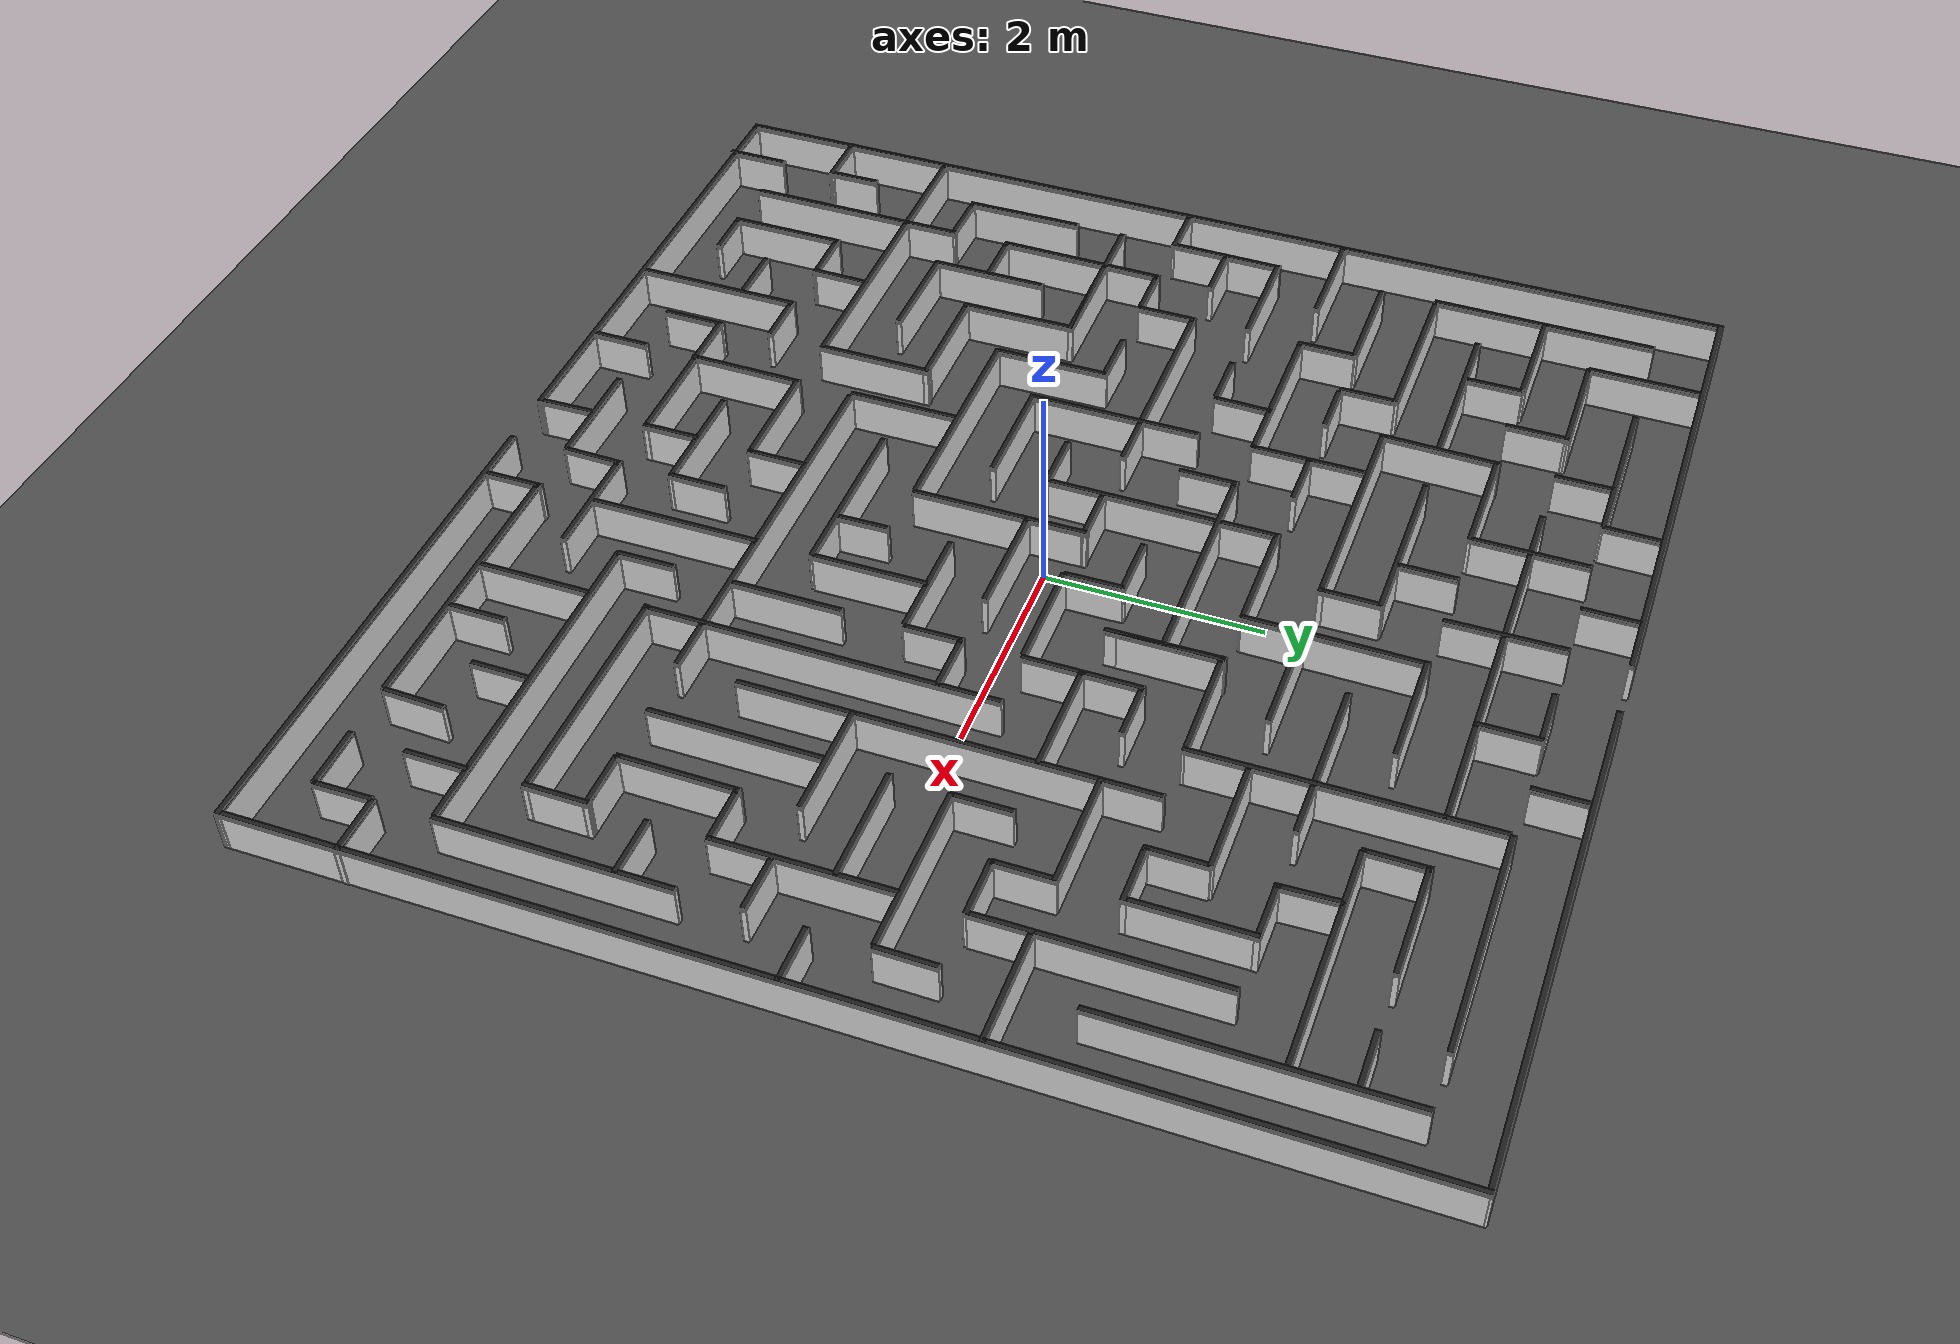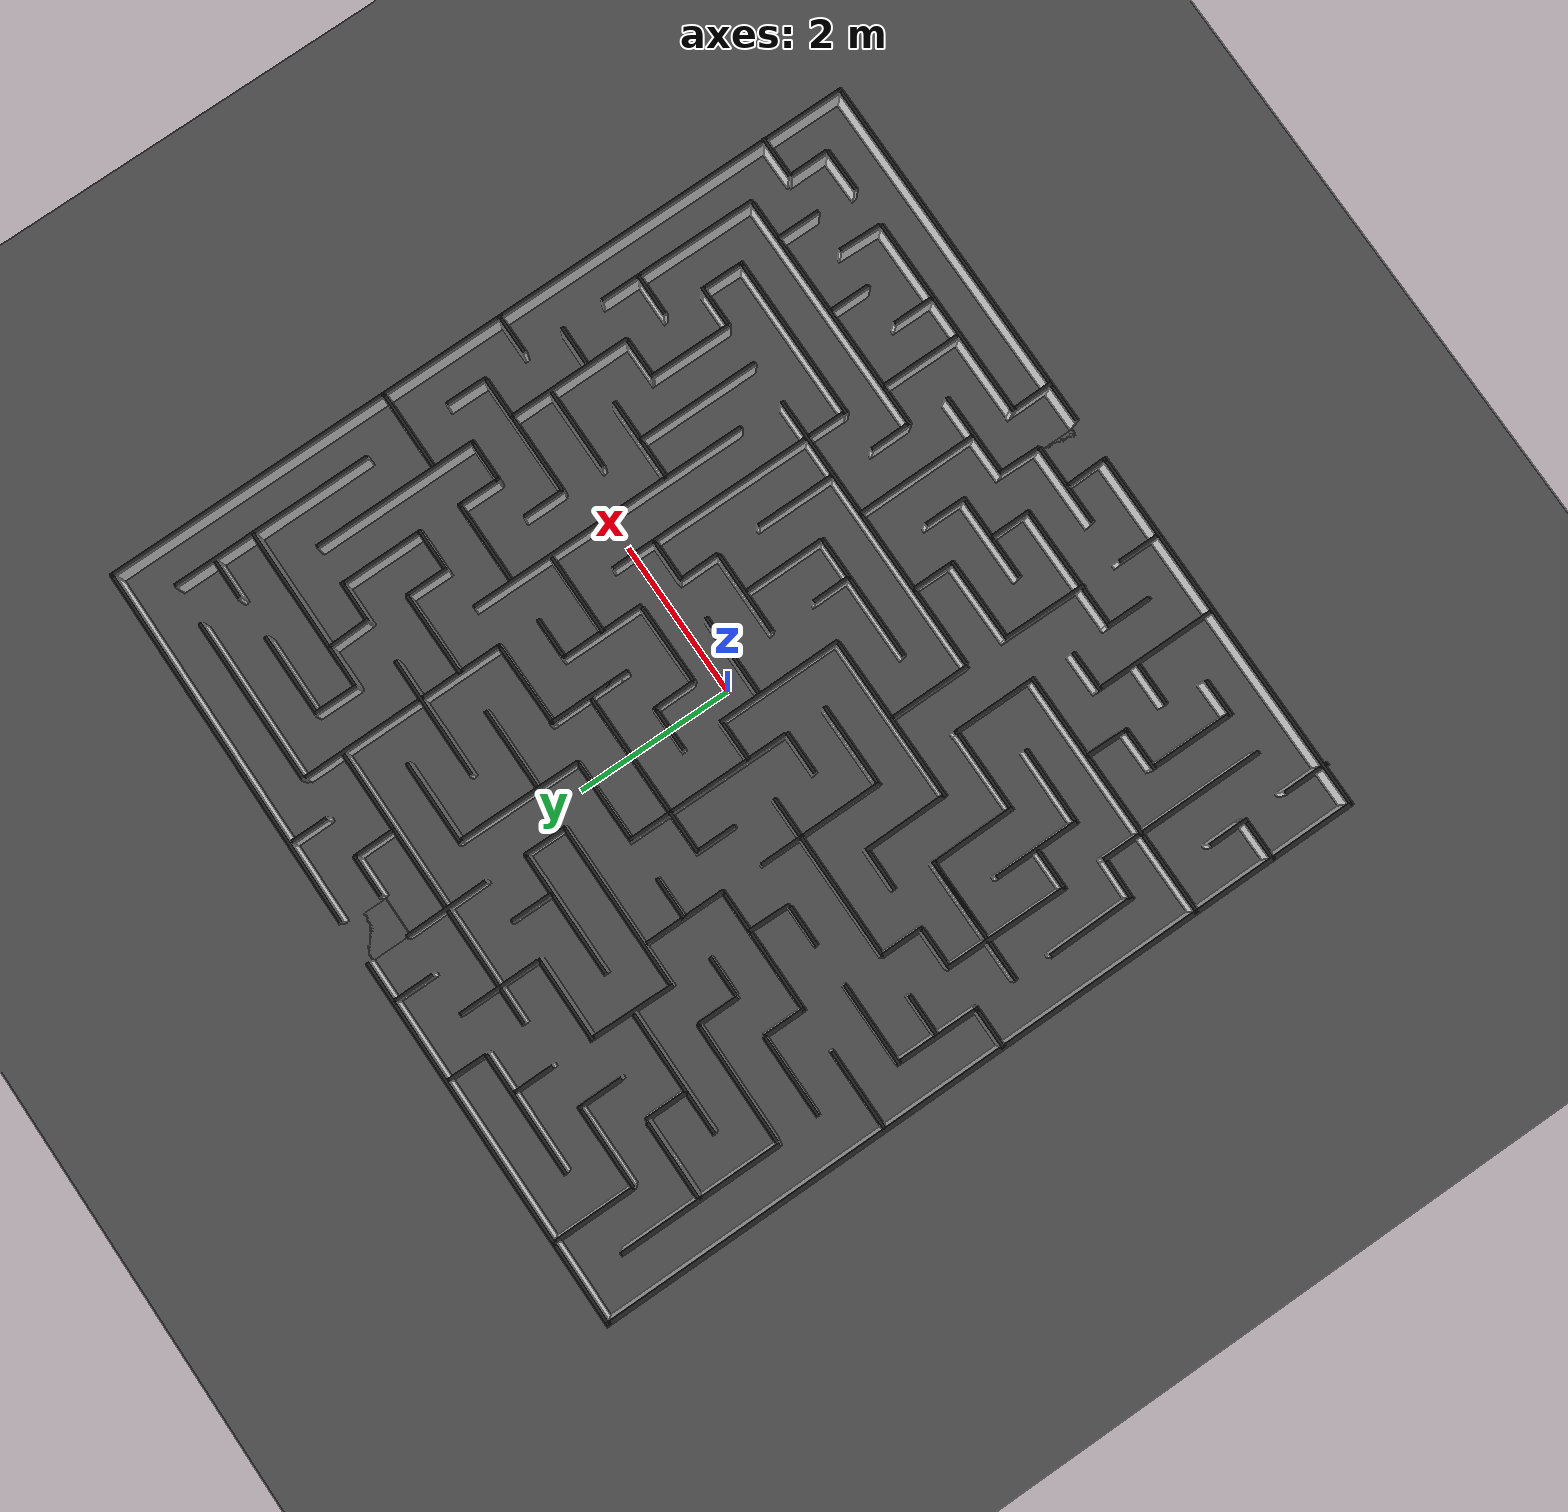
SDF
<sdf version="1.6">
 <world name="default">
  <light name="sun" type="directional">
   <pose>0 0 10 0 -0 0</pose>
   <diffuse>0.8 0.8 0.8 1</diffuse>
   <specular>0.1 0.1 0.1 1</specular>
   <attenuation>
    <range>1000</range>
    <constant>0.9</constant>
    <linear>0.01</linear>
    <quadratic>0.001</quadratic>
   </attenuation>
   <direction>-0.5 0.5 -1</direction>
  </light>
  <model name="ground_plane">
   <static>1</static>
   <link name="link">
    <collision name="collision">
     <geometry><plane><normal>0 0 1</normal><size>100 100</size></plane></geometry>
     <surface><friction><ode><mu>100</mu><mu2>50</mu2></ode></friction></surface>
    </collision>
    <visual name="visual">
     <cast_shadows>0</cast_shadows>
     <geometry><plane><normal>0 0 1</normal><size>100 100</size></plane></geometry>
     <material>
      <script><uri>file://media/materials/scripts/gazebo.material</uri><name>Gazebo/Grey</name></script>
     </material>
    </visual>
   </link>
  </model>
  <gravity>0 0 -9.8</gravity>
  <magnetic_field>6e-06 2.3e-05 -4.2e-05</magnetic_field>
  <atmosphere type="adiabatic"/>
  <physics name="default_physics" default="0" type="ode">
   <max_step_size>0.001</max_step_size>
   <real_time_factor>1</real_time_factor>
   <real_time_update_rate>1000</real_time_update_rate>
  </physics>
  <scene><ambient>0.4 0.4 0.4 1</ambient><background>0.7 0.7 0.7 1</background><shadows>1</shadows></scene>
  <spherical_coordinates>
   <surface_model>EARTH_WGS84</surface_model>
   <latitude_deg>0</latitude_deg>
   <longitude_deg>0</longitude_deg>
   <elevation>0</elevation>
   <heading_deg>0</heading_deg>
  </spherical_coordinates>
  <model name="asphalt_white_plane">
   <static>1</static>
   <link name="link">
    <collision name="collision"><geometry><box><size>60 60 0.005</size></box></geometry></collision>
    <visual name="visual">
     <cast_shadows>0</cast_shadows>
     <geometry><box><size>60 60 0.005</size></box></geometry>
     <material>
      <script>
       <uri>model://asphalt_white_plane/materials/scripts</uri>
       <uri>model://asphalt_white_plane/materials/textures</uri>
       <name>vrc/asphalt_white</name>
      </script>
     </material>
    </visual>
   </link>
  </model>
  <model name="asphalt_red_plane">
   <static>1</static>
   <link name="link">
    <collision name="collision"><geometry><box><size>0.5 0.5 0.005</size></box></geometry></collision>
    <visual name="visual">
     <cast_shadows>0</cast_shadows>
     <geometry><box><size>0.5 0.5 0.005</size></box></geometry>
     <material>
      <script>
       <uri>model://asphalt_red_plane/materials/scripts</uri>
       <uri>model://asphalt_red_plane/materials/textures</uri>
       <name>vrc/asphalt_red</name>
      </script>
     </material>
    </visual>
   </link>
   <pose>0.020723 -4.736055 0 0 -0 0</pose>
  </model>
  <model name="asphalt_green_plane">
   <static>1</static>
   <link name="link">
    <collision name="collision"><geometry><box><size>0.5 0.5 0.005</size></box></geometry></collision>
    <visual name="visual">
     <cast_shadows>0</cast_shadows>
     <geometry><box><size>0.5 0.5 0.005</size></box></geometry>
     <material>
      <script>
       <uri>model://asphalt_green_plane/materials/scripts</uri>
       <uri>model://asphalt_green_plane/materials/textures</uri>
       <name>vrc/asphalt_green</name>
      </script>
     </material>
    </visual>
   </link>
   <pose>0.001361 4.751329 0 0 -0 0</pose>
  </model>
  <model name="ibomaze">
   <link name="Wall_0">
    <collision name="Wall_0_Collision">
     <geometry><box><size>10.031 0.05 0.37</size></box></geometry>
     <pose>0 0 0.185 0 -0 0</pose>
    </collision>
    <visual name="Wall_0_Visual">
     <pose>0 0 0.185 0 -0 0</pose>
     <geometry><box><size>10.031 0.05 0.37</size></box></geometry>
     <material>
      <script><uri>file://media/materials/scripts/gazebo.material</uri><name>Gazebo/White</name></script>
      <ambient>1 1 1 1</ambient>
     </material>
    </visual>
    <pose>-4.98755 0.012016 0 0 -0 1.57082</pose>
   </link>
   <link name="Wall_100">
    <collision name="Wall_100_Collision">
     <geometry><box><size>1.55502 0.05 0.37</size></box></geometry>
     <pose>0 0 0.185 0 -0 0</pose>
    </collision>
    <visual name="Wall_100_Visual">
     <pose>0 0 0.185 0 -0 0</pose>
     <geometry><box><size>1.55502 0.05 0.37</size></box></geometry>
     <material>
      <script><uri>file://media/materials/scripts/gazebo.material</uri><name>Gazebo/White</name></script>
      <ambient>1 1 1 1</ambient>
     </material>
    </visual>
    <pose>0.79411 -3.12637 0 0 0 -1.56548</pose>
   </link>
   <link name="Wall_102">
    <collision name="Wall_102_Collision">
     <geometry><box><size>3.642 0.05 0.37</size></box></geometry>
     <pose>0 0 0.185 0 -0 0</pose>
    </collision>
    <visual name="Wall_102_Visual">
     <pose>0 0 0.185 0 -0 0</pose>
     <geometry><box><size>3.642 0.05 0.37</size></box></geometry>
     <material>
      <script><uri>file://media/materials/scripts/gazebo.material</uri><name>Gazebo/White</name></script>
      <ambient>1 1 1 1</ambient>
     </material>
    </visual>
    <pose>0.535666 -2.35016 0 0 -0 0</pose>
   </link>
   <link name="Wall_104">
    <collision name="Wall_104_Collision">
     <geometry><box><size>0.550695 0.05 0.37</size></box></geometry>
     <pose>0 0 0.185 0 -0 0</pose>
    </collision>
    <visual name="Wall_104_Visual">
     <pose>0 0 0.185 0 -0 0</pose>
     <geometry><box><size>0.550695 0.05 0.37</size></box></geometry>
     <material>
      <script><uri>file://media/materials/scripts/gazebo.material</uri><name>Gazebo/White</name></script>
      <ambient>1 1 1 1</ambient>
     </material>
    </visual>
    <pose>-0.259421 -2.63096 0 0 -0 1.5668</pose>
   </link>
   <link name="Wall_106">
    <collision name="Wall_106_Collision">
     <geometry><box><size>1.08202 0.05 0.37</size></box></geometry>
     <pose>0 0 0.185 0 -0 0</pose>
    </collision>
    <visual name="Wall_106_Visual">
     <pose>0 0 0.185 0 -0 0</pose>
     <geometry><box><size>1.08202 0.05 0.37</size></box></geometry>
     <material>
      <script><uri>file://media/materials/scripts/gazebo.material</uri><name>Gazebo/White</name></script>
      <ambient>1 1 1 1</ambient>
     </material>
    </visual>
    <pose>-0.782298 -2.8899 0 0 -0 0.005814</pose>
   </link>
   <link name="Wall_108">
    <collision name="Wall_108_Collision">
     <geometry><box><size>0.53 0.05 0.37</size></box></geometry>
     <pose>0 0 0.185 0 -0 0</pose>
    </collision>
    <visual name="Wall_108_Visual">
     <pose>0 0 0.185 0 -0 0</pose>
     <geometry><box><size>0.53 0.05 0.37</size></box></geometry>
     <material>
      <script><uri>file://media/materials/scripts/gazebo.material</uri><name>Gazebo/White</name></script>
      <ambient>1 1 1 1</ambient>
     </material>
    </visual>
    <pose>-4.72442 -0.249461 0 0 -0 0</pose>
   </link>
   <link name="Wall_11">
    <collision name="Wall_11_Collision">
     <geometry><box><size>3.19 0.05 0.37</size></box></geometry>
     <pose>0 0 0.185 0 -0 0</pose>
    </collision>
    <visual name="Wall_11_Visual">
     <pose>0 0 0.185 0 -0 0</pose>
     <geometry><box><size>3.19 0.05 0.37</size></box></geometry>
     <material>
      <script><uri>file://media/materials/scripts/gazebo.material</uri><name>Gazebo/White</name></script>
      <ambient>1 1 1 1</ambient>
     </material>
    </visual>
    <pose>-3.41742 -2.86946 0 0 -0 0</pose>
   </link>
   <link name="Wall_110">
    <collision name="Wall_110_Collision">
     <geometry><box><size>1.10019 0.05 0.37</size></box></geometry>
     <pose>0 0 0.185 0 -0 0</pose>
    </collision>
    <visual name="Wall_110_Visual">
     <pose>0 0 0.185 0 -0 0</pose>
     <geometry><box><size>1.10019 0.05 0.37</size></box></geometry>
     <material>
      <script><uri>file://media/materials/scripts/gazebo.material</uri><name>Gazebo/White</name></script>
      <ambient>1 1 1 1</ambient>
     </material>
    </visual>
    <pose>-4.47942 0.275539 0 0 -0 1.56127</pose>
   </link>
   <link name="Wall_112">
    <collision name="Wall_112_Collision">
     <geometry><box><size>0.52 0.05 0.37</size></box></geometry>
     <pose>0 0 0.185 0 -0 0</pose>
    </collision>
    <visual name="Wall_112_Visual">
     <pose>0 0 0.185 0 -0 0</pose>
     <geometry><box><size>0.52 0.05 0.37</size></box></geometry>
     <material>
      <script><uri>file://media/materials/scripts/gazebo.material</uri><name>Gazebo/White</name></script>
      <ambient>1 1 1 1</ambient>
     </material>
    </visual>
    <pose>-4.19942 0.280539 0 0 -0 0</pose>
   </link>
   <link name="Wall_114">
    <collision name="Wall_114_Collision">
     <geometry><box><size>1.06 0.05 0.37</size></box></geometry>
     <pose>0 0 0.185 0 -0 0</pose>
    </collision>
    <visual name="Wall_114_Visual">
     <pose>0 0 0.185 0 -0 0</pose>
     <geometry><box><size>1.06 0.05 0.37</size></box></geometry>
     <material>
      <script><uri>file://media/materials/scripts/gazebo.material</uri><name>Gazebo/White</name></script>
      <ambient>1 1 1 1</ambient>
     </material>
    </visual>
    <pose>-3.96942 0.800539 0 0 -0 0</pose>
   </link>
   <link name="Wall_116">
    <collision name="Wall_116_Collision">
     <geometry><box><size>1.02 0.05 0.37</size></box></geometry>
     <pose>0 0 0.185 0 -0 0</pose>
    </collision>
    <visual name="Wall_116_Visual">
     <pose>0 0 0.185 0 -0 0</pose>
     <geometry><box><size>1.02 0.05 0.37</size></box></geometry>
     <material>
      <script><uri>file://media/materials/scripts/gazebo.material</uri><name>Gazebo/White</name></script>
      <ambient>1 1 1 1</ambient>
     </material>
    </visual>
    <pose>-4.46942 1.33054 0 0 -0 0</pose>
   </link>
   <link name="Wall_118">
    <collision name="Wall_118_Collision">
     <geometry><box><size>0.53023 0.05 0.37</size></box></geometry>
     <pose>0 0 0.185 0 -0 0</pose>
    </collision>
    <visual name="Wall_118_Visual">
     <pose>0 0 0.185 0 -0 0</pose>
     <geometry><box><size>0.53023 0.05 0.37</size></box></geometry>
     <material>
      <script><uri>file://media/materials/scripts/gazebo.material</uri><name>Gazebo/White</name></script>
      <ambient>1 1 1 1</ambient>
     </material>
    </visual>
    <pose>-2.65442 0.810539 0 0 -0 0</pose>
   </link>
   <link name="Wall_120">
    <collision name="Wall_120_Collision">
     <geometry><box><size>0.540102 0.05 0.37</size></box></geometry>
     <pose>0 0 0.185 0 -0 0</pose>
    </collision>
    <visual name="Wall_120_Visual">
     <pose>0 0 0.185 0 -0 0</pose>
     <geometry><box><size>0.540102 0.05 0.37</size></box></geometry>
     <material>
      <script><uri>file://media/materials/scripts/gazebo.material</uri><name>Gazebo/White</name></script>
      <ambient>1 1 1 1</ambient>
     </material>
    </visual>
    <pose>-2.36961 1.07227 0 0 0 -1.5912</pose>
   </link>
   <link name="Wall_122">
    <collision name="Wall_122_Collision">
     <geometry><box><size>1.59805 0.05 0.37</size></box></geometry>
     <pose>0 0 0.185 0 -0 0</pose>
    </collision>
    <visual name="Wall_122_Visual">
     <pose>0 0 0.185 0 -0 0</pose>
     <geometry><box><size>1.59805 0.05 0.37</size></box></geometry>
     <material>
      <script><uri>file://media/materials/scripts/gazebo.material</uri><name>Gazebo/White</name></script>
      <ambient>1 1 1 1</ambient>
     </material>
    </visual>
    <pose>-2.61942 1.33054 0 0 -0 3.14159</pose>
   </link>
   <link name="Wall_124">
    <collision name="Wall_124_Collision">
     <geometry><box><size>0.543 0.05 0.37</size></box></geometry>
     <pose>0 0 0.185 0 -0 0</pose>
    </collision>
    <visual name="Wall_124_Visual">
     <pose>0 0 0.185 0 -0 0</pose>
     <geometry><box><size>0.543 0.05 0.37</size></box></geometry>
     <material>
      <script><uri>file://media/materials/scripts/gazebo.material</uri><name>Gazebo/White</name></script>
      <ambient>1 1 1 1</ambient>
     </material>
    </visual>
    <pose>-3.40927 1.58031 0 0 0 -1.5708</pose>
   </link>
   <link name="Wall_126">
    <collision name="Wall_126_Collision">
     <geometry><box><size>1.043 0.05 0.37</size></box></geometry>
     <pose>0 0 0.185 0 -0 0</pose>
    </collision>
    <visual name="Wall_126_Visual">
     <pose>0 0 0.185 0 -0 0</pose>
     <geometry><box><size>1.043 0.05 0.37</size></box></geometry>
     <material>
      <script><uri>file://media/materials/scripts/gazebo.material</uri><name>Gazebo/White</name></script>
      <ambient>1 1 1 1</ambient>
     </material>
    </visual>
    <pose>-3.92799 1.85254 0 0 -0 0</pose>
   </link>
   <link name="Wall_128">
    <collision name="Wall_128_Collision">
     <geometry><box><size>0.51 0.05 0.37</size></box></geometry>
     <pose>0 0 0.185 0 -0 0</pose>
    </collision>
    <visual name="Wall_128_Visual">
     <pose>0 0 0.185 0 -0 0</pose>
     <geometry><box><size>0.51 0.05 0.37</size></box></geometry>
     <material>
      <script><uri>file://media/materials/scripts/gazebo.material</uri><name>Gazebo/White</name></script>
      <ambient>1 1 1 1</ambient>
     </material>
    </visual>
    <pose>-2.60561 1.85419 0 0 -0 3.14159</pose>
   </link>
   <link name="Wall_13">
    <collision name="Wall_13_Collision">
     <geometry><box><size>1.1 0.05 0.37</size></box></geometry>
     <pose>0 0 0.185 0 -0 0</pose>
    </collision>
    <visual name="Wall_13_Visual">
     <pose>0 0 0.185 0 -0 0</pose>
     <geometry><box><size>1.1 0.05 0.37</size></box></geometry>
     <material>
      <script><uri>file://media/materials/scripts/gazebo.material</uri><name>Gazebo/White</name></script>
      <ambient>1 1 1 1</ambient>
     </material>
    </visual>
    <pose>-1.84742 -2.34446 0 0 -0 1.5708</pose>
   </link>
   <link name="Wall_130">
    <collision name="Wall_130_Collision">
     <geometry><box><size>0.521 0.05 0.37</size></box></geometry>
     <pose>0 0 0.185 0 -0 0</pose>
    </collision>
    <visual name="Wall_130_Visual">
     <pose>0 0 0.185 0 -0 0</pose>
     <geometry><box><size>0.521 0.05 0.37</size></box></geometry>
     <material>
      <script><uri>file://media/materials/scripts/gazebo.material</uri><name>Gazebo/White</name></script>
      <ambient>1 1 1 1</ambient>
     </material>
    </visual>
    <pose>-2.88742 2.10975 0 0 0 -1.5708</pose>
   </link>
   <link name="Wall_132">
    <collision name="Wall_132_Collision">
     <geometry><box><size>1.55502 0.05 0.37</size></box></geometry>
     <pose>0 0 0.185 0 -0 0</pose>
    </collision>
    <visual name="Wall_132_Visual">
     <pose>0 0 0.185 0 -0 0</pose>
     <geometry><box><size>1.55502 0.05 0.37</size></box></geometry>
     <material>
      <script><uri>file://media/materials/scripts/gazebo.material</uri><name>Gazebo/White</name></script>
      <ambient>1 1 1 1</ambient>
     </material>
    </visual>
    <pose>-3.65246 2.38026 0 0 0 -0.005316</pose>
   </link>
   <link name="Wall_134">
    <collision name="Wall_134_Collision">
     <geometry><box><size>2.10101 0.05 0.37</size></box></geometry>
     <pose>0 0 0.185 0 -0 0</pose>
    </collision>
    <visual name="Wall_134_Visual">
     <pose>0 0 0.185 0 -0 0</pose>
     <geometry><box><size>2.10101 0.05 0.37</size></box></geometry>
     <material>
      <script><uri>file://media/materials/scripts/gazebo.material</uri><name>Gazebo/White</name></script>
      <ambient>1 1 1 1</ambient>
     </material>
    </visual>
    <pose>-4.45884 3.41859 0 0 0 -1.57372</pose>
   </link>
   <link name="Wall_136">
    <collision name="Wall_136_Collision">
     <geometry><box><size>1.01776 0.05 0.37</size></box></geometry>
     <pose>0 0 0.185 0 -0 0</pose>
    </collision>
    <visual name="Wall_136_Visual">
     <pose>0 0 0.185 0 -0 0</pose>
     <geometry><box><size>1.01776 0.05 0.37</size></box></geometry>
     <material>
      <script><uri>file://media/materials/scripts/gazebo.material</uri><name>Gazebo/White</name></script>
      <ambient>1 1 1 1</ambient>
     </material>
    </visual>
    <pose>-3.95442 3.43554 0 0 -0 0</pose>
   </link>
   <link name="Wall_138">
    <collision name="Wall_138_Collision">
     <geometry><box><size>0.534 0.05 0.37</size></box></geometry>
     <pose>0 0 0.185 0 -0 0</pose>
    </collision>
    <visual name="Wall_138_Visual">
     <pose>0 0 0.185 0 -0 0</pose>
     <geometry><box><size>0.534 0.05 0.37</size></box></geometry>
     <material>
      <script><uri>file://media/materials/scripts/gazebo.material</uri><name>Gazebo/White</name></script>
      <ambient>1 1 1 1</ambient>
     </material>
    </visual>
    <pose>-3.41798 3.17122 0 0 -0 1.5708</pose>
   </link>
   <link name="Wall_140">
    <collision name="Wall_140_Collision">
     <geometry><box><size>1.58536 0.05 0.37</size></box></geometry>
     <pose>0 0 0.185 0 -0 0</pose>
    </collision>
    <visual name="Wall_140_Visual">
     <pose>0 0 0.185 0 -0 0</pose>
     <geometry><box><size>1.58536 0.05 0.37</size></box></geometry>
     <material>
      <script><uri>file://media/materials/scripts/gazebo.material</uri><name>Gazebo/White</name></script>
      <ambient>1 1 1 1</ambient>
     </material>
    </visual>
    <pose>-3.17992 2.89854 0 0 -0 0</pose>
   </link>
   <link name="Wall_142">
    <collision name="Wall_142_Collision">
     <geometry><box><size>1.10734 0.05 0.37</size></box></geometry>
     <pose>0 0 0.185 0 -0 0</pose>
    </collision>
    <visual name="Wall_142_Visual">
     <pose>0 0 0.185 0 -0 0</pose>
     <geometry><box><size>1.10734 0.05 0.37</size></box></geometry>
     <material>
      <script><uri>file://media/materials/scripts/gazebo.material</uri><name>Gazebo/White</name></script>
      <ambient>1 1 1 1</ambient>
     </material>
    </visual>
    <pose>-2.36302 2.90878 0 0 0 -1.59184</pose>
   </link>
   <link name="Wall_144">
    <collision name="Wall_144_Collision">
     <geometry><box><size>2.15608 0.05 0.37</size></box></geometry>
     <pose>0 0 0.185 0 -0 0</pose>
    </collision>
    <visual name="Wall_144_Visual">
     <pose>0 0 0.185 0 -0 0</pose>
     <geometry><box><size>2.15608 0.05 0.37</size></box></geometry>
     <material>
      <script><uri>file://media/materials/scripts/gazebo.material</uri><name>Gazebo/White</name></script>
      <ambient>1 1 1 1</ambient>
     </material>
    </visual>
    <pose>-1.31538 2.38538 0 0 0 -0.000543</pose>
   </link>
   <link name="Wall_146">
    <collision name="Wall_146_Collision">
     <geometry><box><size>1.037 0.05 0.37</size></box></geometry>
     <pose>0 0 0.185 0 -0 0</pose>
    </collision>
    <visual name="Wall_146_Visual">
     <pose>0 0 0.185 0 -0 0</pose>
     <geometry><box><size>1.037 0.05 0.37</size></box></geometry>
     <material>
      <script><uri>file://media/materials/scripts/gazebo.material</uri><name>Gazebo/White</name></script>
      <ambient>1 1 1 1</ambient>
     </material>
    </visual>
    <pose>-1.83642 1.83616 0 0 0 -1.5708</pose>
   </link>
   <link name="Wall_148">
    <collision name="Wall_148_Collision">
     <geometry><box><size>0.529886 0.05 0.37</size></box></geometry>
     <pose>0 0 0.185 0 -0 0</pose>
    </collision>
    <visual name="Wall_148_Visual">
     <pose>0 0 0.185 0 -0 0</pose>
     <geometry><box><size>0.529886 0.05 0.37</size></box></geometry>
     <material>
      <script><uri>file://media/materials/scripts/gazebo.material</uri><name>Gazebo/White</name></script>
      <ambient>1 1 1 1</ambient>
     </material>
    </visual>
    <pose>-1.56342 1.84954 0 0 -0 3.14159</pose>
   </link>
   <link name="Wall_15">
    <collision name="Wall_15_Collision">
     <geometry><box><size>1.10019 0.05 0.37</size></box></geometry>
     <pose>0 0 0.185 0 -0 0</pose>
    </collision>
    <visual name="Wall_15_Visual">
     <pose>0 0 0.185 0 -0 0</pose>
     <geometry><box><size>1.10019 0.05 0.37</size></box></geometry>
     <material>
      <script><uri>file://media/materials/scripts/gazebo.material</uri><name>Gazebo/White</name></script>
      <ambient>1 1 1 1</ambient>
     </material>
    </visual>
    <pose>-2.37242 -1.82946 0 0 -0 3.14159</pose>
   </link>
   <link name="Wall_152">
    <collision name="Wall_152_Collision">
     <geometry><box><size>4.75301 0.05 0.37</size></box></geometry>
     <pose>0 0 0.185 0 -0 0</pose>
    </collision>
    <visual name="Wall_152_Visual">
     <pose>0 0 0.185 0 -0 0</pose>
     <geometry><box><size>4.75301 0.05 0.37</size></box></geometry>
     <material>
      <script><uri>file://media/materials/scripts/gazebo.material</uri><name>Gazebo/White</name></script>
      <ambient>1 1 1 1</ambient>
     </material>
    </visual>
    <pose>-2.63618 5.00649 0 0 -0 0.001701</pose>
   </link>
   <link name="Wall_154">
    <collision name="Wall_154_Collision">
     <geometry><box><size>1.06401 0.05 0.37</size></box></geometry>
     <pose>0 0 0.185 0 -0 0</pose>
    </collision>
    <visual name="Wall_154_Visual">
     <pose>0 0 0.185 0 -0 0</pose>
     <geometry><box><size>1.06401 0.05 0.37</size></box></geometry>
     <material>
      <script><uri>file://media/materials/scripts/gazebo.material</uri><name>Gazebo/White</name></script>
      <ambient>1 1 1 1</ambient>
     </material>
    </visual>
    <pose>-3.94298 4.48062 0 0 0 -1.57573</pose>
   </link>
   <link name="Wall_156">
    <collision name="Wall_156_Collision">
     <geometry><box><size>1.07401 0.05 0.37</size></box></geometry>
     <pose>0 0 0.185 0 -0 0</pose>
    </collision>
    <visual name="Wall_156_Visual">
     <pose>0 0 0.185 0 -0 0</pose>
     <geometry><box><size>1.07401 0.05 0.37</size></box></geometry>
     <material>
      <script><uri>file://media/materials/scripts/gazebo.material</uri><name>Gazebo/White</name></script>
      <ambient>1 1 1 1</ambient>
     </material>
    </visual>
    <pose>-3.40842 3.95604 0 0 0 -3.13671</pose>
   </link>
   <link name="Wall_158">
    <collision name="Wall_158_Collision">
     <geometry><box><size>0.587 0.05 0.37</size></box></geometry>
     <pose>0 0 0.185 0 -0 0</pose>
    </collision>
    <visual name="Wall_158_Visual">
     <pose>0 0 0.185 0 -0 0</pose>
     <geometry><box><size>0.587 0.05 0.37</size></box></geometry>
     <material>
      <script><uri>file://media/materials/scripts/gazebo.material</uri><name>Gazebo/White</name></script>
      <ambient>1 1 1 1</ambient>
     </material>
    </visual>
    <pose>-2.89642 3.69004 0 0 -0 1.5708</pose>
   </link>
   <link name="Wall_160">
    <collision name="Wall_160_Collision">
     <geometry><box><size>0.507585 0.05 0.37</size></box></geometry>
     <pose>0 0 0.185 0 -0 0</pose>
    </collision>
    <visual name="Wall_160_Visual">
     <pose>0 0 0.185 0 -0 0</pose>
     <geometry><box><size>0.507585 0.05 0.37</size></box></geometry>
     <material>
      <script><uri>file://media/materials/scripts/gazebo.material</uri><name>Gazebo/White</name></script>
      <ambient>1 1 1 1</ambient>
     </material>
    </visual>
    <pose>-1.83992 4.73054 0 0 -0 1.55988</pose>
   </link>
   <link name="Wall_162">
    <collision name="Wall_162_Collision">
     <geometry><box><size>1.572 0.05 0.37</size></box></geometry>
     <pose>0 0 0.185 0 -0 0</pose>
    </collision>
    <visual name="Wall_162_Visual">
     <pose>0 0 0.185 0 -0 0</pose>
     <geometry><box><size>1.572 0.05 0.37</size></box></geometry>
     <material>
      <script><uri>file://media/materials/scripts/gazebo.material</uri><name>Gazebo/White</name></script>
      <ambient>1 1 1 1</ambient>
     </material>
    </visual>
    <pose>-2.62248 4.48151 0 0 -0 0</pose>
   </link>
   <link name="Wall_164">
    <collision name="Wall_164_Collision">
     <geometry><box><size>0.523 0.05 0.37</size></box></geometry>
     <pose>0 0 0.185 0 -0 0</pose>
    </collision>
    <visual name="Wall_164_Visual">
     <pose>0 0 0.185 0 -0 0</pose>
     <geometry><box><size>0.523 0.05 0.37</size></box></geometry>
     <material>
      <script><uri>file://media/materials/scripts/gazebo.material</uri><name>Gazebo/White</name></script>
      <ambient>1 1 1 1</ambient>
     </material>
    </visual>
    <pose>-2.35942 4.21098 0 0 -0 1.5708</pose>
   </link>
   <link name="Wall_166">
    <collision name="Wall_166_Collision">
     <geometry><box><size>0.507292 0.05 0.37</size></box></geometry>
     <pose>0 0 0.185 0 -0 0</pose>
    </collision>
    <visual name="Wall_166_Visual">
     <pose>0 0 0.185 0 -0 0</pose>
     <geometry><box><size>0.507292 0.05 0.37</size></box></geometry>
     <material>
      <script><uri>file://media/materials/scripts/gazebo.material</uri><name>Gazebo/White</name></script>
      <ambient>1 1 1 1</ambient>
     </material>
    </visual>
    <pose>-0.784421 4.73804 0 0 -0 1.5708</pose>
   </link>
   <link name="Wall_168">
    <collision name="Wall_168_Collision">
     <geometry><box><size>0.473 0.05 0.37</size></box></geometry>
     <pose>0 0 0.185 0 -0 0</pose>
    </collision>
    <visual name="Wall_168_Visual">
     <pose>0 0 0.185 0 -0 0</pose>
     <geometry><box><size>0.473 0.05 0.37</size></box></geometry>
     <material>
      <script><uri>file://media/materials/scripts/gazebo.material</uri><name>Gazebo/White</name></script>
      <ambient>1 1 1 1</ambient>
     </material>
    </visual>
    <pose>1.31958 4.73595 0 0 -0 1.5708</pose>
   </link>
   <link name="Wall_17">
    <collision name="Wall_17_Collision">
     <geometry><box><size>1.05005 0.05 0.37</size></box></geometry>
     <pose>0 0 0.185 0 -0 0</pose>
    </collision>
    <visual name="Wall_17_Visual">
     <pose>0 0 0.185 0 -0 0</pose>
     <geometry><box><size>1.05005 0.05 0.37</size></box></geometry>
     <material>
      <script><uri>file://media/materials/scripts/gazebo.material</uri><name>Gazebo/White</name></script>
      <ambient>1 1 1 1</ambient>
     </material>
    </visual>
    <pose>-2.90242 -1.32946 0 0 -0 1.5808</pose>
   </link>
   <link name="Wall_172">
    <collision name="Wall_172_Collision">
     <geometry><box><size>2.60602 0.05 0.37</size></box></geometry>
     <pose>0 0 0.185 0 -0 0</pose>
    </collision>
    <visual name="Wall_172_Visual">
     <pose>0 0 0.185 0 -0 0</pose>
     <geometry><box><size>2.60602 0.05 0.37</size></box></geometry>
     <material>
      <script><uri>file://media/materials/scripts/gazebo.material</uri><name>Gazebo/White</name></script>
      <ambient>1 1 1 1</ambient>
     </material>
    </visual>
    <pose>4.47494 3.17542 0 0 0 -1.56727</pose>
   </link>
   <link name="Wall_174">
    <collision name="Wall_174_Collision">
     <geometry><box><size>0.521111 0.05 0.37</size></box></geometry>
     <pose>0 0 0.185 0 -0 0</pose>
    </collision>
    <visual name="Wall_174_Visual">
     <pose>0 0 0.185 0 -0 0</pose>
     <geometry><box><size>0.521111 0.05 0.37</size></box></geometry>
     <material>
      <script><uri>file://media/materials/scripts/gazebo.material</uri><name>Gazebo/White</name></script>
      <ambient>1 1 1 1</ambient>
     </material>
    </visual>
    <pose>4.19708 3.95054 0 0 -0 0</pose>
   </link>
   <link name="Wall_176">
    <collision name="Wall_176_Collision">
     <geometry><box><size>1.053 0.05 0.37</size></box></geometry>
     <pose>0 0 0.185 0 -0 0</pose>
    </collision>
    <visual name="Wall_176_Visual">
     <pose>0 0 0.185 0 -0 0</pose>
     <geometry><box><size>1.053 0.05 0.37</size></box></geometry>
     <material>
      <script><uri>file://media/materials/scripts/gazebo.material</uri><name>Gazebo/White</name></script>
      <ambient>1 1 1 1</ambient>
     </material>
    </visual>
    <pose>2.89012 3.95254 0 0 -0 3.14159</pose>
   </link>
   <link name="Wall_178">
    <collision name="Wall_178_Collision">
     <geometry><box><size>0.563928 0.05 0.37</size></box></geometry>
     <pose>0 0 0.185 0 -0 0</pose>
    </collision>
    <visual name="Wall_178_Visual">
     <pose>0 0 0.185 0 -0 0</pose>
     <geometry><box><size>0.563928 0.05 0.37</size></box></geometry>
     <material>
      <script><uri>file://media/materials/scripts/gazebo.material</uri><name>Gazebo/White</name></script>
      <ambient>1 1 1 1</ambient>
     </material>
    </visual>
    <pose>2.37095 3.69582 0 0 -0 1.56698</pose>
   </link>
   <link name="Wall_180">
    <collision name="Wall_180_Collision">
     <geometry><box><size>2.105 0.05 0.37</size></box></geometry>
     <pose>0 0 0.185 0 -0 0</pose>
    </collision>
    <visual name="Wall_180_Visual">
     <pose>0 0 0.185 0 -0 0</pose>
     <geometry><box><size>2.105 0.05 0.37</size></box></geometry>
     <material>
      <script><uri>file://media/materials/scripts/gazebo.material</uri><name>Gazebo/White</name></script>
      <ambient>1 1 1 1</ambient>
     </material>
    </visual>
    <pose>3.42395 3.42878 0 0 -0 3.14159</pose>
   </link>
   <link name="Wall_19">
    <collision name="Wall_19_Collision">
     <geometry><box><size>1.59158 0.05 0.37</size></box></geometry>
     <pose>0 0 0.185 0 -0 0</pose>
    </collision>
    <visual name="Wall_19_Visual">
     <pose>0 0 0.185 0 -0 0</pose>
     <geometry><box><size>1.59158 0.05 0.37</size></box></geometry>
     <material>
      <script><uri>file://media/materials/scripts/gazebo.material</uri><name>Gazebo/White</name></script>
      <ambient>1 1 1 1</ambient>
     </material>
    </visual>
    <pose>-3.67821 -0.782304 0 0 -0 0.003688</pose>
   </link>
   <link name="Wall_21">
    <collision name="Wall_21_Collision">
     <geometry><box><size>1.60249 0.05 0.37</size></box></geometry>
     <pose>0 0 0.185 0 -0 0</pose>
    </collision>
    <visual name="Wall_21_Visual">
     <pose>0 0 0.185 0 -0 0</pose>
     <geometry><box><size>1.60249 0.05 0.37</size></box></geometry>
     <material>
      <script><uri>file://media/materials/scripts/gazebo.material</uri><name>Gazebo/White</name></script>
      <ambient>1 1 1 1</ambient>
     </material>
    </visual>
    <pose>-3.94001 -1.03323 0 0 0 -1.58035</pose>
   </link>
   <link name="Wall_23">
    <collision name="Wall_23_Collision">
     <geometry><box><size>0.539891 0.05 0.37</size></box></geometry>
     <pose>0 0 0.185 0 -0 0</pose>
    </collision>
    <visual name="Wall_23_Visual">
     <pose>0 0 0.185 0 -0 0</pose>
     <geometry><box><size>0.539891 0.05 0.37</size></box></geometry>
     <material>
      <script><uri>file://media/materials/scripts/gazebo.material</uri><name>Gazebo/White</name></script>
      <ambient>1 1 1 1</ambient>
     </material>
    </visual>
    <pose>-3.70242 -1.80946 0 0 -0 0</pose>
   </link>
   <link name="Wall_25">
    <collision name="Wall_25_Collision">
     <geometry><box><size>1.11 0.05 0.37</size></box></geometry>
     <pose>0 0 0.185 0 -0 0</pose>
    </collision>
    <visual name="Wall_25_Visual">
     <pose>0 0 0.185 0 -0 0</pose>
     <geometry><box><size>1.11 0.05 0.37</size></box></geometry>
     <material>
      <script><uri>file://media/materials/scripts/gazebo.material</uri><name>Gazebo/White</name></script>
      <ambient>1 1 1 1</ambient>
     </material>
    </visual>
    <pose>-3.42742 -1.80946 0 0 0 -1.5708</pose>
   </link>
   <link name="Wall_27">
    <collision name="Wall_27_Collision">
     <geometry><box><size>1.01005 0.05 0.37</size></box></geometry>
     <pose>0 0 0.185 0 -0 0</pose>
    </collision>
    <visual name="Wall_27_Visual">
     <pose>0 0 0.185 0 -0 0</pose>
     <geometry><box><size>1.01005 0.05 0.37</size></box></geometry>
     <material>
      <script><uri>file://media/materials/scripts/gazebo.material</uri><name>Gazebo/White</name></script>
      <ambient>1 1 1 1</ambient>
     </material>
    </visual>
    <pose>-2.94742 -2.34446 0 0 -0 3.13118</pose>
   </link>
   <link name="Wall_29">
    <collision name="Wall_29_Collision">
     <geometry><box><size>2.13141 0.05 0.37</size></box></geometry>
     <pose>0 0 0.185 0 -0 0</pose>
    </collision>
    <visual name="Wall_29_Visual">
     <pose>0 0 0.185 0 -0 0</pose>
     <geometry><box><size>2.13141 0.05 0.37</size></box></geometry>
     <material>
      <script><uri>file://media/materials/scripts/gazebo.material</uri><name>Gazebo/White</name></script>
      <ambient>1 1 1 1</ambient>
     </material>
    </visual>
    <pose>-3.93842 -3.41196 0 0 -0 1.5708</pose>
   </link>
   <link name="Wall_3">
    <collision name="Wall_3_Collision">
     <geometry><box><size>4.7759 0.05 0.37</size></box></geometry>
     <pose>0 0 0.185 0 -0 0</pose>
    </collision>
    <visual name="Wall_3_Visual">
     <pose>0 0 0.185 0 -0 0</pose>
     <geometry><box><size>4.7759 0.05 0.37</size></box></geometry>
     <material>
      <script><uri>file://media/materials/scripts/gazebo.material</uri><name>Gazebo/White</name></script>
      <ambient>1 1 1 1</ambient>
     </material>
    </visual>
    <pose>-2.62448 -4.98295 0 0 0 -0.001898</pose>
   </link>
   <link name="Wall_31">
    <collision name="Wall_31_Collision">
     <geometry><box><size>0.568139 0.05 0.37</size></box></geometry>
     <pose>0 0 0.185 0 -0 0</pose>
    </collision>
    <visual name="Wall_31_Visual">
     <pose>0 0 0.185 0 -0 0</pose>
     <geometry><box><size>0.568139 0.05 0.37</size></box></geometry>
     <material>
      <script><uri>file://media/materials/scripts/gazebo.material</uri><name>Gazebo/White</name></script>
      <ambient>1 1 1 1</ambient>
     </material>
    </visual>
    <pose>-4.19742 -2.36546 0 0 0 -0.023162</pose>
   </link>
   <link name="Wall_33">
    <collision name="Wall_33_Collision">
     <geometry><box><size>1.13106 0.05 0.37</size></box></geometry>
     <pose>0 0 0.185 0 -0 0</pose>
    </collision>
    <visual name="Wall_33_Visual">
     <pose>0 0 0.185 0 -0 0</pose>
     <geometry><box><size>1.13106 0.05 0.37</size></box></geometry>
     <material>
      <script><uri>file://media/materials/scripts/gazebo.material</uri><name>Gazebo/White</name></script>
      <ambient>1 1 1 1</ambient>
     </material>
    </visual>
    <pose>-4.46192 -1.81896 0 0 0 -1.56062</pose>
   </link>
   <link name="Wall_35">
    <collision name="Wall_35_Collision">
     <geometry><box><size>0.566 0.05 0.37</size></box></geometry>
     <pose>0 0 0.185 0 -0 0</pose>
    </collision>
    <visual name="Wall_35_Visual">
     <pose>0 0 0.185 0 -0 0</pose>
     <geometry><box><size>0.566 0.05 0.37</size></box></geometry>
     <material>
      <script><uri>file://media/materials/scripts/gazebo.material</uri><name>Gazebo/White</name></script>
      <ambient>1 1 1 1</ambient>
     </material>
    </visual>
    <pose>-4.73242 -3.90446 0 0 -0 0</pose>
   </link>
   <link name="Wall_36">
    <collision name="Wall_36_Collision">
     <geometry><box><size>0.51201 0.05 0.37</size></box></geometry>
     <pose>0 0 0.185 0 -0 0</pose>
    </collision>
    <visual name="Wall_36_Visual">
     <pose>0 0 0.185 0 -0 0</pose>
     <geometry><box><size>0.51201 0.05 0.37</size></box></geometry>
     <material>
      <script><uri>file://media/materials/scripts/gazebo.material</uri><name>Gazebo/White</name></script>
      <ambient>1 1 1 1</ambient>
     </material>
    </visual>
    <pose>-4.47592 -3.67346 0 0 -0 1.57729</pose>
   </link>
   <link name="Wall_38">
    <collision name="Wall_38_Collision">
     <geometry><box><size>0.590149 0.05 0.37</size></box></geometry>
     <pose>0 0 0.185 0 -0 0</pose>
    </collision>
    <visual name="Wall_38_Visual">
     <pose>0 0 0.185 0 -0 0</pose>
     <geometry><box><size>0.590149 0.05 0.37</size></box></geometry>
     <material>
      <script><uri>file://media/materials/scripts/gazebo.material</uri><name>Gazebo/White</name></script>
      <ambient>1 1 1 1</ambient>
     </material>
    </visual>
    <pose>-4.47542 -4.74046 0 0 -0 1.5708</pose>
   </link>
   <link name="Wall_40">
    <collision name="Wall_40_Collision">
     <geometry><box><size>0.57988 0.05 0.37</size></box></geometry>
     <pose>0 0 0.185 0 -0 0</pose>
    </collision>
    <visual name="Wall_40_Visual">
     <pose>0 0 0.185 0 -0 0</pose>
     <geometry><box><size>0.57988 0.05 0.37</size></box></geometry>
     <material>
      <script><uri>file://media/materials/scripts/gazebo.material</uri><name>Gazebo/White</name></script>
      <ambient>1 1 1 1</ambient>
     </material>
    </visual>
    <pose>-2.90042 -3.13535 0 0 0 -1.58967</pose>
   </link>
   <link name="Wall_41">
    <collision name="Wall_41_Collision">
     <geometry><box><size>0.559916 0.05 0.37</size></box></geometry>
     <pose>0 0 0.185 0 -0 0</pose>
    </collision>
    <visual name="Wall_41_Visual">
     <pose>0 0 0.185 0 -0 0</pose>
     <geometry><box><size>0.559916 0.05 0.37</size></box></geometry>
     <material>
      <script><uri>file://media/materials/scripts/gazebo.material</uri><name>Gazebo/White</name></script>
      <ambient>1 1 1 1</ambient>
     </material>
    </visual>
    <pose>-3.16037 -3.40096 0 0 0 -3.13325</pose>
   </link>
   <link name="Wall_42">
    <collision name="Wall_42_Collision">
     <geometry><box><size>1.10884 0.05 0.37</size></box></geometry>
     <pose>0 0 0.185 0 -0 0</pose>
    </collision>
    <visual name="Wall_42_Visual">
     <pose>0 0 0.185 0 -0 0</pose>
     <geometry><box><size>1.10884 0.05 0.37</size></box></geometry>
     <material>
      <script><uri>file://media/materials/scripts/gazebo.material</uri><name>Gazebo/White</name></script>
      <ambient>1 1 1 1</ambient>
     </material>
    </visual>
    <pose>-3.41532 -3.93251 0 0 0 -1.5708</pose>
   </link>
   <link name="Wall_43">
    <collision name="Wall_43_Collision">
     <geometry><box><size>0.489908 0.05 0.37</size></box></geometry>
     <pose>0 0 0.185 0 -0 0</pose>
    </collision>
    <visual name="Wall_43_Visual">
     <pose>0 0 0.185 0 -0 0</pose>
     <geometry><box><size>0.489908 0.05 0.37</size></box></geometry>
     <material>
      <script><uri>file://media/materials/scripts/gazebo.material</uri><name>Gazebo/White</name></script>
      <ambient>1 1 1 1</ambient>
     </material>
    </visual>
    <pose>-3.19537 -4.46213 0 0 -0 0.006462</pose>
   </link>
   <link name="Wall_45">
    <collision name="Wall_45_Collision">
     <geometry><box><size>1.61397 0.05 0.37</size></box></geometry>
     <pose>0 0 0.185 0 -0 0</pose>
    </collision>
    <visual name="Wall_45_Visual">
     <pose>0 0 0.185 0 -0 0</pose>
     <geometry><box><size>1.61397 0.05 0.37</size></box></geometry>
     <material>
      <script><uri>file://media/materials/scripts/gazebo.material</uri><name>Gazebo/White</name></script>
      <ambient>1 1 1 1</ambient>
     </material>
    </visual>
    <pose>-2.35764 -4.20046 0 0 0 -1.57108</pose>
   </link>
   <link name="Wall_47">
    <collision name="Wall_47_Collision">
     <geometry><box><size>0.557164 0.05 0.37</size></box></geometry>
     <pose>0 0 0.185 0 -0 0</pose>
    </collision>
    <visual name="Wall_47_Visual">
     <pose>0 0 0.185 0 -0 0</pose>
     <geometry><box><size>0.557164 0.05 0.37</size></box></geometry>
     <material>
      <script><uri>file://media/materials/scripts/gazebo.material</uri><name>Gazebo/White</name></script>
      <ambient>1 1 1 1</ambient>
     </material>
    </visual>
    <pose>-2.64692 -3.93596 0 0 0 -0.005917</pose>
   </link>
   <link name="Wall_49">
    <collision name="Wall_49_Collision">
     <geometry><box><size>0.529198 0.05 0.37</size></box></geometry>
     <pose>0 0 0.185 0 -0 0</pose>
    </collision>
    <visual name="Wall_49_Visual">
     <pose>0 0 0.185 0 -0 0</pose>
     <geometry><box><size>0.529198 0.05 0.37</size></box></geometry>
     <material>
      <script><uri>file://media/materials/scripts/gazebo.material</uri><name>Gazebo/White</name></script>
      <ambient>1 1 1 1</ambient>
     </material>
    </visual>
    <pose>-2.11792 -3.41696 0 0 -0 0.006263</pose>
   </link>
   <link name="Wall_5">
    <collision name="Wall_5_Collision">
     <geometry><box><size>4.74 0.05 0.37</size></box></geometry>
     <pose>0 0 0.185 0 -0 0</pose>
    </collision>
    <visual name="Wall_5_Visual">
     <pose>0 0 0.185 0 -0 0</pose>
     <geometry><box><size>4.74 0.05 0.37</size></box></geometry>
     <material>
      <script><uri>file://media/materials/scripts/gazebo.material</uri><name>Gazebo/White</name></script>
      <ambient>1 1 1 1</ambient>
     </material>
    </visual>
    <pose>2.64358 -4.98246 0 0 -0 0</pose>
   </link>
   <link name="Wall_51">
    <collision name="Wall_51_Collision">
     <geometry><box><size>0.526051 0.05 0.37</size></box></geometry>
     <pose>0 0 0.185 0 -0 0</pose>
    </collision>
    <visual name="Wall_51_Visual">
     <pose>0 0 0.185 0 -0 0</pose>
     <geometry><box><size>0.526051 0.05 0.37</size></box></geometry>
     <material>
      <script><uri>file://media/materials/scripts/gazebo.material</uri><name>Gazebo/White</name></script>
      <ambient>1 1 1 1</ambient>
     </material>
    </visual>
    <pose>-1.31342 -4.70046 0 0 0 -1.5708</pose>
   </link>
   <link name="Wall_53">
    <collision name="Wall_53_Collision">
     <geometry><box><size>0.58994 0.05 0.37</size></box></geometry>
     <pose>0 0 0.185 0 -0 0</pose>
    </collision>
    <visual name="Wall_53_Visual">
     <pose>0 0 0.185 0 -0 0</pose>
     <geometry><box><size>0.58994 0.05 0.37</size></box></geometry>
     <material>
      <script><uri>file://media/materials/scripts/gazebo.material</uri><name>Gazebo/White</name></script>
      <ambient>1 1 1 1</ambient>
     </material>
    </visual>
    <pose>-1.8351 -4.19249 0 0 -0 1.5696</pose>
   </link>
   <link name="Wall_55">
    <collision name="Wall_55_Collision">
     <geometry><box><size>1.61866 0.05 0.37</size></box></geometry>
     <pose>0 0 0.185 0 -0 0</pose>
    </collision>
    <visual name="Wall_55_Visual">
     <pose>0 0 0.185 0 -0 0</pose>
     <geometry><box><size>1.61866 0.05 0.37</size></box></geometry>
     <material>
      <script><uri>file://media/materials/scripts/gazebo.material</uri><name>Gazebo/White</name></script>
      <ambient>1 1 1 1</ambient>
     </material>
    </visual>
    <pose>-1.05045 -3.92542 0 0 -0 0.00182</pose>
   </link>
   <link name="Wall_57">
    <collision name="Wall_57_Collision">
     <geometry><box><size>1.0941 0.05 0.37</size></box></geometry>
     <pose>0 0 0.185 0 -0 0</pose>
    </collision>
    <visual name="Wall_57_Visual">
     <pose>0 0 0.185 0 -0 0</pose>
     <geometry><box><size>1.0941 0.05 0.37</size></box></geometry>
     <material>
      <script><uri>file://media/materials/scripts/gazebo.material</uri><name>Gazebo/White</name></script>
      <ambient>1 1 1 1</ambient>
     </material>
    </visual>
    <pose>-1.30186 -3.4149 0 0 -0 1.56397</pose>
   </link>
   <link name="Wall_59">
    <collision name="Wall_59_Collision">
     <geometry><box><size>0.531001 0.05 0.37</size></box></geometry>
     <pose>0 0 0.185 0 -0 0</pose>
    </collision>
    <visual name="Wall_59_Visual">
     <pose>0 0 0.185 0 -0 0</pose>
     <geometry><box><size>0.531001 0.05 0.37</size></box></geometry>
     <material>
      <script><uri>file://media/materials/scripts/gazebo.material</uri><name>Gazebo/White</name></script>
      <ambient>1 1 1 1</ambient>
     </material>
    </visual>
    <pose>-0.26909 -3.68349 0 0 -0 1.57288</pose>
   </link>
   <link name="Wall_61">
    <collision name="Wall_61_Collision">
     <geometry><box><size>1.11413 0.05 0.37</size></box></geometry>
     <pose>0 0 0.185 0 -0 0</pose>
    </collision>
    <visual name="Wall_61_Visual">
     <pose>0 0 0.185 0 -0 0</pose>
     <geometry><box><size>1.11413 0.05 0.37</size></box></geometry>
     <material>
      <script><uri>file://media/materials/scripts/gazebo.material</uri><name>Gazebo/White</name></script>
      <ambient>1 1 1 1</ambient>
     </material>
    </visual>
    <pose>-0.266646 -3.41155 0 0 0 -0.00017</pose>
   </link>
   <link name="Wall_63">
    <collision name="Wall_63_Collision">
     <geometry><box><size>0.548182 0.05 0.37</size></box></geometry>
     <pose>0 0 0.185 0 -0 0</pose>
    </collision>
    <visual name="Wall_63_Visual">
     <pose>0 0 0.185 0 -0 0</pose>
     <geometry><box><size>0.548182 0.05 0.37</size></box></geometry>
     <material>
      <script><uri>file://media/materials/scripts/gazebo.material</uri><name>Gazebo/White</name></script>
      <ambient>1 1 1 1</ambient>
     </material>
    </visual>
    <pose>0.265989 -3.16255 0 0 0 -1.57317</pose>
   </link>
   <link name="Wall_65">
    <collision name="Wall_65_Collision">
     <geometry><box><size>0.539124 0.05 0.37</size></box></geometry>
     <pose>0 0 0.185 0 -0 0</pose>
    </collision>
    <visual name="Wall_65_Visual">
     <pose>0 0 0.185 0 -0 0</pose>
     <geometry><box><size>0.539124 0.05 0.37</size></box></geometry>
     <material>
      <script><uri>file://media/materials/scripts/gazebo.material</uri><name>Gazebo/White</name></script>
      <ambient>1 1 1 1</ambient>
     </material>
    </visual>
    <pose>-0.267034 -4.73796 0 0 -0 1.59329</pose>
   </link>
   <link name="Wall_67">
    <collision name="Wall_67_Collision">
     <geometry><box><size>1.044 0.05 0.37</size></box></geometry>
     <pose>0 0 0.185 0 -0 0</pose>
    </collision>
    <visual name="Wall_67_Visual">
     <pose>0 0 0.185 0 -0 0</pose>
     <geometry><box><size>1.044 0.05 0.37</size></box></geometry>
     <material>
      <script><uri>file://media/materials/scripts/gazebo.material</uri><name>Gazebo/White</name></script>
      <ambient>1 1 1 1</ambient>
     </material>
    </visual>
    <pose>-0.255505 -4.45141 0 0 -0 0</pose>
   </link>
   <link name="Wall_69">
    <collision name="Wall_69_Collision">
     <geometry><box><size>0.542044 0.05 0.37</size></box></geometry>
     <pose>0 0 0.185 0 -0 0</pose>
    </collision>
    <visual name="Wall_69_Visual">
     <pose>0 0 0.185 0 -0 0</pose>
     <geometry><box><size>0.542044 0.05 0.37</size></box></geometry>
     <material>
      <script><uri>file://media/materials/scripts/gazebo.material</uri><name>Gazebo/White</name></script>
      <ambient>1 1 1 1</ambient>
     </material>
    </visual>
    <pose>0.271551 -4.18049 0 0 0 -1.59101</pose>
   </link>
   <link name="Wall_7">
    <collision name="Wall_7_Collision">
     <geometry><box><size>10.0256 0.05 0.37</size></box></geometry>
     <pose>0 0 0.185 0 -0 0</pose>
    </collision>
    <visual name="Wall_7_Visual">
     <pose>0 0 0.185 0 -0 0</pose>
     <geometry><box><size>10.0256 0.05 0.37</size></box></geometry>
     <material>
      <script><uri>file://media/materials/scripts/gazebo.material</uri><name>Gazebo/White</name></script>
      <ambient>1 1 1 1</ambient>
     </material>
    </visual>
    <pose>4.98072 0.005333 0 0 -0 1.57237</pose>
   </link>
   <link name="Wall_71">
    <collision name="Wall_71_Collision">
     <geometry><box><size>1.08401 0.05 0.37</size></box></geometry>
     <pose>0 0 0.185 0 -0 0</pose>
    </collision>
    <visual name="Wall_71_Visual">
     <pose>0 0 0.185 0 -0 0</pose>
     <geometry><box><size>1.08401 0.05 0.37</size></box></geometry>
     <material>
      <script><uri>file://media/materials/scripts/gazebo.material</uri><name>Gazebo/White</name></script>
      <ambient>1 1 1 1</ambient>
     </material>
    </visual>
    <pose>0.793523 -3.92705 0 0 -0 0.004836</pose>
   </link>
   <link name="Wall_725">
    <collision name="Wall_725_Collision">
     <geometry><box><size>1.04992 0.05 0.37</size></box></geometry>
     <pose>0 0 0.185 0 -0 0</pose>
    </collision>
    <visual name="Wall_725_Visual">
     <pose>0 0 0.185 0 -0 0</pose>
     <geometry><box><size>1.04992 0.05 0.37</size></box></geometry>
     <material>
      <script><uri>file://media/materials/scripts/gazebo.material</uri><name>Gazebo/White</name></script>
      <ambient>1 1 1 1</ambient>
     </material>
    </visual>
    <pose>4.47058 1.32554 0 0 -0 3.14159</pose>
   </link>
   <link name="Wall_727">
    <collision name="Wall_727_Collision">
     <geometry><box><size>2.10702 0.05 0.37</size></box></geometry>
     <pose>0 0 0.185 0 -0 0</pose>
    </collision>
    <visual name="Wall_727_Visual">
     <pose>0 0 0.185 0 -0 0</pose>
     <geometry><box><size>2.10702 0.05 0.37</size></box></geometry>
     <material>
      <script><uri>file://media/materials/scripts/gazebo.material</uri><name>Gazebo/White</name></script>
      <ambient>1 1 1 1</ambient>
     </material>
    </visual>
    <pose>3.94402 1.86304 0 0 0 -1.56691</pose>
   </link>
   <link name="Wall_729">
    <collision name="Wall_729_Collision">
     <geometry><box><size>0.556 0.05 0.37</size></box></geometry>
     <pose>0 0 0.185 0 -0 0</pose>
    </collision>
    <visual name="Wall_729_Visual">
     <pose>0 0 0.185 0 -0 0</pose>
     <geometry><box><size>0.556 0.05 0.37</size></box></geometry>
     <material>
      <script><uri>file://media/materials/scripts/gazebo.material</uri><name>Gazebo/White</name></script>
      <ambient>1 1 1 1</ambient>
     </material>
    </visual>
    <pose>3.68714 0.804662 0 0 -0 0</pose>
   </link>
   <link name="Wall_73">
    <collision name="Wall_73_Collision">
     <geometry><box><size>0.578838 0.05 0.37</size></box></geometry>
     <pose>0 0 0.185 0 -0 0</pose>
    </collision>
    <visual name="Wall_73_Visual">
     <pose>0 0 0.185 0 -0 0</pose>
     <geometry><box><size>0.578838 0.05 0.37</size></box></geometry>
     <material>
      <script><uri>file://media/materials/scripts/gazebo.material</uri><name>Gazebo/White</name></script>
      <ambient>1 1 1 1</ambient>
     </material>
    </visual>
    <pose>0.79086 -4.71706 0 0 -0 1.58154</pose>
   </link>
   <link name="Wall_731">
    <collision name="Wall_731_Collision">
     <geometry><box><size>0.539 0.05 0.37</size></box></geometry>
     <pose>0 0 0.185 0 -0 0</pose>
    </collision>
    <visual name="Wall_731_Visual">
     <pose>0 0 0.185 0 -0 0</pose>
     <geometry><box><size>0.539 0.05 0.37</size></box></geometry>
     <material>
      <script><uri>file://media/materials/scripts/gazebo.material</uri><name>Gazebo/White</name></script>
      <ambient>1 1 1 1</ambient>
     </material>
    </visual>
    <pose>3.42434 1.07152 0 0 0 -1.5708</pose>
   </link>
   <link name="Wall_733">
    <collision name="Wall_733_Collision">
     <geometry><box><size>1.09912 0.05 0.37</size></box></geometry>
     <pose>0 0 0.185 0 -0 0</pose>
    </collision>
    <visual name="Wall_733_Visual">
     <pose>0 0 0.185 0 -0 0</pose>
     <geometry><box><size>1.09912 0.05 0.37</size></box></geometry>
     <material>
      <script><uri>file://media/materials/scripts/gazebo.material</uri><name>Gazebo/White</name></script>
      <ambient>1 1 1 1</ambient>
     </material>
    </visual>
    <pose>2.89608 1.32354 0 0 -0 0</pose>
   </link>
   <link name="Wall_735">
    <collision name="Wall_735_Collision">
     <geometry><box><size>3.65 0.05 0.37</size></box></geometry>
     <pose>0 0 0.185 0 -0 0</pose>
    </collision>
    <visual name="Wall_735_Visual">
     <pose>0 0 0.185 0 -0 0</pose>
     <geometry><box><size>3.65 0.05 0.37</size></box></geometry>
     <material>
      <script><uri>file://media/materials/scripts/gazebo.material</uri><name>Gazebo/White</name></script>
      <ambient>1 1 1 1</ambient>
     </material>
    </visual>
    <pose>2.36837 0.017848 0 0 0 -1.5708</pose>
   </link>
   <link name="Wall_737">
    <collision name="Wall_737_Collision">
     <geometry><box><size>1.078 0.05 0.37</size></box></geometry>
     <pose>0 0 0.185 0 -0 0</pose>
    </collision>
    <visual name="Wall_737_Visual">
     <pose>0 0 0.185 0 -0 0</pose>
     <geometry><box><size>1.078 0.05 0.37</size></box></geometry>
     <material>
      <script><uri>file://media/materials/scripts/gazebo.material</uri><name>Gazebo/White</name></script>
      <ambient>1 1 1 1</ambient>
     </material>
    </visual>
    <pose>2.8877 -0.779461 0 0 -0 0</pose>
   </link>
   <link name="Wall_739">
    <collision name="Wall_739_Collision">
     <geometry><box><size>1.576 0.05 0.37</size></box></geometry>
     <pose>0 0 0.185 0 -0 0</pose>
    </collision>
    <visual name="Wall_739_Visual">
     <pose>0 0 0.185 0 -0 0</pose>
     <geometry><box><size>1.576 0.05 0.37</size></box></geometry>
     <material>
      <script><uri>file://media/materials/scripts/gazebo.material</uri><name>Gazebo/White</name></script>
      <ambient>1 1 1 1</ambient>
     </material>
    </visual>
    <pose>2.89486 -1.56574 0 0 -0 1.5708</pose>
   </link>
   <link name="Wall_741">
    <collision name="Wall_741_Collision">
     <geometry><box><size>3.20927 0.05 0.37</size></box></geometry>
     <pose>0 0 0.185 0 -0 0</pose>
    </collision>
    <visual name="Wall_741_Visual">
     <pose>0 0 0.185 0 -0 0</pose>
     <geometry><box><size>3.20927 0.05 0.37</size></box></geometry>
     <material>
      <script><uri>file://media/materials/scripts/gazebo.material</uri><name>Gazebo/White</name></script>
      <ambient>1 1 1 1</ambient>
     </material>
    </visual>
    <pose>1.84647 -1.30025 0 0 0 -1.5717</pose>
   </link>
   <link name="Wall_746">
    <collision name="Wall_746_Collision">
     <geometry><box><size>1.01629 0.05 0.37</size></box></geometry>
     <pose>0 0 0.185 0 -0 0</pose>
    </collision>
    <visual name="Wall_746_Visual">
     <pose>0 0 0.185 0 -0 0</pose>
     <geometry><box><size>1.01629 0.05 0.37</size></box></geometry>
     <material>
      <script><uri>file://media/materials/scripts/gazebo.material</uri><name>Gazebo/White</name></script>
      <ambient>1 1 1 1</ambient>
     </material>
    </visual>
    <pose>1.32458 -1.82746 0 0 0 -1.5708</pose>
   </link>
   <link name="Wall_748">
    <collision name="Wall_748_Collision">
     <geometry><box><size>1.625 0.05 0.37</size></box></geometry>
     <pose>0 0 0.185 0 -0 0</pose>
    </collision>
    <visual name="Wall_748_Visual">
     <pose>0 0 0.185 0 -0 0</pose>
     <geometry><box><size>1.625 0.05 0.37</size></box></geometry>
     <material>
      <script><uri>file://media/materials/scripts/gazebo.material</uri><name>Gazebo/White</name></script>
      <ambient>1 1 1 1</ambient>
     </material>
    </visual>
    <pose>-0.011661 -1.82796 0 0 -0 0</pose>
   </link>
   <link name="Wall_75">
    <collision name="Wall_75_Collision">
     <geometry><box><size>2.644 0.05 0.37</size></box></geometry>
     <pose>0 0 0.185 0 -0 0</pose>
    </collision>
    <visual name="Wall_75_Visual">
     <pose>0 0 0.185 0 -0 0</pose>
     <geometry><box><size>2.644 0.05 0.37</size></box></geometry>
     <material>
      <script><uri>file://media/materials/scripts/gazebo.material</uri><name>Gazebo/White</name></script>
      <ambient>1 1 1 1</ambient>
     </material>
    </visual>
    <pose>2.08502 -4.46021 0 0 -0 0</pose>
   </link>
   <link name="Wall_750">
    <collision name="Wall_750_Collision">
     <geometry><box><size>0.479042 0.05 0.37</size></box></geometry>
     <pose>0 0 0.185 0 -0 0</pose>
    </collision>
    <visual name="Wall_750_Visual">
     <pose>0 0 0.185 0 -0 0</pose>
     <geometry><box><size>0.479042 0.05 0.37</size></box></geometry>
     <material>
      <script><uri>file://media/materials/scripts/gazebo.material</uri><name>Gazebo/White</name></script>
      <ambient>1 1 1 1</ambient>
     </material>
    </visual>
    <pose>0.261862 -1.5804 0 0 0 -1.55681</pose>
   </link>
   <link name="Wall_752">
    <collision name="Wall_752_Collision">
     <geometry><box><size>1.06202 0.05 0.37</size></box></geometry>
     <pose>0 0 0.185 0 -0 0</pose>
    </collision>
    <visual name="Wall_752_Visual">
     <pose>0 0 0.185 0 -0 0</pose>
     <geometry><box><size>1.06202 0.05 0.37</size></box></geometry>
     <material>
      <script><uri>file://media/materials/scripts/gazebo.material</uri><name>Gazebo/White</name></script>
      <ambient>1 1 1 1</ambient>
     </material>
    </visual>
    <pose>0.787862 -1.28918 0 0 0 -1.56487</pose>
   </link>
   <link name="Wall_754">
    <collision name="Wall_754_Collision">
     <geometry><box><size>1.06778 0.05 0.37</size></box></geometry>
     <pose>0 0 0.185 0 -0 0</pose>
    </collision>
    <visual name="Wall_754_Visual">
     <pose>0 0 0.185 0 -0 0</pose>
     <geometry><box><size>1.06778 0.05 0.37</size></box></geometry>
     <material>
      <script><uri>file://media/materials/scripts/gazebo.material</uri><name>Gazebo/White</name></script>
      <ambient>1 1 1 1</ambient>
     </material>
    </visual>
    <pose>0.773579 -0.766461 0 0 -0 0</pose>
   </link>
   <link name="Wall_758">
    <collision name="Wall_758_Collision">
     <geometry><box><size>0.530705 0.05 0.37</size></box></geometry>
     <pose>0 0 0.185 0 -0 0</pose>
    </collision>
    <visual name="Wall_758_Visual">
     <pose>0 0 0.185 0 -0 0</pose>
     <geometry><box><size>0.530705 0.05 0.37</size></box></geometry>
     <material>
      <script><uri>file://media/materials/scripts/gazebo.material</uri><name>Gazebo/White</name></script>
      <ambient>1 1 1 1</ambient>
     </material>
    </visual>
    <pose>1.31386 -0.502961 0 0 0 -1.55832</pose>
   </link>
   <link name="Wall_760">
    <collision name="Wall_760_Collision">
     <geometry><box><size>0.542 0.05 0.37</size></box></geometry>
     <pose>0 0 0.185 0 -0 0</pose>
    </collision>
    <visual name="Wall_760_Visual">
     <pose>0 0 0.185 0 -0 0</pose>
     <geometry><box><size>0.542 0.05 0.37</size></box></geometry>
     <material>
      <script><uri>file://media/materials/scripts/gazebo.material</uri><name>Gazebo/White</name></script>
      <ambient>1 1 1 1</ambient>
     </material>
    </visual>
    <pose>1.58609 -0.255677 0 0 -0 3.14159</pose>
   </link>
   <link name="Wall_762">
    <collision name="Wall_762_Collision">
     <geometry><box><size>1.058 0.05 0.37</size></box></geometry>
     <pose>0 0 0.185 0 -0 0</pose>
    </collision>
    <visual name="Wall_762_Visual">
     <pose>0 0 0.185 0 -0 0</pose>
     <geometry><box><size>1.058 0.05 0.37</size></box></geometry>
     <material>
      <script><uri>file://media/materials/scripts/gazebo.material</uri><name>Gazebo/White</name></script>
      <ambient>1 1 1 1</ambient>
     </material>
    </visual>
    <pose>1.84138 0.801298 0 0 -0 0</pose>
   </link>
   <link name="Wall_764">
    <collision name="Wall_764_Collision">
     <geometry><box><size>1.062 0.05 0.37</size></box></geometry>
     <pose>0 0 0.185 0 -0 0</pose>
    </collision>
    <visual name="Wall_764_Visual">
     <pose>0 0 0.185 0 -0 0</pose>
     <geometry><box><size>1.062 0.05 0.37</size></box></geometry>
     <material>
      <script><uri>file://media/materials/scripts/gazebo.material</uri><name>Gazebo/White</name></script>
      <ambient>1 1 1 1</ambient>
     </material>
    </visual>
    <pose>1.3219 0.806484 0 0 0 -1.5708</pose>
   </link>
   <link name="Wall_766">
    <collision name="Wall_766_Collision">
     <geometry><box><size>0.526 0.05 0.37</size></box></geometry>
     <pose>0 0 0.185 0 -0 0</pose>
    </collision>
    <visual name="Wall_766_Visual">
     <pose>0 0 0.185 0 -0 0</pose>
     <geometry><box><size>0.526 0.05 0.37</size></box></geometry>
     <material>
      <script><uri>file://media/materials/scripts/gazebo.material</uri><name>Gazebo/White</name></script>
      <ambient>1 1 1 1</ambient>
     </material>
    </visual>
    <pose>1.58536 1.32154 0 0 -0 3.14159</pose>
   </link>
   <link name="Wall_768">
    <collision name="Wall_768_Collision">
     <geometry><box><size>1.02603 0.05 0.37</size></box></geometry>
     <pose>0 0 0.185 0 -0 0</pose>
    </collision>
    <visual name="Wall_768_Visual">
     <pose>0 0 0.185 0 -0 0</pose>
     <geometry><box><size>1.02603 0.05 0.37</size></box></geometry>
     <material>
      <script><uri>file://media/materials/scripts/gazebo.material</uri><name>Gazebo/White</name></script>
      <ambient>1 1 1 1</ambient>
     </material>
    </visual>
    <pose>0.787014 0.280539 0 0 -0 0.008197</pose>
   </link>
   <link name="Wall_77">
    <collision name="Wall_77_Collision">
     <geometry><box><size>0.557148 0.05 0.37</size></box></geometry>
     <pose>0 0 0.185 0 -0 0</pose>
    </collision>
    <visual name="Wall_77_Visual">
     <pose>0 0 0.185 0 -0 0</pose>
     <geometry><box><size>0.557148 0.05 0.37</size></box></geometry>
     <material>
      <script><uri>file://media/materials/scripts/gazebo.material</uri><name>Gazebo/White</name></script>
      <ambient>1 1 1 1</ambient>
     </material>
    </visual>
    <pose>3.41908 -4.17696 0 0 0 -1.60037</pose>
   </link>
   <link name="Wall_770">
    <collision name="Wall_770_Collision">
     <geometry><box><size>0.531026 0.05 0.37</size></box></geometry>
     <pose>0 0 0.185 0 -0 0</pose>
    </collision>
    <visual name="Wall_770_Visual">
     <pose>0 0 0.185 0 -0 0</pose>
     <geometry><box><size>0.531026 0.05 0.37</size></box></geometry>
     <material>
      <script><uri>file://media/materials/scripts/gazebo.material</uri><name>Gazebo/White</name></script>
      <ambient>1 1 1 1</ambient>
     </material>
    </visual>
    <pose>0.27356 0.53952 0 0 0 -1.5604</pose>
   </link>
   <link name="Wall_772">
    <collision name="Wall_772_Collision">
     <geometry><box><size>0.584072 0.05 0.37</size></box></geometry>
     <pose>0 0 0.185 0 -0 0</pose>
    </collision>
    <visual name="Wall_772_Visual">
     <pose>0 0 0.185 0 -0 0</pose>
     <geometry><box><size>0.584072 0.05 0.37</size></box></geometry>
     <material>
      <script><uri>file://media/materials/scripts/gazebo.material</uri><name>Gazebo/White</name></script>
      <ambient>1 1 1 1</ambient>
     </material>
    </visual>
    <pose>-0.005421 0.801539 0 0 -0 0</pose>
   </link>
   <link name="Wall_774">
    <collision name="Wall_774_Collision">
     <geometry><box><size>1.05608 0.05 0.37</size></box></geometry>
     <pose>0 0 0.185 0 -0 0</pose>
    </collision>
    <visual name="Wall_774_Visual">
     <pose>0 0 0.185 0 -0 0</pose>
     <geometry><box><size>1.05608 0.05 0.37</size></box></geometry>
     <material>
      <script><uri>file://media/materials/scripts/gazebo.material</uri><name>Gazebo/White</name></script>
      <ambient>1 1 1 1</ambient>
     </material>
    </visual>
    <pose>0.793579 1.34254 0 0 0 -1.5708</pose>
   </link>
   <link name="Wall_776">
    <collision name="Wall_776_Collision">
     <geometry><box><size>1.10916 0.05 0.37</size></box></geometry>
     <pose>0 0 0.185 0 -0 0</pose>
    </collision>
    <visual name="Wall_776_Visual">
     <pose>0 0 0.185 0 -0 0</pose>
     <geometry><box><size>1.10916 0.05 0.37</size></box></geometry>
     <material>
      <script><uri>file://media/materials/scripts/gazebo.material</uri><name>Gazebo/White</name></script>
      <ambient>1 1 1 1</ambient>
     </material>
    </visual>
    <pose>1.31341 1.84073 0 0 0 -3.12685</pose>
   </link>
   <link name="Wall_778">
    <collision name="Wall_778_Collision">
     <geometry><box><size>2.63464 0.05 0.37</size></box></geometry>
     <pose>0 0 0.185 0 -0 0</pose>
    </collision>
    <visual name="Wall_778_Visual">
     <pose>0 0 0.185 0 -0 0</pose>
     <geometry><box><size>2.63464 0.05 0.37</size></box></geometry>
     <material>
      <script><uri>file://media/materials/scripts/gazebo.material</uri><name>Gazebo/White</name></script>
      <ambient>1 1 1 1</ambient>
     </material>
    </visual>
    <pose>1.83843 3.14104 0 0 -0 1.57428</pose>
   </link>
   <link name="Wall_780">
    <collision name="Wall_780_Collision">
     <geometry><box><size>2.12337 0.05 0.37</size></box></geometry>
     <pose>0 0 0.185 0 -0 0</pose>
    </collision>
    <visual name="Wall_780_Visual">
     <pose>0 0 0.185 0 -0 0</pose>
     <geometry><box><size>2.12337 0.05 0.37</size></box></geometry>
     <material>
      <script><uri>file://media/materials/scripts/gazebo.material</uri><name>Gazebo/White</name></script>
      <ambient>1 1 1 1</ambient>
     </material>
    </visual>
    <pose>2.89708 4.47854 0 0 -0 3.14159</pose>
   </link>
   <link name="Wall_782">
    <collision name="Wall_782_Collision">
     <geometry><box><size>1.55401 0.05 0.37</size></box></geometry>
     <pose>0 0 0.185 0 -0 0</pose>
    </collision>
    <visual name="Wall_782_Visual">
     <pose>0 0 0.185 0 -0 0</pose>
     <geometry><box><size>1.55401 0.05 0.37</size></box></geometry>
     <material>
      <script><uri>file://media/materials/scripts/gazebo.material</uri><name>Gazebo/White</name></script>
      <ambient>1 1 1 1</ambient>
     </material>
    </visual>
    <pose>1.58686 2.9038 0 0 0 -0.003324</pose>
   </link>
   <link name="Wall_784">
    <collision name="Wall_784_Collision">
     <geometry><box><size>1.08632 0.05 0.37</size></box></geometry>
     <pose>0 0 0.185 0 -0 0</pose>
    </collision>
    <visual name="Wall_784_Visual">
     <pose>0 0 0.185 0 -0 0</pose>
     <geometry><box><size>1.08632 0.05 0.37</size></box></geometry>
     <material>
      <script><uri>file://media/materials/scripts/gazebo.material</uri><name>Gazebo/White</name></script>
      <ambient>1 1 1 1</ambient>
     </material>
    </visual>
    <pose>0.790122 3.42855 0 0 -0 3.14099</pose>
   </link>
   <link name="Wall_786">
    <collision name="Wall_786_Collision">
     <geometry><box><size>1.61005 0.05 0.37</size></box></geometry>
     <pose>0 0 0.185 0 -0 0</pose>
    </collision>
    <visual name="Wall_786_Visual">
     <pose>0 0 0.185 0 -0 0</pose>
     <geometry><box><size>1.61005 0.05 0.37</size></box></geometry>
     <material>
      <script><uri>file://media/materials/scripts/gazebo.material</uri><name>Gazebo/White</name></script>
      <ambient>1 1 1 1</ambient>
     </material>
    </visual>
    <pose>0.270286 2.64886 0 0 0 -1.57849</pose>
   </link>
   <link name="Wall_788">
    <collision name="Wall_788_Collision">
     <geometry><box><size>1.09334 0.05 0.37</size></box></geometry>
     <pose>0 0 0.185 0 -0 0</pose>
    </collision>
    <visual name="Wall_788_Visual">
     <pose>0 0 0.185 0 -0 0</pose>
     <geometry><box><size>1.09334 0.05 0.37</size></box></geometry>
     <material>
      <script><uri>file://media/materials/scripts/gazebo.material</uri><name>Gazebo/White</name></script>
      <ambient>1 1 1 1</ambient>
     </material>
    </visual>
    <pose>-0.265082 1.85072 0 0 -0 0.005412</pose>
   </link>
   <link name="Wall_79">
    <collision name="Wall_79_Collision">
     <geometry><box><size>0.564609 0.05 0.37</size></box></geometry>
     <pose>0 0 0.185 0 -0 0</pose>
    </collision>
    <visual name="Wall_79_Visual">
     <pose>0 0 0.185 0 -0 0</pose>
     <geometry><box><size>0.564609 0.05 0.37</size></box></geometry>
     <material>
      <script><uri>file://media/materials/scripts/gazebo.material</uri><name>Gazebo/White</name></script>
      <ambient>1 1 1 1</ambient>
     </material>
    </visual>
    <pose>4.19008 -4.45346 0 0 -0 0.01165</pose>
   </link>
   <link name="Wall_790">
    <collision name="Wall_790_Collision">
     <geometry><box><size>2.118 0.05 0.37</size></box></geometry>
     <pose>0 0 0.185 0 -0 0</pose>
    </collision>
    <visual name="Wall_790_Visual">
     <pose>0 0 0.185 0 -0 0</pose>
     <geometry><box><size>2.118 0.05 0.37</size></box></geometry>
     <material>
      <script><uri>file://media/materials/scripts/gazebo.material</uri><name>Gazebo/White</name></script>
      <ambient>1 1 1 1</ambient>
     </material>
    </visual>
    <pose>-0.788744 0.813892 0 0 0 -1.57273</pose>
   </link>
   <link name="Wall_792">
    <collision name="Wall_792_Collision">
     <geometry><box><size>0.559694 0.05 0.37</size></box></geometry>
     <pose>0 0 0.185 0 -0 0</pose>
    </collision>
    <visual name="Wall_792_Visual">
     <pose>0 0 0.185 0 -0 0</pose>
     <geometry><box><size>0.559694 0.05 0.37</size></box></geometry>
     <material>
      <script><uri>file://media/materials/scripts/gazebo.material</uri><name>Gazebo/White</name></script>
      <ambient>1 1 1 1</ambient>
     </material>
    </visual>
    <pose>-1.06242 -0.257461 0 0 -0 0</pose>
   </link>
   <link name="Wall_794">
    <collision name="Wall_794_Collision">
     <geometry><box><size>1.08058 0.05 0.37</size></box></geometry>
     <pose>0 0 0.185 0 -0 0</pose>
    </collision>
    <visual name="Wall_794_Visual">
     <pose>0 0 0.185 0 -0 0</pose>
     <geometry><box><size>1.08058 0.05 0.37</size></box></geometry>
     <material>
      <script><uri>file://media/materials/scripts/gazebo.material</uri><name>Gazebo/White</name></script>
      <ambient>1 1 1 1</ambient>
     </material>
    </visual>
    <pose>-1.3191 -0.770372 0 0 -0 0.002661</pose>
   </link>
   <link name="Wall_796">
    <collision name="Wall_796_Collision">
     <geometry><box><size>1.61493 0.05 0.37</size></box></geometry>
     <pose>0 0 0.185 0 -0 0</pose>
    </collision>
    <visual name="Wall_796_Visual">
     <pose>0 0 0.185 0 -0 0</pose>
     <geometry><box><size>1.61493 0.05 0.37</size></box></geometry>
     <material>
      <script><uri>file://media/materials/scripts/gazebo.material</uri><name>Gazebo/White</name></script>
      <ambient>1 1 1 1</ambient>
     </material>
    </visual>
    <pose>-1.83543 0.010256 0 0 0 -1.56888</pose>
   </link>
   <link name="Wall_798">
    <collision name="Wall_798_Collision">
     <geometry><box><size>2.119 0.05 0.37</size></box></geometry>
     <pose>0 0 0.185 0 -0 0</pose>
    </collision>
    <visual name="Wall_798_Visual">
     <pose>0 0 0.185 0 -0 0</pose>
     <geometry><box><size>2.119 0.05 0.37</size></box></geometry>
     <material>
      <script><uri>file://media/materials/scripts/gazebo.material</uri><name>Gazebo/White</name></script>
      <ambient>1 1 1 1</ambient>
     </material>
    </visual>
    <pose>-2.36618 0.273696 0 0 -0 0</pose>
   </link>
   <link name="Wall_800">
    <collision name="Wall_800_Collision">
     <geometry><box><size>0.55 0.05 0.37</size></box></geometry>
     <pose>0 0 0.185 0 -0 0</pose>
    </collision>
    <visual name="Wall_800_Visual">
     <pose>0 0 0.185 0 -0 0</pose>
     <geometry><box><size>0.55 0.05 0.37</size></box></geometry>
     <material>
      <script><uri>file://media/materials/scripts/gazebo.material</uri><name>Gazebo/White</name></script>
      <ambient>1 1 1 1</ambient>
     </material>
    </visual>
    <pose>-3.41548 0.005426 0 0 -0 1.5708</pose>
   </link>
   <link name="Wall_802">
    <collision name="Wall_802_Collision">
     <geometry><box><size>0.544004 0.05 0.37</size></box></geometry>
     <pose>0 0 0.185 0 -0 0</pose>
    </collision>
    <visual name="Wall_802_Visual">
     <pose>0 0 0.185 0 -0 0</pose>
     <geometry><box><size>0.544004 0.05 0.37</size></box></geometry>
     <material>
      <script><uri>file://media/materials/scripts/gazebo.material</uri><name>Gazebo/White</name></script>
      <ambient>1 1 1 1</ambient>
     </material>
    </visual>
    <pose>-3.68559 -0.255989 0 0 -0 0.004049</pose>
   </link>
   <link name="Wall_804">
    <collision name="Wall_804_Collision">
     <geometry><box><size>1.594 0.05 0.37</size></box></geometry>
     <pose>0 0 0.185 0 -0 0</pose>
    </collision>
    <visual name="Wall_804_Visual">
     <pose>0 0 0.185 0 -0 0</pose>
     <geometry><box><size>1.594 0.05 0.37</size></box></geometry>
     <material>
      <script><uri>file://media/materials/scripts/gazebo.material</uri><name>Gazebo/White</name></script>
      <ambient>1 1 1 1</ambient>
     </material>
    </visual>
    <pose>-3.67699 -0.783146 0 0 -0 0.002591</pose>
   </link>
   <link name="Wall_806">
    <collision name="Wall_806_Collision">
     <geometry><box><size>0.557957 0.05 0.37</size></box></geometry>
     <pose>0 0 0.185 0 -0 0</pose>
    </collision>
    <visual name="Wall_806_Visual">
     <pose>0 0 0.185 0 -0 0</pose>
     <geometry><box><size>0.557957 0.05 0.37</size></box></geometry>
     <material>
      <script><uri>file://media/materials/scripts/gazebo.material</uri><name>Gazebo/White</name></script>
      <ambient>1 1 1 1</ambient>
     </material>
    </visual>
    <pose>-2.61871 -0.254225 0 0 0 -0.006945</pose>
   </link>
   <link name="Wall_808">
    <collision name="Wall_808_Collision">
     <geometry><box><size>1.10204 0.05 0.37</size></box></geometry>
     <pose>0 0 0.185 0 -0 0</pose>
    </collision>
    <visual name="Wall_808_Visual">
     <pose>0 0 0.185 0 -0 0</pose>
     <geometry><box><size>1.10204 0.05 0.37</size></box></geometry>
     <material>
      <script><uri>file://media/materials/scripts/gazebo.material</uri><name>Gazebo/White</name></script>
      <ambient>1 1 1 1</ambient>
     </material>
    </visual>
    <pose>-2.35716 -0.782225 0 0 -0 1.5798</pose>
   </link>
   <link name="Wall_81">
    <collision name="Wall_81_Collision">
     <geometry><box><size>0.524038 0.05 0.37</size></box></geometry>
     <pose>0 0 0.185 0 -0 0</pose>
    </collision>
    <visual name="Wall_81_Visual">
     <pose>0 0 0.185 0 -0 0</pose>
     <geometry><box><size>0.524038 0.05 0.37</size></box></geometry>
     <material>
      <script><uri>file://media/materials/scripts/gazebo.material</uri><name>Gazebo/White</name></script>
      <ambient>1 1 1 1</ambient>
     </material>
    </visual>
    <pose>4.47286 -4.19633 0 0 0 -1.55814</pose>
   </link>
   <link name="Wall_810">
    <collision name="Wall_810_Collision">
     <geometry><box><size>2.0995 0.05 0.37</size></box></geometry>
     <pose>0 0 0.185 0 -0 0</pose>
    </collision>
    <visual name="Wall_810_Visual">
     <pose>0 0 0.185 0 -0 0</pose>
     <geometry><box><size>2.0995 0.05 0.37</size></box></geometry>
     <material>
      <script><uri>file://media/materials/scripts/gazebo.material</uri><name>Gazebo/White</name></script>
      <ambient>1 1 1 1</ambient>
     </material>
    </visual>
    <pose>-1.32792 -1.30696 0 0 -0 0.001464</pose>
   </link>
   <link name="Wall_812">
    <collision name="Wall_812_Collision">
     <geometry><box><size>1.61752 0.05 0.37</size></box></geometry>
     <pose>0 0 0.185 0 -0 0</pose>
    </collision>
    <visual name="Wall_812_Visual">
     <pose>0 0 0.185 0 -0 0</pose>
     <geometry><box><size>1.61752 0.05 0.37</size></box></geometry>
     <material>
      <script><uri>file://media/materials/scripts/gazebo.material</uri><name>Gazebo/White</name></script>
      <ambient>1 1 1 1</ambient>
     </material>
    </visual>
    <pose>-0.262567 -0.509972 0 0 0 -1.56588</pose>
   </link>
   <link name="Wall_814">
    <collision name="Wall_814_Collision">
     <geometry><box><size>1.06733 0.05 0.37</size></box></geometry>
     <pose>0 0 0.185 0 -0 0</pose>
    </collision>
    <visual name="Wall_814_Visual">
     <pose>0 0 0.185 0 -0 0</pose>
     <geometry><box><size>1.06733 0.05 0.37</size></box></geometry>
     <material>
      <script><uri>file://media/materials/scripts/gazebo.material</uri><name>Gazebo/White</name></script>
      <ambient>1 1 1 1</ambient>
     </material>
    </visual>
    <pose>0.267079 -0.246461 0 0 -0 3.14159</pose>
   </link>
   <link name="Wall_816">
    <collision name="Wall_816_Collision">
     <geometry><box><size>0.549009 0.05 0.37</size></box></geometry>
     <pose>0 0 0.185 0 -0 0</pose>
    </collision>
    <visual name="Wall_816_Visual">
     <pose>0 0 0.185 0 -0 0</pose>
     <geometry><box><size>0.549009 0.05 0.37</size></box></geometry>
     <material>
      <script><uri>file://media/materials/scripts/gazebo.material</uri><name>Gazebo/White</name></script>
      <ambient>1 1 1 1</ambient>
     </material>
    </visual>
    <pose>-0.515921 0.270131 0 0 0 -3.13558</pose>
   </link>
   <link name="Wall_818">
    <collision name="Wall_818_Collision">
     <geometry><box><size>2.10304 0.05 0.37</size></box></geometry>
     <pose>0 0 0.185 0 -0 0</pose>
    </collision>
    <visual name="Wall_818_Visual">
     <pose>0 0 0.185 0 -0 0</pose>
     <geometry><box><size>2.10304 0.05 0.37</size></box></geometry>
     <material>
      <script><uri>file://media/materials/scripts/gazebo.material</uri><name>Gazebo/White</name></script>
      <ambient>1 1 1 1</ambient>
     </material>
    </visual>
    <pose>-0.260865 1.32367 0 0 -0 0.006332</pose>
   </link>
   <link name="Wall_820">
    <collision name="Wall_820_Collision">
     <geometry><box><size>1.04303 0.05 0.37</size></box></geometry>
     <pose>0 0 0.185 0 -0 0</pose>
    </collision>
    <visual name="Wall_820_Visual">
     <pose>0 0 0.185 0 -0 0</pose>
     <geometry><box><size>1.04303 0.05 0.37</size></box></geometry>
     <material>
      <script><uri>file://media/materials/scripts/gazebo.material</uri><name>Gazebo/White</name></script>
      <ambient>1 1 1 1</ambient>
     </material>
    </visual>
    <pose>0.790658 1.33969 0 0 0 -1.56375</pose>
   </link>
   <link name="Wall_822">
    <collision name="Wall_822_Collision">
     <geometry><box><size>1.05465 0.05 0.37</size></box></geometry>
     <pose>0 0 0.185 0 -0 0</pose>
    </collision>
    <visual name="Wall_822_Visual">
     <pose>0 0 0.185 0 -0 0</pose>
     <geometry><box><size>1.05465 0.05 0.37</size></box></geometry>
     <material>
      <script><uri>file://media/materials/scripts/gazebo.material</uri><name>Gazebo/White</name></script>
      <ambient>1 1 1 1</ambient>
     </material>
    </visual>
    <pose>0.797079 2.37954 0 0 -0 3.14159</pose>
   </link>
   <link name="Wall_824">
    <collision name="Wall_824_Collision">
     <geometry><box><size>0.556009 0.05 0.37</size></box></geometry>
     <pose>0 0 0.185 0 -0 0</pose>
    </collision>
    <visual name="Wall_824_Visual">
     <pose>0 0 0.185 0 -0 0</pose>
     <geometry><box><size>0.556009 0.05 0.37</size></box></geometry>
     <material>
      <script><uri>file://media/materials/scripts/gazebo.material</uri><name>Gazebo/White</name></script>
      <ambient>1 1 1 1</ambient>
     </material>
    </visual>
    <pose>-0.264114 2.63781 0 0 -0 1.56487</pose>
   </link>
   <link name="Wall_826">
    <collision name="Wall_826_Collision">
     <geometry><box><size>1.60603 0.05 0.37</size></box></geometry>
     <pose>0 0 0.185 0 -0 0</pose>
    </collision>
    <visual name="Wall_826_Visual">
     <pose>0 0 0.185 0 -0 0</pose>
     <geometry><box><size>1.60603 0.05 0.37</size></box></geometry>
     <material>
      <script><uri>file://media/materials/scripts/gazebo.material</uri><name>Gazebo/White</name></script>
      <ambient>1 1 1 1</ambient>
     </material>
    </visual>
    <pose>-1.05642 2.90554 0 0 -0 0</pose>
   </link>
   <link name="Wall_828">
    <collision name="Wall_828_Collision">
     <geometry><box><size>0.533998 0.05 0.37</size></box></geometry>
     <pose>0 0 0.185 0 -0 0</pose>
    </collision>
    <visual name="Wall_828_Visual">
     <pose>0 0 0.185 0 -0 0</pose>
     <geometry><box><size>0.533998 0.05 0.37</size></box></geometry>
     <material>
      <script><uri>file://media/materials/scripts/gazebo.material</uri><name>Gazebo/White</name></script>
      <ambient>1 1 1 1</ambient>
     </material>
    </visual>
    <pose>-0.785421 3.18054 0 0 0 -1.5708</pose>
   </link>
   <link name="Wall_83">
    <collision name="Wall_83_Collision">
     <geometry><box><size>0.547683 0.05 0.37</size></box></geometry>
     <pose>0 0 0.185 0 -0 0</pose>
    </collision>
    <visual name="Wall_83_Visual">
     <pose>0 0 0.185 0 -0 0</pose>
     <geometry><box><size>0.547683 0.05 0.37</size></box></geometry>
     <material>
      <script><uri>file://media/materials/scripts/gazebo.material</uri><name>Gazebo/White</name></script>
      <ambient>1 1 1 1</ambient>
     </material>
    </visual>
    <pose>4.74158 -3.92446 0 0 -0 3.14159</pose>
   </link>
   <link name="Wall_830">
    <collision name="Wall_830_Collision">
     <geometry><box><size>1.08201 0.05 0.37</size></box></geometry>
     <pose>0 0 0.185 0 -0 0</pose>
    </collision>
    <visual name="Wall_830_Visual">
     <pose>0 0 0.185 0 -0 0</pose>
     <geometry><box><size>1.08201 0.05 0.37</size></box></geometry>
     <material>
      <script><uri>file://media/materials/scripts/gazebo.material</uri><name>Gazebo/White</name></script>
      <ambient>1 1 1 1</ambient>
     </material>
    </visual>
    <pose>-1.83589 3.42965 0 0 0 -0.003876</pose>
   </link>
   <link name="Wall_832">
    <collision name="Wall_832_Collision">
     <geometry><box><size>1.045 0.05 0.37</size></box></geometry>
     <pose>0 0 0.185 0 -0 0</pose>
    </collision>
    <visual name="Wall_832_Visual">
     <pose>0 0 0.185 0 -0 0</pose>
     <geometry><box><size>1.045 0.05 0.37</size></box></geometry>
     <material>
      <script><uri>file://media/materials/scripts/gazebo.material</uri><name>Gazebo/White</name></script>
      <ambient>1 1 1 1</ambient>
     </material>
    </visual>
    <pose>-1.31342 3.95669 0 0 0 -1.5708</pose>
   </link>
   <link name="Wall_834">
    <collision name="Wall_834_Collision">
     <geometry><box><size>3.659 0.05 0.37</size></box></geometry>
     <pose>0 0 0.185 0 -0 0</pose>
    </collision>
    <visual name="Wall_834_Visual">
     <pose>0 0 0.185 0 -0 0</pose>
     <geometry><box><size>3.659 0.05 0.37</size></box></geometry>
     <material>
      <script><uri>file://media/materials/scripts/gazebo.material</uri><name>Gazebo/White</name></script>
      <ambient>1 1 1 1</ambient>
     </material>
    </visual>
    <pose>0.024914 3.95678 0 0 -0 0</pose>
   </link>
   <link name="Wall_836">
    <collision name="Wall_836_Collision">
     <geometry><box><size>0.55 0.05 0.37</size></box></geometry>
     <pose>0 0 0.185 0 -0 0</pose>
    </collision>
    <visual name="Wall_836_Visual">
     <pose>0 0 0.185 0 -0 0</pose>
     <geometry><box><size>0.55 0.05 0.37</size></box></geometry>
     <material>
      <script><uri>file://media/materials/scripts/gazebo.material</uri><name>Gazebo/White</name></script>
      <ambient>1 1 1 1</ambient>
     </material>
    </visual>
    <pose>0.529774 4.48178 0 0 -0 0</pose>
   </link>
   <link name="Wall_840">
    <collision name="Wall_840_Collision">
     <geometry><box><size>0.545395 0.05 0.37</size></box></geometry>
     <pose>0 0 0.185 0 -0 0</pose>
    </collision>
    <visual name="Wall_840_Visual">
     <pose>0 0 0.185 0 -0 0</pose>
     <geometry><box><size>0.545395 0.05 0.37</size></box></geometry>
     <material>
      <script><uri>file://media/materials/scripts/gazebo.material</uri><name>Gazebo/White</name></script>
      <ambient>1 1 1 1</ambient>
     </material>
    </visual>
    <pose>0.790949 4.21861 0 0 -0 1.57461</pose>
   </link>
   <link name="Wall_842">
    <collision name="Wall_842_Collision">
     <geometry><box><size>0.473 0.05 0.37</size></box></geometry>
     <pose>0 0 0.185 0 -0 0</pose>
    </collision>
    <visual name="Wall_842_Visual">
     <pose>0 0 0.185 0 -0 0</pose>
     <geometry><box><size>0.473 0.05 0.37</size></box></geometry>
     <material>
      <script><uri>file://media/materials/scripts/gazebo.material</uri><name>Gazebo/White</name></script>
      <ambient>1 1 1 1</ambient>
     </material>
    </visual>
    <pose>1.31958 4.73595 0 0 -0 1.5708</pose>
   </link>
   <link name="Wall_845">
    <collision name="Wall_845_Collision">
     <geometry><box><size>0.553682 0.05 0.37</size></box></geometry>
     <pose>0 0 0.185 0 -0 0</pose>
    </collision>
    <visual name="Wall_845_Visual">
     <pose>0 0 0.185 0 -0 0</pose>
     <geometry><box><size>0.553682 0.05 0.37</size></box></geometry>
     <material>
      <script><uri>file://media/materials/scripts/gazebo.material</uri><name>Gazebo/White</name></script>
      <ambient>1 1 1 1</ambient>
     </material>
    </visual>
    <pose>2.91321 3.15977 0 0 0 -1.5365</pose>
   </link>
   <link name="Wall_847">
    <collision name="Wall_847_Collision">
     <geometry><box><size>0.553474 0.05 0.37</size></box></geometry>
     <pose>0 0 0.185 0 -0 0</pose>
    </collision>
    <visual name="Wall_847_Visual">
     <pose>0 0 0.185 0 -0 0</pose>
     <geometry><box><size>0.553474 0.05 0.37</size></box></geometry>
     <material>
      <script><uri>file://media/materials/scripts/gazebo.material</uri><name>Gazebo/White</name></script>
      <ambient>1 1 1 1</ambient>
     </material>
    </visual>
    <pose>3.17358 2.90958 0 0 -0 3.13456</pose>
   </link>
   <link name="Wall_849">
    <collision name="Wall_849_Collision">
     <geometry><box><size>1.03501 0.05 0.37</size></box></geometry>
     <pose>0 0 0.185 0 -0 0</pose>
    </collision>
    <visual name="Wall_849_Visual">
     <pose>0 0 0.185 0 -0 0</pose>
     <geometry><box><size>1.03501 0.05 0.37</size></box></geometry>
     <material>
      <script><uri>file://media/materials/scripts/gazebo.material</uri><name>Gazebo/White</name></script>
      <ambient>1 1 1 1</ambient>
     </material>
    </visual>
    <pose>3.42439 2.40673 0 0 -0 1.57486</pose>
   </link>
   <link name="Wall_85">
    <collision name="Wall_85_Collision">
     <geometry><box><size>3.15401 0.05 0.37</size></box></geometry>
     <pose>0 0 0.185 0 -0 0</pose>
    </collision>
    <visual name="Wall_85_Visual">
     <pose>0 0 0.185 0 -0 0</pose>
     <geometry><box><size>3.15401 0.05 0.37</size></box></geometry>
     <material>
      <script><uri>file://media/materials/scripts/gazebo.material</uri><name>Gazebo/White</name></script>
      <ambient>1 1 1 1</ambient>
     </material>
    </visual>
    <pose>2.88901 -3.39546 0 0 -0 0.001933</pose>
   </link>
   <link name="Wall_851">
    <collision name="Wall_851_Collision">
     <geometry><box><size>0.542 0.05 0.37</size></box></geometry>
     <pose>0 0 0.185 0 -0 0</pose>
    </collision>
    <visual name="Wall_851_Visual">
     <pose>0 0 0.185 0 -0 0</pose>
     <geometry><box><size>0.542 0.05 0.37</size></box></geometry>
     <material>
      <script><uri>file://media/materials/scripts/gazebo.material</uri><name>Gazebo/White</name></script>
      <ambient>1 1 1 1</ambient>
     </material>
    </visual>
    <pose>3.17993 1.86406 0 0 -0 0</pose>
   </link>
   <link name="Wall_853">
    <collision name="Wall_853_Collision">
     <geometry><box><size>0.547 0.05 0.37</size></box></geometry>
     <pose>0 0 0.185 0 -0 0</pose>
    </collision>
    <visual name="Wall_853_Visual">
     <pose>0 0 0.185 0 -0 0</pose>
     <geometry><box><size>0.547 0.05 0.37</size></box></geometry>
     <material>
      <script><uri>file://media/materials/scripts/gazebo.material</uri><name>Gazebo/White</name></script>
      <ambient>1 1 1 1</ambient>
     </material>
    </visual>
    <pose>2.90285 2.11396 0 0 0 -1.5708</pose>
   </link>
   <link name="Wall_855">
    <collision name="Wall_855_Collision">
     <geometry><box><size>1.08302 0.05 0.37</size></box></geometry>
     <pose>0 0 0.185 0 -0 0</pose>
    </collision>
    <visual name="Wall_855_Visual">
     <pose>0 0 0.185 0 -0 0</pose>
     <geometry><box><size>1.08302 0.05 0.37</size></box></geometry>
     <material>
      <script><uri>file://media/materials/scripts/gazebo.material</uri><name>Gazebo/White</name></script>
      <ambient>1 1 1 1</ambient>
     </material>
    </visual>
    <pose>2.36938 2.38254 0 0 -0 0.005808</pose>
   </link>
   <link name="Wall_864">
    <collision name="Wall_864_Collision">
     <geometry><box><size>2.14668 0.05 0.37</size></box></geometry>
     <pose>0 0 0.185 0 -0 0</pose>
    </collision>
    <visual name="Wall_864_Visual">
     <pose>0 0 0.185 0 -0 0</pose>
     <geometry><box><size>2.14668 0.05 0.37</size></box></geometry>
     <material>
      <script><uri>file://media/materials/scripts/gazebo.material</uri><name>Gazebo/White</name></script>
      <ambient>1 1 1 1</ambient>
     </material>
    </visual>
    <pose>2.88762 -2.88094 0 0 0 -0.003711</pose>
   </link>
   <link name="Wall_866">
    <collision name="Wall_866_Collision">
     <geometry><box><size>0.544 0.05 0.37</size></box></geometry>
     <pose>0 0 0.185 0 -0 0</pose>
    </collision>
    <visual name="Wall_866_Visual">
     <pose>0 0 0.185 0 -0 0</pose>
     <geometry><box><size>0.544 0.05 0.37</size></box></geometry>
     <material>
      <script><uri>file://media/materials/scripts/gazebo.material</uri><name>Gazebo/White</name></script>
      <ambient>1 1 1 1</ambient>
     </material>
    </visual>
    <pose>3.69175 -2.35223 0 0 0 -0.000936</pose>
   </link>
   <link name="Wall_868">
    <collision name="Wall_868_Collision">
     <geometry><box><size>0.582371 0.05 0.37</size></box></geometry>
     <pose>0 0 0.185 0 -0 0</pose>
    </collision>
    <visual name="Wall_868_Visual">
     <pose>0 0 0.185 0 -0 0</pose>
     <geometry><box><size>0.582371 0.05 0.37</size></box></geometry>
     <material>
      <script><uri>file://media/materials/scripts/gazebo.material</uri><name>Gazebo/White</name></script>
      <ambient>1 1 1 1</ambient>
     </material>
    </visual>
    <pose>3.93722 -2.61864 0 0 -0 1.5657</pose>
   </link>
   <link name="Wall_87">
    <collision name="Wall_87_Collision">
     <geometry><box><size>0.559 0.05 0.37</size></box></geometry>
     <pose>0 0 0.185 0 -0 0</pose>
    </collision>
    <visual name="Wall_87_Visual">
     <pose>0 0 0.185 0 -0 0</pose>
     <geometry><box><size>0.559 0.05 0.37</size></box></geometry>
     <material>
      <script><uri>file://media/materials/scripts/gazebo.material</uri><name>Gazebo/White</name></script>
      <ambient>1 1 1 1</ambient>
     </material>
    </visual>
    <pose>3.94443 -3.67581 0 0 -0 1.5708</pose>
   </link>
   <link name="Wall_870">
    <collision name="Wall_870_Collision">
     <geometry><box><size>1.08033 0.05 0.37</size></box></geometry>
     <pose>0 0 0.185 0 -0 0</pose>
    </collision>
    <visual name="Wall_870_Visual">
     <pose>0 0 0.185 0 -0 0</pose>
     <geometry><box><size>1.08033 0.05 0.37</size></box></geometry>
     <material>
      <script><uri>file://media/materials/scripts/gazebo.material</uri><name>Gazebo/White</name></script>
      <ambient>1 1 1 1</ambient>
     </material>
    </visual>
    <pose>3.42405 -1.82085 0 0 0 -1.57559</pose>
   </link>
   <link name="Wall_872">
    <collision name="Wall_872_Collision">
     <geometry><box><size>0.545001 0.05 0.37</size></box></geometry>
     <pose>0 0 0.185 0 -0 0</pose>
    </collision>
    <visual name="Wall_872_Visual">
     <pose>0 0 0.185 0 -0 0</pose>
     <geometry><box><size>0.545001 0.05 0.37</size></box></geometry>
     <material>
      <script><uri>file://media/materials/scripts/gazebo.material</uri><name>Gazebo/White</name></script>
      <ambient>1 1 1 1</ambient>
     </material>
    </visual>
    <pose>3.67402 -1.30519 0 0 -0 0.00202</pose>
   </link>
   <link name="Wall_874">
    <collision name="Wall_874_Collision">
     <geometry><box><size>1.58502 0.05 0.37</size></box></geometry>
     <pose>0 0 0.185 0 -0 0</pose>
    </collision>
    <visual name="Wall_874_Visual">
     <pose>0 0 0.185 0 -0 0</pose>
     <geometry><box><size>1.58502 0.05 0.37</size></box></geometry>
     <material>
      <script><uri>file://media/materials/scripts/gazebo.material</uri><name>Gazebo/White</name></script>
      <ambient>1 1 1 1</ambient>
     </material>
    </visual>
    <pose>3.94269 -0.529905 0 0 0 -1.56559</pose>
   </link>
   <link name="Wall_876">
    <collision name="Wall_876_Collision">
     <geometry><box><size>0.507428 0.05 0.37</size></box></geometry>
     <pose>0 0 0.185 0 -0 0</pose>
    </collision>
    <visual name="Wall_876_Visual">
     <pose>0 0 0.185 0 -0 0</pose>
     <geometry><box><size>0.507428 0.05 0.37</size></box></geometry>
     <material>
      <script><uri>file://media/materials/scripts/gazebo.material</uri><name>Gazebo/White</name></script>
      <ambient>1 1 1 1</ambient>
     </material>
    </visual>
    <pose>4.22408 -0.772961 0 0 0 -0.01094</pose>
   </link>
   <link name="Wall_878">
    <collision name="Wall_878_Collision">
     <geometry><box><size>1.07627 0.05 0.37</size></box></geometry>
     <pose>0 0 0.185 0 -0 0</pose>
    </collision>
    <visual name="Wall_878_Visual">
     <pose>0 0 0.185 0 -0 0</pose>
     <geometry><box><size>1.07627 0.05 0.37</size></box></geometry>
     <material>
      <script><uri>file://media/materials/scripts/gazebo.material</uri><name>Gazebo/White</name></script>
      <ambient>1 1 1 1</ambient>
     </material>
    </visual>
    <pose>3.40458 -0.256461 0 0 -0 0</pose>
   </link>
   <link name="Wall_880">
    <collision name="Wall_880_Collision">
     <geometry><box><size>1.578 0.05 0.37</size></box></geometry>
     <pose>0 0 0.185 0 -0 0</pose>
    </collision>
    <visual name="Wall_880_Visual">
     <pose>0 0 0.185 0 -0 0</pose>
     <geometry><box><size>1.578 0.05 0.37</size></box></geometry>
     <material>
      <script><uri>file://media/materials/scripts/gazebo.material</uri><name>Gazebo/White</name></script>
      <ambient>1 1 1 1</ambient>
     </material>
    </visual>
    <pose>3.68078 0.274091 0 0 -0 0.001309</pose>
   </link>
   <link name="Wall_882">
    <collision name="Wall_882_Collision">
     <geometry><box><size>0.539009 0.05 0.37</size></box></geometry>
     <pose>0 0 0.185 0 -0 0</pose>
    </collision>
    <visual name="Wall_882_Visual">
     <pose>0 0 0.185 0 -0 0</pose>
     <geometry><box><size>0.539009 0.05 0.37</size></box></geometry>
     <material>
      <script><uri>file://media/materials/scripts/gazebo.material</uri><name>Gazebo/White</name></script>
      <ambient>1 1 1 1</ambient>
     </material>
    </visual>
    <pose>4.47608 0.533736 0 0 0 -1.57693</pose>
   </link>
   <link name="Wall_884">
    <collision name="Wall_884_Collision">
     <geometry><box><size>0.539004 0.05 0.37</size></box></geometry>
     <pose>0 0 0.185 0 -0 0</pose>
    </collision>
    <visual name="Wall_884_Visual">
     <pose>0 0 0.185 0 -0 0</pose>
     <geometry><box><size>0.539004 0.05 0.37</size></box></geometry>
     <material>
      <script><uri>file://media/materials/scripts/gazebo.material</uri><name>Gazebo/White</name></script>
      <ambient>1 1 1 1</ambient>
     </material>
    </visual>
    <pose>2.904 0.53432 0 0 0 -1.56671</pose>
   </link>
   <link name="Wall_888">
    <collision name="Wall_888_Collision">
     <geometry><box><size>2.08101 0.05 0.37</size></box></geometry>
     <pose>0 0 0.185 0 -0 0</pose>
    </collision>
    <visual name="Wall_888_Visual">
     <pose>0 0 0.185 0 -0 0</pose>
     <geometry><box><size>2.08101 0.05 0.37</size></box></geometry>
     <material>
      <script><uri>file://media/materials/scripts/gazebo.material</uri><name>Gazebo/White</name></script>
      <ambient>1 1 1 1</ambient>
     </material>
    </visual>
    <pose>4.47863 -2.36654 0 0 0 -1.57375</pose>
   </link>
   <link name="Wall_89">
    <collision name="Wall_89_Collision">
     <geometry><box><size>0.524 0.05 0.37</size></box></geometry>
     <pose>0 0 0.185 0 -0 0</pose>
    </collision>
    <visual name="Wall_89_Visual">
     <pose>0 0 0.185 0 -0 0</pose>
     <geometry><box><size>0.524 0.05 0.37</size></box></geometry>
     <material>
      <script><uri>file://media/materials/scripts/gazebo.material</uri><name>Gazebo/White</name></script>
      <ambient>1 1 1 1</ambient>
     </material>
    </visual>
    <pose>2.90358 -3.67603 0 0 -0 1.5708</pose>
   </link>
   <link name="Wall_890">
    <collision name="Wall_890_Collision">
     <geometry><box><size>0.547016 0.05 0.37</size></box></geometry>
     <pose>0 0 0.185 0 -0 0</pose>
    </collision>
    <visual name="Wall_890_Visual">
     <pose>0 0 0.185 0 -0 0</pose>
     <geometry><box><size>0.547016 0.05 0.37</size></box></geometry>
     <material>
      <script><uri>file://media/materials/scripts/gazebo.material</uri><name>Gazebo/White</name></script>
      <ambient>1 1 1 1</ambient>
     </material>
    </visual>
    <pose>4.20915 -1.82992 0 0 0 -0.008048</pose>
   </link>
   <link name="Wall_892">
    <collision name="Wall_892_Collision">
     <geometry><box><size>0.528 0.05 0.37</size></box></geometry>
     <pose>0 0 0.185 0 -0 0</pose>
    </collision>
    <visual name="Wall_892_Visual">
     <pose>0 0 0.185 0 -0 0</pose>
     <geometry><box><size>0.528 0.05 0.37</size></box></geometry>
     <material>
      <script><uri>file://media/materials/scripts/gazebo.material</uri><name>Gazebo/White</name></script>
      <ambient>1 1 1 1</ambient>
     </material>
    </visual>
    <pose>4.73539 -0.259461 0 0 -0 0</pose>
   </link>
   <link name="Wall_894">
    <collision name="Wall_894_Collision">
     <geometry><box><size>0.532026 0.05 0.37</size></box></geometry>
     <pose>0 0 0.185 0 -0 0</pose>
    </collision>
    <visual name="Wall_894_Visual">
     <pose>0 0 0.185 0 -0 0</pose>
     <geometry><box><size>0.532026 0.05 0.37</size></box></geometry>
     <material>
      <script><uri>file://media/materials/scripts/gazebo.material</uri><name>Gazebo/White</name></script>
      <ambient>1 1 1 1</ambient>
     </material>
    </visual>
    <pose>1.32266 -3.13835 0 0 0 -1.56042</pose>
   </link>
   <link name="Wall_896">
    <collision name="Wall_896_Collision">
     <geometry><box><size>1.06506 0.05 0.37</size></box></geometry>
     <pose>0 0 0.185 0 -0 0</pose>
    </collision>
    <visual name="Wall_896_Visual">
     <pose>0 0 0.185 0 -0 0</pose>
     <geometry><box><size>1.06506 0.05 0.37</size></box></geometry>
     <material>
      <script><uri>file://media/materials/scripts/gazebo.material</uri><name>Gazebo/White</name></script>
      <ambient>1 1 1 1</ambient>
     </material>
    </visual>
    <pose>-0.26544 3.964 0 0 0 -1.55996</pose>
   </link>
   <link name="Wall_898">
    <collision name="Wall_898_Collision">
     <geometry><box><size>1.04601 0.05 0.37</size></box></geometry>
     <pose>0 0 0.185 0 -0 0</pose>
    </collision>
    <visual name="Wall_898_Visual">
     <pose>0 0 0.185 0 -0 0</pose>
     <geometry><box><size>1.04601 0.05 0.37</size></box></geometry>
     <material>
      <script><uri>file://media/materials/scripts/gazebo.material</uri><name>Gazebo/White</name></script>
      <ambient>1 1 1 1</ambient>
     </material>
    </visual>
    <pose>-1.31469 -1.83254 0 0 0 -1.56678</pose>
   </link>
   <link name="Wall_9">
    <collision name="Wall_9_Collision">
     <geometry><box><size>4.72702 0.05 0.37</size></box></geometry>
     <pose>0 0 0.185 0 -0 0</pose>
    </collision>
    <visual name="Wall_9_Visual">
     <pose>0 0 0.185 0 -0 0</pose>
     <geometry><box><size>4.72702 0.05 0.37</size></box></geometry>
     <material>
      <script><uri>file://media/materials/scripts/gazebo.material</uri><name>Gazebo/White</name></script>
      <ambient>1 1 1 1</ambient>
     </material>
    </visual>
    <pose>2.63436 5.00063 0 0 -0 3.13838</pose>
   </link>
   <link name="Wall_900">
    <collision name="Wall_900_Collision">
     <geometry><box><size>0.538 0.05 0.37</size></box></geometry>
     <pose>0 0 0.185 0 -0 0</pose>
    </collision>
    <visual name="Wall_900_Visual">
     <pose>0 0 0.185 0 -0 0</pose>
     <geometry><box><size>0.538 0.05 0.37</size></box></geometry>
     <material>
      <script><uri>file://media/materials/scripts/gazebo.material</uri><name>Gazebo/White</name></script>
      <ambient>1 1 1 1</ambient>
     </material>
    </visual>
    <pose>-1.31466 1.06934 0 0 -0 1.5708</pose>
   </link>
   <link name="Wall_93">
    <collision name="Wall_93_Collision">
     <geometry><box><size>0.518935 0.05 0.37</size></box></geometry>
     <pose>0 0 0.185 0 -0 0</pose>
    </collision>
    <visual name="Wall_93_Visual">
     <pose>0 0 0.185 0 -0 0</pose>
     <geometry><box><size>0.518935 0.05 0.37</size></box></geometry>
     <material>
      <script><uri>file://media/materials/scripts/gazebo.material</uri><name>Gazebo/White</name></script>
      <ambient>1 1 1 1</ambient>
     </material>
    </visual>
    <pose>2.37158 -4.18196 0 0 0 -1.5708</pose>
   </link>
   <link name="Wall_98">
    <collision name="Wall_98_Collision">
     <geometry><box><size>1.05 0.05 0.37</size></box></geometry>
     <pose>0 0 0.185 0 -0 0</pose>
    </collision>
    <visual name="Wall_98_Visual">
     <pose>0 0 0.185 0 -0 0</pose>
     <geometry><box><size>1.05 0.05 0.37</size></box></geometry>
     <material>
      <script><uri>file://media/materials/scripts/gazebo.material</uri><name>Gazebo/White</name></script>
      <ambient>1 1 1 1</ambient>
     </material>
    </visual>
    <pose>1.84638 -3.93256 0 0 0 -1.5708</pose>
   </link>
   <static>1</static>
  </model>
  <model name="ibomaze_5">
   <pose>0 0 0.37 0 -0 0</pose>
   <link name="Wall_0">
    <collision name="Wall_0_Collision">
     <geometry><box><size>10.031 0.05 0.03</size></box></geometry>
     <pose>0 0 0.015 0 -0 0</pose>
    </collision>
    <visual name="Wall_0_Visual">
     <pose>0 0 0.015 0 -0 0</pose>
     <geometry><box><size>10.031 0.05 0.03</size></box></geometry>
     <material>
      <script><uri>file://media/materials/scripts/gazebo.material</uri><name>Gazebo/Black</name></script>
      <ambient>0 0 0 1</ambient>
     </material>
    </visual>
    <pose>-4.98755 0.012016 0 0 -0 1.57082</pose>
   </link>
   <link name="Wall_100">
    <collision name="Wall_100_Collision">
     <geometry><box><size>1.55502 0.05 0.03</size></box></geometry>
     <pose>0 0 0.015 0 -0 0</pose>
    </collision>
    <visual name="Wall_100_Visual">
     <pose>0 0 0.015 0 -0 0</pose>
     <geometry><box><size>1.55502 0.05 0.03</size></box></geometry>
     <material>
      <script><uri>file://media/materials/scripts/gazebo.material</uri><name>Gazebo/Black</name></script>
      <ambient>0 0 0 1</ambient>
     </material>
    </visual>
    <pose>0.79411 -3.12637 0 0 0 -1.56548</pose>
   </link>
   <link name="Wall_102">
    <collision name="Wall_102_Collision">
     <geometry><box><size>3.642 0.05 0.03</size></box></geometry>
     <pose>0 0 0.015 0 -0 0</pose>
    </collision>
    <visual name="Wall_102_Visual">
     <pose>0 0 0.015 0 -0 0</pose>
     <geometry><box><size>3.642 0.05 0.03</size></box></geometry>
     <material>
      <script><uri>file://media/materials/scripts/gazebo.material</uri><name>Gazebo/Black</name></script>
      <ambient>0 0 0 1</ambient>
     </material>
    </visual>
    <pose>0.535666 -2.35016 0 0 -0 0</pose>
   </link>
   <link name="Wall_104">
    <collision name="Wall_104_Collision">
     <geometry><box><size>0.550695 0.05 0.03</size></box></geometry>
     <pose>0 0 0.015 0 -0 0</pose>
    </collision>
    <visual name="Wall_104_Visual">
     <pose>0 0 0.015 0 -0 0</pose>
     <geometry><box><size>0.550695 0.05 0.03</size></box></geometry>
     <material>
      <script><uri>file://media/materials/scripts/gazebo.material</uri><name>Gazebo/Black</name></script>
      <ambient>0 0 0 1</ambient>
     </material>
    </visual>
    <pose>-0.259421 -2.63096 0 0 -0 1.5668</pose>
   </link>
   <link name="Wall_106">
    <collision name="Wall_106_Collision">
     <geometry><box><size>1.08202 0.05 0.03</size></box></geometry>
     <pose>0 0 0.015 0 -0 0</pose>
    </collision>
    <visual name="Wall_106_Visual">
     <pose>0 0 0.015 0 -0 0</pose>
     <geometry><box><size>1.08202 0.05 0.03</size></box></geometry>
     <material>
      <script><uri>file://media/materials/scripts/gazebo.material</uri><name>Gazebo/Black</name></script>
      <ambient>0 0 0 1</ambient>
     </material>
    </visual>
    <pose>-0.782298 -2.8899 0 0 -0 0.005814</pose>
   </link>
   <link name="Wall_108">
    <collision name="Wall_108_Collision">
     <geometry><box><size>0.53 0.05 0.03</size></box></geometry>
     <pose>0 0 0.015 0 -0 0</pose>
    </collision>
    <visual name="Wall_108_Visual">
     <pose>0 0 0.015 0 -0 0</pose>
     <geometry><box><size>0.53 0.05 0.03</size></box></geometry>
     <material>
      <script><uri>file://media/materials/scripts/gazebo.material</uri><name>Gazebo/Black</name></script>
      <ambient>0 0 0 1</ambient>
     </material>
    </visual>
    <pose>-4.72442 -0.249461 0 0 -0 0</pose>
   </link>
   <link name="Wall_11">
    <collision name="Wall_11_Collision">
     <geometry><box><size>3.19 0.05 0.03</size></box></geometry>
     <pose>0 0 0.015 0 -0 0</pose>
    </collision>
    <visual name="Wall_11_Visual">
     <pose>0 0 0.015 0 -0 0</pose>
     <geometry><box><size>3.19 0.05 0.03</size></box></geometry>
     <material>
      <script><uri>file://media/materials/scripts/gazebo.material</uri><name>Gazebo/Black</name></script>
      <ambient>0 0 0 1</ambient>
     </material>
    </visual>
    <pose>-3.41742 -2.86946 0 0 -0 0</pose>
   </link>
   <link name="Wall_110">
    <collision name="Wall_110_Collision">
     <geometry><box><size>1.10019 0.05 0.03</size></box></geometry>
     <pose>0 0 0.015 0 -0 0</pose>
    </collision>
    <visual name="Wall_110_Visual">
     <pose>0 0 0.015 0 -0 0</pose>
     <geometry><box><size>1.10019 0.05 0.03</size></box></geometry>
     <material>
      <script><uri>file://media/materials/scripts/gazebo.material</uri><name>Gazebo/Black</name></script>
      <ambient>0 0 0 1</ambient>
     </material>
    </visual>
    <pose>-4.47942 0.275539 0 0 -0 1.56127</pose>
   </link>
   <link name="Wall_112">
    <collision name="Wall_112_Collision">
     <geometry><box><size>0.52 0.05 0.03</size></box></geometry>
     <pose>0 0 0.015 0 -0 0</pose>
    </collision>
    <visual name="Wall_112_Visual">
     <pose>0 0 0.015 0 -0 0</pose>
     <geometry><box><size>0.52 0.05 0.03</size></box></geometry>
     <material>
      <script><uri>file://media/materials/scripts/gazebo.material</uri><name>Gazebo/Black</name></script>
      <ambient>0 0 0 1</ambient>
     </material>
    </visual>
    <pose>-4.19942 0.280539 0 0 -0 0</pose>
   </link>
   <link name="Wall_114">
    <collision name="Wall_114_Collision">
     <geometry><box><size>1.06 0.05 0.03</size></box></geometry>
     <pose>0 0 0.015 0 -0 0</pose>
    </collision>
    <visual name="Wall_114_Visual">
     <pose>0 0 0.015 0 -0 0</pose>
     <geometry><box><size>1.06 0.05 0.03</size></box></geometry>
     <material>
      <script><uri>file://media/materials/scripts/gazebo.material</uri><name>Gazebo/Black</name></script>
      <ambient>0 0 0 1</ambient>
     </material>
    </visual>
    <pose>-3.96942 0.800539 0 0 -0 0</pose>
   </link>
   <link name="Wall_116">
    <collision name="Wall_116_Collision">
     <geometry><box><size>1.02 0.05 0.03</size></box></geometry>
     <pose>0 0 0.015 0 -0 0</pose>
    </collision>
    <visual name="Wall_116_Visual">
     <pose>0 0 0.015 0 -0 0</pose>
     <geometry><box><size>1.02 0.05 0.03</size></box></geometry>
     <material>
      <script><uri>file://media/materials/scripts/gazebo.material</uri><name>Gazebo/Black</name></script>
      <ambient>0 0 0 1</ambient>
     </material>
    </visual>
    <pose>-4.46942 1.33054 0 0 -0 0</pose>
   </link>
   <link name="Wall_118">
    <collision name="Wall_118_Collision">
     <geometry><box><size>0.53023 0.05 0.03</size></box></geometry>
     <pose>0 0 0.015 0 -0 0</pose>
    </collision>
    <visual name="Wall_118_Visual">
     <pose>0 0 0.015 0 -0 0</pose>
     <geometry><box><size>0.53023 0.05 0.03</size></box></geometry>
     <material>
      <script><uri>file://media/materials/scripts/gazebo.material</uri><name>Gazebo/Black</name></script>
      <ambient>0 0 0 1</ambient>
     </material>
    </visual>
    <pose>-2.65442 0.810539 0 0 -0 0</pose>
   </link>
   <link name="Wall_120">
    <collision name="Wall_120_Collision">
     <geometry><box><size>0.540102 0.05 0.03</size></box></geometry>
     <pose>0 0 0.015 0 -0 0</pose>
    </collision>
    <visual name="Wall_120_Visual">
     <pose>0 0 0.015 0 -0 0</pose>
     <geometry><box><size>0.540102 0.05 0.03</size></box></geometry>
     <material>
      <script><uri>file://media/materials/scripts/gazebo.material</uri><name>Gazebo/Black</name></script>
      <ambient>0 0 0 1</ambient>
     </material>
    </visual>
    <pose>-2.36961 1.07227 0 0 0 -1.5912</pose>
   </link>
   <link name="Wall_122">
    <collision name="Wall_122_Collision">
     <geometry><box><size>1.59805 0.05 0.03</size></box></geometry>
     <pose>0 0 0.015 0 -0 0</pose>
    </collision>
    <visual name="Wall_122_Visual">
     <pose>0 0 0.015 0 -0 0</pose>
     <geometry><box><size>1.59805 0.05 0.03</size></box></geometry>
     <material>
      <script><uri>file://media/materials/scripts/gazebo.material</uri><name>Gazebo/Black</name></script>
      <ambient>0 0 0 1</ambient>
     </material>
    </visual>
    <pose>-2.61942 1.33054 0 0 -0 3.14159</pose>
   </link>
   <link name="Wall_124">
    <collision name="Wall_124_Collision">
     <geometry><box><size>0.543 0.05 0.03</size></box></geometry>
     <pose>0 0 0.015 0 -0 0</pose>
    </collision>
    <visual name="Wall_124_Visual">
     <pose>0 0 0.015 0 -0 0</pose>
     <geometry><box><size>0.543 0.05 0.03</size></box></geometry>
     <material>
      <script><uri>file://media/materials/scripts/gazebo.material</uri><name>Gazebo/Black</name></script>
      <ambient>0 0 0 1</ambient>
     </material>
    </visual>
    <pose>-3.40927 1.58031 0 0 0 -1.5708</pose>
   </link>
   <link name="Wall_126">
    <collision name="Wall_126_Collision">
     <geometry><box><size>1.043 0.05 0.03</size></box></geometry>
     <pose>0 0 0.015 0 -0 0</pose>
    </collision>
    <visual name="Wall_126_Visual">
     <pose>0 0 0.015 0 -0 0</pose>
     <geometry><box><size>1.043 0.05 0.03</size></box></geometry>
     <material>
      <script><uri>file://media/materials/scripts/gazebo.material</uri><name>Gazebo/Black</name></script>
      <ambient>0 0 0 1</ambient>
     </material>
    </visual>
    <pose>-3.92799 1.85254 0 0 -0 0</pose>
   </link>
   <link name="Wall_128">
    <collision name="Wall_128_Collision">
     <geometry><box><size>0.51 0.05 0.03</size></box></geometry>
     <pose>0 0 0.015 0 -0 0</pose>
    </collision>
    <visual name="Wall_128_Visual">
     <pose>0 0 0.015 0 -0 0</pose>
     <geometry><box><size>0.51 0.05 0.03</size></box></geometry>
     <material>
      <script><uri>file://media/materials/scripts/gazebo.material</uri><name>Gazebo/Black</name></script>
      <ambient>0 0 0 1</ambient>
     </material>
    </visual>
    <pose>-2.60561 1.85419 0 0 -0 3.14159</pose>
   </link>
   <link name="Wall_13">
    <collision name="Wall_13_Collision">
     <geometry><box><size>1.1 0.05 0.03</size></box></geometry>
     <pose>0 0 0.015 0 -0 0</pose>
    </collision>
    <visual name="Wall_13_Visual">
     <pose>0 0 0.015 0 -0 0</pose>
     <geometry><box><size>1.1 0.05 0.03</size></box></geometry>
     <material>
      <script><uri>file://media/materials/scripts/gazebo.material</uri><name>Gazebo/Black</name></script>
      <ambient>0 0 0 1</ambient>
     </material>
    </visual>
    <pose>-1.84742 -2.34446 0 0 -0 1.5708</pose>
   </link>
   <link name="Wall_130">
    <collision name="Wall_130_Collision">
     <geometry><box><size>0.521 0.05 0.03</size></box></geometry>
     <pose>0 0 0.015 0 -0 0</pose>
    </collision>
    <visual name="Wall_130_Visual">
     <pose>0 0 0.015 0 -0 0</pose>
     <geometry><box><size>0.521 0.05 0.03</size></box></geometry>
     <material>
      <script><uri>file://media/materials/scripts/gazebo.material</uri><name>Gazebo/Black</name></script>
      <ambient>0 0 0 1</ambient>
     </material>
    </visual>
    <pose>-2.88742 2.10975 0 0 0 -1.5708</pose>
   </link>
   <link name="Wall_132">
    <collision name="Wall_132_Collision">
     <geometry><box><size>1.55502 0.05 0.03</size></box></geometry>
     <pose>0 0 0.015 0 -0 0</pose>
    </collision>
    <visual name="Wall_132_Visual">
     <pose>0 0 0.015 0 -0 0</pose>
     <geometry><box><size>1.55502 0.05 0.03</size></box></geometry>
     <material>
      <script><uri>file://media/materials/scripts/gazebo.material</uri><name>Gazebo/Black</name></script>
      <ambient>0 0 0 1</ambient>
     </material>
    </visual>
    <pose>-3.65246 2.38026 0 0 0 -0.005316</pose>
   </link>
   <link name="Wall_134">
    <collision name="Wall_134_Collision">
     <geometry><box><size>2.10101 0.05 0.03</size></box></geometry>
     <pose>0 0 0.015 0 -0 0</pose>
    </collision>
    <visual name="Wall_134_Visual">
     <pose>0 0 0.015 0 -0 0</pose>
     <geometry><box><size>2.10101 0.05 0.03</size></box></geometry>
     <material>
      <script><uri>file://media/materials/scripts/gazebo.material</uri><name>Gazebo/Black</name></script>
      <ambient>0 0 0 1</ambient>
     </material>
    </visual>
    <pose>-4.45884 3.41859 0 0 0 -1.57372</pose>
   </link>
   <link name="Wall_136">
    <collision name="Wall_136_Collision">
     <geometry><box><size>1.01776 0.05 0.03</size></box></geometry>
     <pose>0 0 0.015 0 -0 0</pose>
    </collision>
    <visual name="Wall_136_Visual">
     <pose>0 0 0.015 0 -0 0</pose>
     <geometry><box><size>1.01776 0.05 0.03</size></box></geometry>
     <material>
      <script><uri>file://media/materials/scripts/gazebo.material</uri><name>Gazebo/Black</name></script>
      <ambient>0 0 0 1</ambient>
     </material>
    </visual>
    <pose>-3.95442 3.43554 0 0 -0 0</pose>
   </link>
   <link name="Wall_138">
    <collision name="Wall_138_Collision">
     <geometry><box><size>0.534 0.05 0.03</size></box></geometry>
     <pose>0 0 0.015 0 -0 0</pose>
    </collision>
    <visual name="Wall_138_Visual">
     <pose>0 0 0.015 0 -0 0</pose>
     <geometry><box><size>0.534 0.05 0.03</size></box></geometry>
     <material>
      <script><uri>file://media/materials/scripts/gazebo.material</uri><name>Gazebo/Black</name></script>
      <ambient>0 0 0 1</ambient>
     </material>
    </visual>
    <pose>-3.41798 3.17122 0 0 -0 1.5708</pose>
   </link>
   <link name="Wall_140">
    <collision name="Wall_140_Collision">
     <geometry><box><size>1.58536 0.05 0.03</size></box></geometry>
     <pose>0 0 0.015 0 -0 0</pose>
    </collision>
    <visual name="Wall_140_Visual">
     <pose>0 0 0.015 0 -0 0</pose>
     <geometry><box><size>1.58536 0.05 0.03</size></box></geometry>
     <material>
      <script><uri>file://media/materials/scripts/gazebo.material</uri><name>Gazebo/Black</name></script>
      <ambient>0 0 0 1</ambient>
     </material>
    </visual>
    <pose>-3.17992 2.89854 0 0 -0 0</pose>
   </link>
   <link name="Wall_142">
    <collision name="Wall_142_Collision">
     <geometry><box><size>1.10734 0.05 0.03</size></box></geometry>
     <pose>0 0 0.015 0 -0 0</pose>
    </collision>
    <visual name="Wall_142_Visual">
     <pose>0 0 0.015 0 -0 0</pose>
     <geometry><box><size>1.10734 0.05 0.03</size></box></geometry>
     <material>
      <script><uri>file://media/materials/scripts/gazebo.material</uri><name>Gazebo/Black</name></script>
      <ambient>0 0 0 1</ambient>
     </material>
    </visual>
    <pose>-2.36302 2.90878 0 0 0 -1.59184</pose>
   </link>
   <link name="Wall_144">
    <collision name="Wall_144_Collision">
     <geometry><box><size>2.15608 0.05 0.03</size></box></geometry>
     <pose>0 0 0.015 0 -0 0</pose>
    </collision>
    <visual name="Wall_144_Visual">
     <pose>0 0 0.015 0 -0 0</pose>
     <geometry><box><size>2.15608 0.05 0.03</size></box></geometry>
     <material>
      <script><uri>file://media/materials/scripts/gazebo.material</uri><name>Gazebo/Black</name></script>
      <ambient>0 0 0 1</ambient>
     </material>
    </visual>
    <pose>-1.31538 2.38538 0 0 0 -0.000543</pose>
   </link>
   <link name="Wall_146">
    <collision name="Wall_146_Collision">
     <geometry><box><size>1.037 0.05 0.03</size></box></geometry>
     <pose>0 0 0.015 0 -0 0</pose>
    </collision>
    <visual name="Wall_146_Visual">
     <pose>0 0 0.015 0 -0 0</pose>
     <geometry><box><size>1.037 0.05 0.03</size></box></geometry>
     <material>
      <script><uri>file://media/materials/scripts/gazebo.material</uri><name>Gazebo/Black</name></script>
      <ambient>0 0 0 1</ambient>
     </material>
    </visual>
    <pose>-1.83642 1.83616 0 0 0 -1.5708</pose>
   </link>
   <link name="Wall_148">
    <collision name="Wall_148_Collision">
     <geometry><box><size>0.529886 0.05 0.03</size></box></geometry>
     <pose>0 0 0.015 0 -0 0</pose>
    </collision>
    <visual name="Wall_148_Visual">
     <pose>0 0 0.015 0 -0 0</pose>
     <geometry><box><size>0.529886 0.05 0.03</size></box></geometry>
     <material>
      <script><uri>file://media/materials/scripts/gazebo.material</uri><name>Gazebo/Black</name></script>
      <ambient>0 0 0 1</ambient>
     </material>
    </visual>
    <pose>-1.56342 1.84954 0 0 -0 3.14159</pose>
   </link>
   <link name="Wall_15">
    <collision name="Wall_15_Collision">
     <geometry><box><size>1.10019 0.05 0.03</size></box></geometry>
     <pose>0 0 0.015 0 -0 0</pose>
    </collision>
    <visual name="Wall_15_Visual">
     <pose>0 0 0.015 0 -0 0</pose>
     <geometry><box><size>1.10019 0.05 0.03</size></box></geometry>
     <material>
      <script><uri>file://media/materials/scripts/gazebo.material</uri><name>Gazebo/Black</name></script>
      <ambient>0 0 0 1</ambient>
     </material>
    </visual>
    <pose>-2.37242 -1.82946 0 0 -0 3.14159</pose>
   </link>
   <link name="Wall_152">
    <collision name="Wall_152_Collision">
     <geometry><box><size>4.75301 0.05 0.03</size></box></geometry>
     <pose>0 0 0.015 0 -0 0</pose>
    </collision>
    <visual name="Wall_152_Visual">
     <pose>0 0 0.015 0 -0 0</pose>
     <geometry><box><size>4.75301 0.05 0.03</size></box></geometry>
     <material>
      <script><uri>file://media/materials/scripts/gazebo.material</uri><name>Gazebo/Black</name></script>
      <ambient>0 0 0 1</ambient>
     </material>
    </visual>
    <pose>-2.63618 5.00649 0 0 -0 0.001701</pose>
   </link>
   <link name="Wall_154">
    <collision name="Wall_154_Collision">
     <geometry><box><size>1.06401 0.05 0.03</size></box></geometry>
     <pose>0 0 0.015 0 -0 0</pose>
    </collision>
    <visual name="Wall_154_Visual">
     <pose>0 0 0.015 0 -0 0</pose>
     <geometry><box><size>1.06401 0.05 0.03</size></box></geometry>
     <material>
      <script><uri>file://media/materials/scripts/gazebo.material</uri><name>Gazebo/Black</name></script>
      <ambient>0 0 0 1</ambient>
     </material>
    </visual>
    <pose>-3.94298 4.48062 0 0 0 -1.57573</pose>
   </link>
   <link name="Wall_156">
    <collision name="Wall_156_Collision">
     <geometry><box><size>1.07401 0.05 0.03</size></box></geometry>
     <pose>0 0 0.015 0 -0 0</pose>
    </collision>
    <visual name="Wall_156_Visual">
     <pose>0 0 0.015 0 -0 0</pose>
     <geometry><box><size>1.07401 0.05 0.03</size></box></geometry>
     <material>
      <script><uri>file://media/materials/scripts/gazebo.material</uri><name>Gazebo/Black</name></script>
      <ambient>0 0 0 1</ambient>
     </material>
    </visual>
    <pose>-3.40842 3.95604 0 0 0 -3.13671</pose>
   </link>
   <link name="Wall_158">
    <collision name="Wall_158_Collision">
     <geometry><box><size>0.587 0.05 0.03</size></box></geometry>
     <pose>0 0 0.015 0 -0 0</pose>
    </collision>
    <visual name="Wall_158_Visual">
     <pose>0 0 0.015 0 -0 0</pose>
     <geometry><box><size>0.587 0.05 0.03</size></box></geometry>
     <material>
      <script><uri>file://media/materials/scripts/gazebo.material</uri><name>Gazebo/Black</name></script>
      <ambient>0 0 0 1</ambient>
     </material>
    </visual>
    <pose>-2.89642 3.69004 0 0 -0 1.5708</pose>
   </link>
   <link name="Wall_160">
    <collision name="Wall_160_Collision">
     <geometry><box><size>0.507585 0.05 0.03</size></box></geometry>
     <pose>0 0 0.015 0 -0 0</pose>
    </collision>
    <visual name="Wall_160_Visual">
     <pose>0 0 0.015 0 -0 0</pose>
     <geometry><box><size>0.507585 0.05 0.03</size></box></geometry>
     <material>
      <script><uri>file://media/materials/scripts/gazebo.material</uri><name>Gazebo/Black</name></script>
      <ambient>0 0 0 1</ambient>
     </material>
    </visual>
    <pose>-1.83992 4.73054 0 0 -0 1.55988</pose>
   </link>
   <link name="Wall_162">
    <collision name="Wall_162_Collision">
     <geometry><box><size>1.572 0.05 0.03</size></box></geometry>
     <pose>0 0 0.015 0 -0 0</pose>
    </collision>
    <visual name="Wall_162_Visual">
     <pose>0 0 0.015 0 -0 0</pose>
     <geometry><box><size>1.572 0.05 0.03</size></box></geometry>
     <material>
      <script><uri>file://media/materials/scripts/gazebo.material</uri><name>Gazebo/Black</name></script>
      <ambient>0 0 0 1</ambient>
     </material>
    </visual>
    <pose>-2.62248 4.48151 0 0 -0 0</pose>
   </link>
   <link name="Wall_164">
    <collision name="Wall_164_Collision">
     <geometry><box><size>0.523 0.05 0.03</size></box></geometry>
     <pose>0 0 0.015 0 -0 0</pose>
    </collision>
    <visual name="Wall_164_Visual">
     <pose>0 0 0.015 0 -0 0</pose>
     <geometry><box><size>0.523 0.05 0.03</size></box></geometry>
     <material>
      <script><uri>file://media/materials/scripts/gazebo.material</uri><name>Gazebo/Black</name></script>
      <ambient>0 0 0 1</ambient>
     </material>
    </visual>
    <pose>-2.35942 4.21098 0 0 -0 1.5708</pose>
   </link>
   <link name="Wall_166">
    <collision name="Wall_166_Collision">
     <geometry><box><size>0.507292 0.05 0.03</size></box></geometry>
     <pose>0 0 0.015 0 -0 0</pose>
    </collision>
    <visual name="Wall_166_Visual">
     <pose>0 0 0.015 0 -0 0</pose>
     <geometry><box><size>0.507292 0.05 0.03</size></box></geometry>
     <material>
      <script><uri>file://media/materials/scripts/gazebo.material</uri><name>Gazebo/Black</name></script>
      <ambient>0 0 0 1</ambient>
     </material>
    </visual>
    <pose>-0.784421 4.73804 0 0 -0 1.5708</pose>
   </link>
   <link name="Wall_168">
    <collision name="Wall_168_Collision">
     <geometry><box><size>0.473 0.05 0.03</size></box></geometry>
     <pose>0 0 0.015 0 -0 0</pose>
    </collision>
    <visual name="Wall_168_Visual">
     <pose>0 0 0.015 0 -0 0</pose>
     <geometry><box><size>0.473 0.05 0.03</size></box></geometry>
     <material>
      <script><uri>file://media/materials/scripts/gazebo.material</uri><name>Gazebo/Black</name></script>
      <ambient>0 0 0 1</ambient>
     </material>
    </visual>
    <pose>1.31958 4.73595 0 0 -0 1.5708</pose>
   </link>
   <link name="Wall_17">
    <collision name="Wall_17_Collision">
     <geometry><box><size>1.05005 0.05 0.03</size></box></geometry>
     <pose>0 0 0.015 0 -0 0</pose>
    </collision>
    <visual name="Wall_17_Visual">
     <pose>0 0 0.015 0 -0 0</pose>
     <geometry><box><size>1.05005 0.05 0.03</size></box></geometry>
     <material>
      <script><uri>file://media/materials/scripts/gazebo.material</uri><name>Gazebo/Black</name></script>
      <ambient>0 0 0 1</ambient>
     </material>
    </visual>
    <pose>-2.90242 -1.32946 0 0 -0 1.5808</pose>
   </link>
   <link name="Wall_172">
    <collision name="Wall_172_Collision">
     <geometry><box><size>2.60602 0.05 0.03</size></box></geometry>
     <pose>0 0 0.015 0 -0 0</pose>
    </collision>
    <visual name="Wall_172_Visual">
     <pose>0 0 0.015 0 -0 0</pose>
     <geometry><box><size>2.60602 0.05 0.03</size></box></geometry>
     <material>
      <script><uri>file://media/materials/scripts/gazebo.material</uri><name>Gazebo/Black</name></script>
      <ambient>0 0 0 1</ambient>
     </material>
    </visual>
    <pose>4.47494 3.17542 0 0 0 -1.56727</pose>
   </link>
   <link name="Wall_174">
    <collision name="Wall_174_Collision">
     <geometry><box><size>0.521111 0.05 0.03</size></box></geometry>
     <pose>0 0 0.015 0 -0 0</pose>
    </collision>
    <visual name="Wall_174_Visual">
     <pose>0 0 0.015 0 -0 0</pose>
     <geometry><box><size>0.521111 0.05 0.03</size></box></geometry>
     <material>
      <script><uri>file://media/materials/scripts/gazebo.material</uri><name>Gazebo/Black</name></script>
      <ambient>0 0 0 1</ambient>
     </material>
    </visual>
    <pose>4.19708 3.95054 0 0 -0 0</pose>
   </link>
   <link name="Wall_176">
    <collision name="Wall_176_Collision">
     <geometry><box><size>1.053 0.05 0.03</size></box></geometry>
     <pose>0 0 0.015 0 -0 0</pose>
    </collision>
    <visual name="Wall_176_Visual">
     <pose>0 0 0.015 0 -0 0</pose>
     <geometry><box><size>1.053 0.05 0.03</size></box></geometry>
     <material>
      <script><uri>file://media/materials/scripts/gazebo.material</uri><name>Gazebo/Black</name></script>
      <ambient>0 0 0 1</ambient>
     </material>
    </visual>
    <pose>2.89012 3.95254 0 0 -0 3.14159</pose>
   </link>
   <link name="Wall_178">
    <collision name="Wall_178_Collision">
     <geometry><box><size>0.563928 0.05 0.03</size></box></geometry>
     <pose>0 0 0.015 0 -0 0</pose>
    </collision>
    <visual name="Wall_178_Visual">
     <pose>0 0 0.015 0 -0 0</pose>
     <geometry><box><size>0.563928 0.05 0.03</size></box></geometry>
     <material>
      <script><uri>file://media/materials/scripts/gazebo.material</uri><name>Gazebo/Black</name></script>
      <ambient>0 0 0 1</ambient>
     </material>
    </visual>
    <pose>2.37095 3.69582 0 0 -0 1.56698</pose>
   </link>
   <link name="Wall_180">
    <collision name="Wall_180_Collision">
     <geometry><box><size>2.105 0.05 0.03</size></box></geometry>
     <pose>0 0 0.015 0 -0 0</pose>
    </collision>
    <visual name="Wall_180_Visual">
     <pose>0 0 0.015 0 -0 0</pose>
     <geometry><box><size>2.105 0.05 0.03</size></box></geometry>
     <material>
      <script><uri>file://media/materials/scripts/gazebo.material</uri><name>Gazebo/Black</name></script>
      <ambient>0 0 0 1</ambient>
     </material>
    </visual>
    <pose>3.42395 3.42878 0 0 -0 3.14159</pose>
   </link>
   <link name="Wall_19">
    <collision name="Wall_19_Collision">
     <geometry><box><size>1.59158 0.05 0.03</size></box></geometry>
     <pose>0 0 0.015 0 -0 0</pose>
    </collision>
    <visual name="Wall_19_Visual">
     <pose>0 0 0.015 0 -0 0</pose>
     <geometry><box><size>1.59158 0.05 0.03</size></box></geometry>
     <material>
      <script><uri>file://media/materials/scripts/gazebo.material</uri><name>Gazebo/Black</name></script>
      <ambient>0 0 0 1</ambient>
     </material>
    </visual>
    <pose>-3.67821 -0.782304 0 0 -0 0.003688</pose>
   </link>
   <link name="Wall_21">
    <collision name="Wall_21_Collision">
     <geometry><box><size>1.60249 0.05 0.03</size></box></geometry>
     <pose>0 0 0.015 0 -0 0</pose>
    </collision>
    <visual name="Wall_21_Visual">
     <pose>0 0 0.015 0 -0 0</pose>
     <geometry><box><size>1.60249 0.05 0.03</size></box></geometry>
     <material>
      <script><uri>file://media/materials/scripts/gazebo.material</uri><name>Gazebo/Black</name></script>
      <ambient>0 0 0 1</ambient>
     </material>
    </visual>
    <pose>-3.94001 -1.03323 0 0 0 -1.58035</pose>
   </link>
   <link name="Wall_23">
    <collision name="Wall_23_Collision">
     <geometry><box><size>0.539891 0.05 0.03</size></box></geometry>
     <pose>0 0 0.015 0 -0 0</pose>
    </collision>
    <visual name="Wall_23_Visual">
     <pose>0 0 0.015 0 -0 0</pose>
     <geometry><box><size>0.539891 0.05 0.03</size></box></geometry>
     <material>
      <script><uri>file://media/materials/scripts/gazebo.material</uri><name>Gazebo/Black</name></script>
      <ambient>0 0 0 1</ambient>
     </material>
    </visual>
    <pose>-3.70242 -1.80946 0 0 -0 0</pose>
   </link>
   <link name="Wall_25">
    <collision name="Wall_25_Collision">
     <geometry><box><size>1.11 0.05 0.03</size></box></geometry>
     <pose>0 0 0.015 0 -0 0</pose>
    </collision>
    <visual name="Wall_25_Visual">
     <pose>0 0 0.015 0 -0 0</pose>
     <geometry><box><size>1.11 0.05 0.03</size></box></geometry>
     <material>
      <script><uri>file://media/materials/scripts/gazebo.material</uri><name>Gazebo/Black</name></script>
      <ambient>0 0 0 1</ambient>
     </material>
    </visual>
    <pose>-3.42742 -1.80946 0 0 0 -1.5708</pose>
   </link>
   <link name="Wall_27">
    <collision name="Wall_27_Collision">
     <geometry><box><size>1.01005 0.05 0.03</size></box></geometry>
     <pose>0 0 0.015 0 -0 0</pose>
    </collision>
    <visual name="Wall_27_Visual">
     <pose>0 0 0.015 0 -0 0</pose>
     <geometry><box><size>1.01005 0.05 0.03</size></box></geometry>
     <material>
      <script><uri>file://media/materials/scripts/gazebo.material</uri><name>Gazebo/Black</name></script>
      <ambient>0 0 0 1</ambient>
     </material>
    </visual>
    <pose>-2.94742 -2.34446 0 0 -0 3.13118</pose>
   </link>
   <link name="Wall_29">
    <collision name="Wall_29_Collision">
     <geometry><box><size>2.13141 0.05 0.03</size></box></geometry>
     <pose>0 0 0.015 0 -0 0</pose>
    </collision>
    <visual name="Wall_29_Visual">
     <pose>0 0 0.015 0 -0 0</pose>
     <geometry><box><size>2.13141 0.05 0.03</size></box></geometry>
     <material>
      <script><uri>file://media/materials/scripts/gazebo.material</uri><name>Gazebo/Black</name></script>
      <ambient>0 0 0 1</ambient>
     </material>
    </visual>
    <pose>-3.93842 -3.41196 0 0 -0 1.5708</pose>
   </link>
   <link name="Wall_3">
    <collision name="Wall_3_Collision">
     <geometry><box><size>4.7759 0.05 0.03</size></box></geometry>
     <pose>0 0 0.015 0 -0 0</pose>
    </collision>
    <visual name="Wall_3_Visual">
     <pose>0 0 0.015 0 -0 0</pose>
     <geometry><box><size>4.7759 0.05 0.03</size></box></geometry>
     <material>
      <script><uri>file://media/materials/scripts/gazebo.material</uri><name>Gazebo/Black</name></script>
      <ambient>0 0 0 1</ambient>
     </material>
    </visual>
    <pose>-2.62448 -4.98295 0 0 0 -0.001898</pose>
   </link>
   <link name="Wall_31">
    <collision name="Wall_31_Collision">
     <geometry><box><size>0.568139 0.05 0.03</size></box></geometry>
     <pose>0 0 0.015 0 -0 0</pose>
    </collision>
    <visual name="Wall_31_Visual">
     <pose>0 0 0.015 0 -0 0</pose>
     <geometry><box><size>0.568139 0.05 0.03</size></box></geometry>
     <material>
      <script><uri>file://media/materials/scripts/gazebo.material</uri><name>Gazebo/Black</name></script>
      <ambient>0 0 0 1</ambient>
     </material>
    </visual>
    <pose>-4.19742 -2.36546 0 0 0 -0.023162</pose>
   </link>
   <link name="Wall_33">
    <collision name="Wall_33_Collision">
     <geometry><box><size>1.13106 0.05 0.03</size></box></geometry>
     <pose>0 0 0.015 0 -0 0</pose>
    </collision>
    <visual name="Wall_33_Visual">
     <pose>0 0 0.015 0 -0 0</pose>
     <geometry><box><size>1.13106 0.05 0.03</size></box></geometry>
     <material>
      <script><uri>file://media/materials/scripts/gazebo.material</uri><name>Gazebo/Black</name></script>
      <ambient>0 0 0 1</ambient>
     </material>
    </visual>
    <pose>-4.46192 -1.81896 0 0 0 -1.56062</pose>
   </link>
   <link name="Wall_35">
    <collision name="Wall_35_Collision">
     <geometry><box><size>0.566 0.05 0.03</size></box></geometry>
     <pose>0 0 0.015 0 -0 0</pose>
    </collision>
    <visual name="Wall_35_Visual">
     <pose>0 0 0.015 0 -0 0</pose>
     <geometry><box><size>0.566 0.05 0.03</size></box></geometry>
     <material>
      <script><uri>file://media/materials/scripts/gazebo.material</uri><name>Gazebo/Black</name></script>
      <ambient>0 0 0 1</ambient>
     </material>
    </visual>
    <pose>-4.73242 -3.90446 0 0 -0 0</pose>
   </link>
   <link name="Wall_36">
    <collision name="Wall_36_Collision">
     <geometry><box><size>0.51201 0.05 0.03</size></box></geometry>
     <pose>0 0 0.015 0 -0 0</pose>
    </collision>
    <visual name="Wall_36_Visual">
     <pose>0 0 0.015 0 -0 0</pose>
     <geometry><box><size>0.51201 0.05 0.03</size></box></geometry>
     <material>
      <script><uri>file://media/materials/scripts/gazebo.material</uri><name>Gazebo/Black</name></script>
      <ambient>0 0 0 1</ambient>
     </material>
    </visual>
    <pose>-4.47592 -3.67346 0 0 -0 1.57729</pose>
   </link>
   <link name="Wall_38">
    <collision name="Wall_38_Collision">
     <geometry><box><size>0.590149 0.05 0.03</size></box></geometry>
     <pose>0 0 0.015 0 -0 0</pose>
    </collision>
    <visual name="Wall_38_Visual">
     <pose>0 0 0.015 0 -0 0</pose>
     <geometry><box><size>0.590149 0.05 0.03</size></box></geometry>
     <material>
      <script><uri>file://media/materials/scripts/gazebo.material</uri><name>Gazebo/Black</name></script>
      <ambient>0 0 0 1</ambient>
     </material>
    </visual>
    <pose>-4.47542 -4.74046 0 0 -0 1.5708</pose>
   </link>
   <link name="Wall_40">
    <collision name="Wall_40_Collision">
     <geometry><box><size>0.57988 0.05 0.03</size></box></geometry>
     <pose>0 0 0.015 0 -0 0</pose>
    </collision>
    <visual name="Wall_40_Visual">
     <pose>0 0 0.015 0 -0 0</pose>
     <geometry><box><size>0.57988 0.05 0.03</size></box></geometry>
     <material>
      <script><uri>file://media/materials/scripts/gazebo.material</uri><name>Gazebo/Black</name></script>
      <ambient>0 0 0 1</ambient>
     </material>
    </visual>
    <pose>-2.90042 -3.13535 0 0 0 -1.58967</pose>
   </link>
   <link name="Wall_41">
    <collision name="Wall_41_Collision">
     <geometry><box><size>0.559916 0.05 0.03</size></box></geometry>
     <pose>0 0 0.015 0 -0 0</pose>
    </collision>
    <visual name="Wall_41_Visual">
     <pose>0 0 0.015 0 -0 0</pose>
     <geometry><box><size>0.559916 0.05 0.03</size></box></geometry>
     <material>
      <script><uri>file://media/materials/scripts/gazebo.material</uri><name>Gazebo/Black</name></script>
      <ambient>0 0 0 1</ambient>
     </material>
    </visual>
    <pose>-3.16037 -3.40096 0 0 0 -3.13325</pose>
   </link>
   <link name="Wall_42">
    <collision name="Wall_42_Collision">
     <geometry><box><size>1.10884 0.05 0.03</size></box></geometry>
     <pose>0 0 0.015 0 -0 0</pose>
    </collision>
    <visual name="Wall_42_Visual">
     <pose>0 0 0.015 0 -0 0</pose>
     <geometry><box><size>1.10884 0.05 0.03</size></box></geometry>
     <material>
      <script><uri>file://media/materials/scripts/gazebo.material</uri><name>Gazebo/Black</name></script>
      <ambient>0 0 0 1</ambient>
     </material>
    </visual>
    <pose>-3.41532 -3.93251 0 0 0 -1.5708</pose>
   </link>
   <link name="Wall_43">
    <collision name="Wall_43_Collision">
     <geometry><box><size>0.489908 0.05 0.03</size></box></geometry>
     <pose>0 0 0.015 0 -0 0</pose>
    </collision>
    <visual name="Wall_43_Visual">
     <pose>0 0 0.015 0 -0 0</pose>
     <geometry><box><size>0.489908 0.05 0.03</size></box></geometry>
     <material>
      <script><uri>file://media/materials/scripts/gazebo.material</uri><name>Gazebo/Black</name></script>
      <ambient>0 0 0 1</ambient>
     </material>
    </visual>
    <pose>-3.19537 -4.46213 0 0 -0 0.006462</pose>
   </link>
   <link name="Wall_45">
    <collision name="Wall_45_Collision">
     <geometry><box><size>1.61397 0.05 0.03</size></box></geometry>
     <pose>0 0 0.015 0 -0 0</pose>
    </collision>
    <visual name="Wall_45_Visual">
     <pose>0 0 0.015 0 -0 0</pose>
     <geometry><box><size>1.61397 0.05 0.03</size></box></geometry>
     <material>
      <script><uri>file://media/materials/scripts/gazebo.material</uri><name>Gazebo/Black</name></script>
      <ambient>0 0 0 1</ambient>
     </material>
    </visual>
    <pose>-2.35764 -4.20046 0 0 0 -1.57108</pose>
   </link>
   <link name="Wall_47">
    <collision name="Wall_47_Collision">
     <geometry><box><size>0.557164 0.05 0.03</size></box></geometry>
     <pose>0 0 0.015 0 -0 0</pose>
    </collision>
    <visual name="Wall_47_Visual">
     <pose>0 0 0.015 0 -0 0</pose>
     <geometry><box><size>0.557164 0.05 0.03</size></box></geometry>
     <material>
      <script><uri>file://media/materials/scripts/gazebo.material</uri><name>Gazebo/Black</name></script>
      <ambient>0 0 0 1</ambient>
     </material>
    </visual>
    <pose>-2.64692 -3.93596 0 0 0 -0.005917</pose>
   </link>
   <link name="Wall_49">
    <collision name="Wall_49_Collision">
     <geometry><box><size>0.529198 0.05 0.03</size></box></geometry>
     <pose>0 0 0.015 0 -0 0</pose>
    </collision>
    <visual name="Wall_49_Visual">
     <pose>0 0 0.015 0 -0 0</pose>
     <geometry><box><size>0.529198 0.05 0.03</size></box></geometry>
     <material>
      <script><uri>file://media/materials/scripts/gazebo.material</uri><name>Gazebo/Black</name></script>
      <ambient>0 0 0 1</ambient>
     </material>
    </visual>
    <pose>-2.11792 -3.41696 0 0 -0 0.006263</pose>
   </link>
   <link name="Wall_5">
    <collision name="Wall_5_Collision">
     <geometry><box><size>4.74 0.05 0.03</size></box></geometry>
     <pose>0 0 0.015 0 -0 0</pose>
    </collision>
    <visual name="Wall_5_Visual">
     <pose>0 0 0.015 0 -0 0</pose>
     <geometry><box><size>4.74 0.05 0.03</size></box></geometry>
     <material>
      <script><uri>file://media/materials/scripts/gazebo.material</uri><name>Gazebo/Black</name></script>
      <ambient>0 0 0 1</ambient>
     </material>
    </visual>
    <pose>2.64358 -4.98246 0 0 -0 0</pose>
   </link>
   <link name="Wall_51">
    <collision name="Wall_51_Collision">
     <geometry><box><size>0.526051 0.05 0.03</size></box></geometry>
     <pose>0 0 0.015 0 -0 0</pose>
    </collision>
    <visual name="Wall_51_Visual">
     <pose>0 0 0.015 0 -0 0</pose>
     <geometry><box><size>0.526051 0.05 0.03</size></box></geometry>
     <material>
      <script><uri>file://media/materials/scripts/gazebo.material</uri><name>Gazebo/Black</name></script>
      <ambient>0 0 0 1</ambient>
     </material>
    </visual>
    <pose>-1.31342 -4.70046 0 0 0 -1.5708</pose>
   </link>
   <link name="Wall_53">
    <collision name="Wall_53_Collision">
     <geometry><box><size>0.58994 0.05 0.03</size></box></geometry>
     <pose>0 0 0.015 0 -0 0</pose>
    </collision>
    <visual name="Wall_53_Visual">
     <pose>0 0 0.015 0 -0 0</pose>
     <geometry><box><size>0.58994 0.05 0.03</size></box></geometry>
     <material>
      <script><uri>file://media/materials/scripts/gazebo.material</uri><name>Gazebo/Black</name></script>
      <ambient>0 0 0 1</ambient>
     </material>
    </visual>
    <pose>-1.8351 -4.19249 0 0 -0 1.5696</pose>
   </link>
   <link name="Wall_55">
    <collision name="Wall_55_Collision">
     <geometry><box><size>1.61866 0.05 0.03</size></box></geometry>
     <pose>0 0 0.015 0 -0 0</pose>
    </collision>
    <visual name="Wall_55_Visual">
     <pose>0 0 0.015 0 -0 0</pose>
     <geometry><box><size>1.61866 0.05 0.03</size></box></geometry>
     <material>
      <script><uri>file://media/materials/scripts/gazebo.material</uri><name>Gazebo/Black</name></script>
      <ambient>0 0 0 1</ambient>
     </material>
    </visual>
    <pose>-1.05045 -3.92542 0 0 -0 0.00182</pose>
   </link>
   <link name="Wall_57">
    <collision name="Wall_57_Collision">
     <geometry><box><size>1.0941 0.05 0.03</size></box></geometry>
     <pose>0 0 0.015 0 -0 0</pose>
    </collision>
    <visual name="Wall_57_Visual">
     <pose>0 0 0.015 0 -0 0</pose>
     <geometry><box><size>1.0941 0.05 0.03</size></box></geometry>
     <material>
      <script><uri>file://media/materials/scripts/gazebo.material</uri><name>Gazebo/Black</name></script>
      <ambient>0 0 0 1</ambient>
     </material>
    </visual>
    <pose>-1.30186 -3.4149 0 0 -0 1.56397</pose>
   </link>
   <link name="Wall_59">
    <collision name="Wall_59_Collision">
     <geometry><box><size>0.531001 0.05 0.03</size></box></geometry>
     <pose>0 0 0.015 0 -0 0</pose>
    </collision>
    <visual name="Wall_59_Visual">
     <pose>0 0 0.015 0 -0 0</pose>
     <geometry><box><size>0.531001 0.05 0.03</size></box></geometry>
     <material>
      <script><uri>file://media/materials/scripts/gazebo.material</uri><name>Gazebo/Black</name></script>
      <ambient>0 0 0 1</ambient>
     </material>
    </visual>
    <pose>-0.26909 -3.68349 0 0 -0 1.57288</pose>
   </link>
   <link name="Wall_61">
    <collision name="Wall_61_Collision">
     <geometry><box><size>1.11413 0.05 0.03</size></box></geometry>
     <pose>0 0 0.015 0 -0 0</pose>
    </collision>
    <visual name="Wall_61_Visual">
     <pose>0 0 0.015 0 -0 0</pose>
     <geometry><box><size>1.11413 0.05 0.03</size></box></geometry>
     <material>
      <script><uri>file://media/materials/scripts/gazebo.material</uri><name>Gazebo/Black</name></script>
      <ambient>0 0 0 1</ambient>
     </material>
    </visual>
    <pose>-0.266646 -3.41155 0 0 0 -0.00017</pose>
   </link>
   <link name="Wall_63">
    <collision name="Wall_63_Collision">
     <geometry><box><size>0.548182 0.05 0.03</size></box></geometry>
     <pose>0 0 0.015 0 -0 0</pose>
    </collision>
    <visual name="Wall_63_Visual">
     <pose>0 0 0.015 0 -0 0</pose>
     <geometry><box><size>0.548182 0.05 0.03</size></box></geometry>
     <material>
      <script><uri>file://media/materials/scripts/gazebo.material</uri><name>Gazebo/Black</name></script>
      <ambient>0 0 0 1</ambient>
     </material>
    </visual>
    <pose>0.265989 -3.16255 0 0 0 -1.57317</pose>
   </link>
   <link name="Wall_65">
    <collision name="Wall_65_Collision">
     <geometry><box><size>0.539124 0.05 0.03</size></box></geometry>
     <pose>0 0 0.015 0 -0 0</pose>
    </collision>
    <visual name="Wall_65_Visual">
     <pose>0 0 0.015 0 -0 0</pose>
     <geometry><box><size>0.539124 0.05 0.03</size></box></geometry>
     <material>
      <script><uri>file://media/materials/scripts/gazebo.material</uri><name>Gazebo/Black</name></script>
      <ambient>0 0 0 1</ambient>
     </material>
    </visual>
    <pose>-0.267034 -4.73796 0 0 -0 1.59329</pose>
   </link>
   <link name="Wall_67">
    <collision name="Wall_67_Collision">
     <geometry><box><size>1.044 0.05 0.03</size></box></geometry>
     <pose>0 0 0.015 0 -0 0</pose>
    </collision>
    <visual name="Wall_67_Visual">
     <pose>0 0 0.015 0 -0 0</pose>
     <geometry><box><size>1.044 0.05 0.03</size></box></geometry>
     <material>
      <script><uri>file://media/materials/scripts/gazebo.material</uri><name>Gazebo/Black</name></script>
      <ambient>0 0 0 1</ambient>
     </material>
    </visual>
    <pose>-0.255505 -4.45141 0 0 -0 0</pose>
   </link>
   <link name="Wall_69">
    <collision name="Wall_69_Collision">
     <geometry><box><size>0.542044 0.05 0.03</size></box></geometry>
     <pose>0 0 0.015 0 -0 0</pose>
    </collision>
    <visual name="Wall_69_Visual">
     <pose>0 0 0.015 0 -0 0</pose>
     <geometry><box><size>0.542044 0.05 0.03</size></box></geometry>
     <material>
      <script><uri>file://media/materials/scripts/gazebo.material</uri><name>Gazebo/Black</name></script>
      <ambient>0 0 0 1</ambient>
     </material>
    </visual>
    <pose>0.271551 -4.18049 0 0 0 -1.59101</pose>
   </link>
   <link name="Wall_7">
    <collision name="Wall_7_Collision">
     <geometry><box><size>10.0256 0.05 0.03</size></box></geometry>
     <pose>0 0 0.015 0 -0 0</pose>
    </collision>
    <visual name="Wall_7_Visual">
     <pose>0 0 0.015 0 -0 0</pose>
     <geometry><box><size>10.0256 0.05 0.03</size></box></geometry>
     <material>
      <script><uri>file://media/materials/scripts/gazebo.material</uri><name>Gazebo/Black</name></script>
      <ambient>0 0 0 1</ambient>
     </material>
    </visual>
    <pose>4.98072 0.005333 0 0 -0 1.57237</pose>
   </link>
   <link name="Wall_71">
    <collision name="Wall_71_Collision">
     <geometry><box><size>1.08401 0.05 0.03</size></box></geometry>
     <pose>0 0 0.015 0 -0 0</pose>
    </collision>
    <visual name="Wall_71_Visual">
     <pose>0 0 0.015 0 -0 0</pose>
     <geometry><box><size>1.08401 0.05 0.03</size></box></geometry>
     <material>
      <script><uri>file://media/materials/scripts/gazebo.material</uri><name>Gazebo/Black</name></script>
      <ambient>0 0 0 1</ambient>
     </material>
    </visual>
    <pose>0.793523 -3.92705 0 0 -0 0.004836</pose>
   </link>
   <link name="Wall_725">
    <collision name="Wall_725_Collision">
     <geometry><box><size>1.04992 0.05 0.03</size></box></geometry>
     <pose>0 0 0.015 0 -0 0</pose>
    </collision>
    <visual name="Wall_725_Visual">
     <pose>0 0 0.015 0 -0 0</pose>
     <geometry><box><size>1.04992 0.05 0.03</size></box></geometry>
     <material>
      <script><uri>file://media/materials/scripts/gazebo.material</uri><name>Gazebo/Black</name></script>
      <ambient>0 0 0 1</ambient>
     </material>
    </visual>
    <pose>4.47058 1.32554 0 0 -0 3.14159</pose>
   </link>
   <link name="Wall_727">
    <collision name="Wall_727_Collision">
     <geometry><box><size>2.10702 0.05 0.03</size></box></geometry>
     <pose>0 0 0.015 0 -0 0</pose>
    </collision>
    <visual name="Wall_727_Visual">
     <pose>0 0 0.015 0 -0 0</pose>
     <geometry><box><size>2.10702 0.05 0.03</size></box></geometry>
     <material>
      <script><uri>file://media/materials/scripts/gazebo.material</uri><name>Gazebo/Black</name></script>
      <ambient>0 0 0 1</ambient>
     </material>
    </visual>
    <pose>3.94402 1.86304 0 0 0 -1.56691</pose>
   </link>
   <link name="Wall_729">
    <collision name="Wall_729_Collision">
     <geometry><box><size>0.556 0.05 0.03</size></box></geometry>
     <pose>0 0 0.015 0 -0 0</pose>
    </collision>
    <visual name="Wall_729_Visual">
     <pose>0 0 0.015 0 -0 0</pose>
     <geometry><box><size>0.556 0.05 0.03</size></box></geometry>
     <material>
      <script><uri>file://media/materials/scripts/gazebo.material</uri><name>Gazebo/Black</name></script>
      <ambient>0 0 0 1</ambient>
     </material>
    </visual>
    <pose>3.68714 0.804662 0 0 -0 0</pose>
   </link>
   <link name="Wall_73">
    <collision name="Wall_73_Collision">
     <geometry><box><size>0.578838 0.05 0.03</size></box></geometry>
     <pose>0 0 0.015 0 -0 0</pose>
    </collision>
    <visual name="Wall_73_Visual">
     <pose>0 0 0.015 0 -0 0</pose>
     <geometry><box><size>0.578838 0.05 0.03</size></box></geometry>
     <material>
      <script><uri>file://media/materials/scripts/gazebo.material</uri><name>Gazebo/Black</name></script>
      <ambient>0 0 0 1</ambient>
     </material>
    </visual>
    <pose>0.79086 -4.71706 0 0 -0 1.58154</pose>
   </link>
   <link name="Wall_731">
    <collision name="Wall_731_Collision">
     <geometry><box><size>0.539 0.05 0.03</size></box></geometry>
     <pose>0 0 0.015 0 -0 0</pose>
    </collision>
    <visual name="Wall_731_Visual">
     <pose>0 0 0.015 0 -0 0</pose>
     <geometry><box><size>0.539 0.05 0.03</size></box></geometry>
     <material>
      <script><uri>file://media/materials/scripts/gazebo.material</uri><name>Gazebo/Black</name></script>
      <ambient>0 0 0 1</ambient>
     </material>
    </visual>
    <pose>3.42434 1.07152 0 0 0 -1.5708</pose>
   </link>
   <link name="Wall_733">
    <collision name="Wall_733_Collision">
     <geometry><box><size>1.09912 0.05 0.03</size></box></geometry>
     <pose>0 0 0.015 0 -0 0</pose>
    </collision>
    <visual name="Wall_733_Visual">
     <pose>0 0 0.015 0 -0 0</pose>
     <geometry><box><size>1.09912 0.05 0.03</size></box></geometry>
     <material>
      <script><uri>file://media/materials/scripts/gazebo.material</uri><name>Gazebo/Black</name></script>
      <ambient>0 0 0 1</ambient>
     </material>
    </visual>
    <pose>2.89608 1.32354 0 0 -0 0</pose>
   </link>
   <link name="Wall_735">
    <collision name="Wall_735_Collision">
     <geometry><box><size>3.65 0.05 0.03</size></box></geometry>
     <pose>0 0 0.015 0 -0 0</pose>
    </collision>
    <visual name="Wall_735_Visual">
     <pose>0 0 0.015 0 -0 0</pose>
     <geometry><box><size>3.65 0.05 0.03</size></box></geometry>
     <material>
      <script><uri>file://media/materials/scripts/gazebo.material</uri><name>Gazebo/Black</name></script>
      <ambient>0 0 0 1</ambient>
     </material>
    </visual>
    <pose>2.36837 0.017848 0 0 0 -1.5708</pose>
   </link>
   <link name="Wall_737">
    <collision name="Wall_737_Collision">
     <geometry><box><size>1.078 0.05 0.03</size></box></geometry>
     <pose>0 0 0.015 0 -0 0</pose>
    </collision>
    <visual name="Wall_737_Visual">
     <pose>0 0 0.015 0 -0 0</pose>
     <geometry><box><size>1.078 0.05 0.03</size></box></geometry>
     <material>
      <script><uri>file://media/materials/scripts/gazebo.material</uri><name>Gazebo/Black</name></script>
      <ambient>0 0 0 1</ambient>
     </material>
    </visual>
    <pose>2.8877 -0.779461 0 0 -0 0</pose>
   </link>
   <link name="Wall_739">
    <collision name="Wall_739_Collision">
     <geometry><box><size>1.576 0.05 0.03</size></box></geometry>
     <pose>0 0 0.015 0 -0 0</pose>
    </collision>
    <visual name="Wall_739_Visual">
     <pose>0 0 0.015 0 -0 0</pose>
     <geometry><box><size>1.576 0.05 0.03</size></box></geometry>
     <material>
      <script><uri>file://media/materials/scripts/gazebo.material</uri><name>Gazebo/Black</name></script>
      <ambient>0 0 0 1</ambient>
     </material>
    </visual>
    <pose>2.89486 -1.56574 0 0 -0 1.5708</pose>
   </link>
   <link name="Wall_741">
    <collision name="Wall_741_Collision">
     <geometry><box><size>3.20927 0.05 0.03</size></box></geometry>
     <pose>0 0 0.015 0 -0 0</pose>
    </collision>
    <visual name="Wall_741_Visual">
     <pose>0 0 0.015 0 -0 0</pose>
     <geometry><box><size>3.20927 0.05 0.03</size></box></geometry>
     <material>
      <script><uri>file://media/materials/scripts/gazebo.material</uri><name>Gazebo/Black</name></script>
      <ambient>0 0 0 1</ambient>
     </material>
    </visual>
    <pose>1.84647 -1.30025 0 0 0 -1.5717</pose>
   </link>
   <link name="Wall_746">
    <collision name="Wall_746_Collision">
     <geometry><box><size>1.01629 0.05 0.03</size></box></geometry>
     <pose>0 0 0.015 0 -0 0</pose>
    </collision>
    <visual name="Wall_746_Visual">
     <pose>0 0 0.015 0 -0 0</pose>
     <geometry><box><size>1.01629 0.05 0.03</size></box></geometry>
     <material>
      <script><uri>file://media/materials/scripts/gazebo.material</uri><name>Gazebo/Black</name></script>
      <ambient>0 0 0 1</ambient>
     </material>
    </visual>
    <pose>1.32458 -1.82746 0 0 0 -1.5708</pose>
   </link>
   <link name="Wall_748">
    <collision name="Wall_748_Collision">
     <geometry><box><size>1.625 0.05 0.03</size></box></geometry>
     <pose>0 0 0.015 0 -0 0</pose>
    </collision>
    <visual name="Wall_748_Visual">
     <pose>0 0 0.015 0 -0 0</pose>
     <geometry><box><size>1.625 0.05 0.03</size></box></geometry>
     <material>
      <script><uri>file://media/materials/scripts/gazebo.material</uri><name>Gazebo/Black</name></script>
      <ambient>0 0 0 1</ambient>
     </material>
    </visual>
    <pose>-0.011661 -1.82796 0 0 -0 0</pose>
   </link>
   <link name="Wall_75">
    <collision name="Wall_75_Collision">
     <geometry><box><size>2.644 0.05 0.03</size></box></geometry>
     <pose>0 0 0.015 0 -0 0</pose>
    </collision>
    <visual name="Wall_75_Visual">
     <pose>0 0 0.015 0 -0 0</pose>
     <geometry><box><size>2.644 0.05 0.03</size></box></geometry>
     <material>
      <script><uri>file://media/materials/scripts/gazebo.material</uri><name>Gazebo/Black</name></script>
      <ambient>0 0 0 1</ambient>
     </material>
    </visual>
    <pose>2.08502 -4.46021 0 0 -0 0</pose>
   </link>
   <link name="Wall_750">
    <collision name="Wall_750_Collision">
     <geometry><box><size>0.479042 0.05 0.03</size></box></geometry>
     <pose>0 0 0.015 0 -0 0</pose>
    </collision>
    <visual name="Wall_750_Visual">
     <pose>0 0 0.015 0 -0 0</pose>
     <geometry><box><size>0.479042 0.05 0.03</size></box></geometry>
     <material>
      <script><uri>file://media/materials/scripts/gazebo.material</uri><name>Gazebo/Black</name></script>
      <ambient>0 0 0 1</ambient>
     </material>
    </visual>
    <pose>0.261862 -1.5804 0 0 0 -1.55681</pose>
   </link>
   <link name="Wall_752">
    <collision name="Wall_752_Collision">
     <geometry><box><size>1.06202 0.05 0.03</size></box></geometry>
     <pose>0 0 0.015 0 -0 0</pose>
    </collision>
    <visual name="Wall_752_Visual">
     <pose>0 0 0.015 0 -0 0</pose>
     <geometry><box><size>1.06202 0.05 0.03</size></box></geometry>
     <material>
      <script><uri>file://media/materials/scripts/gazebo.material</uri><name>Gazebo/Black</name></script>
      <ambient>0 0 0 1</ambient>
     </material>
    </visual>
    <pose>0.787862 -1.28918 0 0 0 -1.56487</pose>
   </link>
   <link name="Wall_754">
    <collision name="Wall_754_Collision">
     <geometry><box><size>1.06778 0.05 0.03</size></box></geometry>
     <pose>0 0 0.015 0 -0 0</pose>
    </collision>
    <visual name="Wall_754_Visual">
     <pose>0 0 0.015 0 -0 0</pose>
     <geometry><box><size>1.06778 0.05 0.03</size></box></geometry>
     <material>
      <script><uri>file://media/materials/scripts/gazebo.material</uri><name>Gazebo/Black</name></script>
      <ambient>0 0 0 1</ambient>
     </material>
    </visual>
    <pose>0.773579 -0.766461 0 0 -0 0</pose>
   </link>
   <link name="Wall_758">
    <collision name="Wall_758_Collision">
     <geometry><box><size>0.530705 0.05 0.03</size></box></geometry>
     <pose>0 0 0.015 0 -0 0</pose>
    </collision>
    <visual name="Wall_758_Visual">
     <pose>0 0 0.015 0 -0 0</pose>
     <geometry><box><size>0.530705 0.05 0.03</size></box></geometry>
     <material>
      <script><uri>file://media/materials/scripts/gazebo.material</uri><name>Gazebo/Black</name></script>
      <ambient>0 0 0 1</ambient>
     </material>
    </visual>
    <pose>1.31386 -0.502961 0 0 0 -1.55832</pose>
   </link>
   <link name="Wall_760">
    <collision name="Wall_760_Collision">
     <geometry><box><size>0.542 0.05 0.03</size></box></geometry>
     <pose>0 0 0.015 0 -0 0</pose>
    </collision>
    <visual name="Wall_760_Visual">
     <pose>0 0 0.015 0 -0 0</pose>
     <geometry><box><size>0.542 0.05 0.03</size></box></geometry>
     <material>
      <script><uri>file://media/materials/scripts/gazebo.material</uri><name>Gazebo/Black</name></script>
      <ambient>0 0 0 1</ambient>
     </material>
    </visual>
    <pose>1.58609 -0.255677 0 0 -0 3.14159</pose>
   </link>
   <link name="Wall_762">
    <collision name="Wall_762_Collision">
     <geometry><box><size>1.058 0.05 0.03</size></box></geometry>
     <pose>0 0 0.015 0 -0 0</pose>
    </collision>
    <visual name="Wall_762_Visual">
     <pose>0 0 0.015 0 -0 0</pose>
     <geometry><box><size>1.058 0.05 0.03</size></box></geometry>
     <material>
      <script><uri>file://media/materials/scripts/gazebo.material</uri><name>Gazebo/Black</name></script>
      <ambient>0 0 0 1</ambient>
     </material>
    </visual>
    <pose>1.84138 0.801298 0 0 -0 0</pose>
   </link>
   <link name="Wall_764">
    <collision name="Wall_764_Collision">
     <geometry><box><size>1.062 0.05 0.03</size></box></geometry>
     <pose>0 0 0.015 0 -0 0</pose>
    </collision>
    <visual name="Wall_764_Visual">
     <pose>0 0 0.015 0 -0 0</pose>
     <geometry><box><size>1.062 0.05 0.03</size></box></geometry>
     <material>
      <script><uri>file://media/materials/scripts/gazebo.material</uri><name>Gazebo/Black</name></script>
      <ambient>0 0 0 1</ambient>
     </material>
    </visual>
    <pose>1.3219 0.806484 0 0 0 -1.5708</pose>
   </link>
   <link name="Wall_766">
    <collision name="Wall_766_Collision">
     <geometry><box><size>0.526 0.05 0.03</size></box></geometry>
     <pose>0 0 0.015 0 -0 0</pose>
    </collision>
    <visual name="Wall_766_Visual">
     <pose>0 0 0.015 0 -0 0</pose>
     <geometry><box><size>0.526 0.05 0.03</size></box></geometry>
     <material>
      <script><uri>file://media/materials/scripts/gazebo.material</uri><name>Gazebo/Black</name></script>
      <ambient>0 0 0 1</ambient>
     </material>
    </visual>
    <pose>1.58536 1.32154 0 0 -0 3.14159</pose>
   </link>
   <link name="Wall_768">
    <collision name="Wall_768_Collision">
     <geometry><box><size>1.02603 0.05 0.03</size></box></geometry>
     <pose>0 0 0.015 0 -0 0</pose>
    </collision>
    <visual name="Wall_768_Visual">
     <pose>0 0 0.015 0 -0 0</pose>
     <geometry><box><size>1.02603 0.05 0.03</size></box></geometry>
     <material>
      <script><uri>file://media/materials/scripts/gazebo.material</uri><name>Gazebo/Black</name></script>
      <ambient>0 0 0 1</ambient>
     </material>
    </visual>
    <pose>0.787014 0.280539 0 0 -0 0.008197</pose>
   </link>
   <link name="Wall_77">
    <collision name="Wall_77_Collision">
     <geometry><box><size>0.557148 0.05 0.03</size></box></geometry>
     <pose>0 0 0.015 0 -0 0</pose>
    </collision>
    <visual name="Wall_77_Visual">
     <pose>0 0 0.015 0 -0 0</pose>
     <geometry><box><size>0.557148 0.05 0.03</size></box></geometry>
     <material>
      <script><uri>file://media/materials/scripts/gazebo.material</uri><name>Gazebo/Black</name></script>
      <ambient>0 0 0 1</ambient>
     </material>
    </visual>
    <pose>3.41908 -4.17696 0 0 0 -1.60037</pose>
   </link>
   <link name="Wall_770">
    <collision name="Wall_770_Collision">
     <geometry><box><size>0.531026 0.05 0.03</size></box></geometry>
     <pose>0 0 0.015 0 -0 0</pose>
    </collision>
    <visual name="Wall_770_Visual">
     <pose>0 0 0.015 0 -0 0</pose>
     <geometry><box><size>0.531026 0.05 0.03</size></box></geometry>
     <material>
      <script><uri>file://media/materials/scripts/gazebo.material</uri><name>Gazebo/Black</name></script>
      <ambient>0 0 0 1</ambient>
     </material>
    </visual>
    <pose>0.27356 0.53952 0 0 0 -1.5604</pose>
   </link>
   <link name="Wall_772">
    <collision name="Wall_772_Collision">
     <geometry><box><size>0.584072 0.05 0.03</size></box></geometry>
     <pose>0 0 0.015 0 -0 0</pose>
    </collision>
    <visual name="Wall_772_Visual">
     <pose>0 0 0.015 0 -0 0</pose>
     <geometry><box><size>0.584072 0.05 0.03</size></box></geometry>
     <material>
      <script><uri>file://media/materials/scripts/gazebo.material</uri><name>Gazebo/Black</name></script>
      <ambient>0 0 0 1</ambient>
     </material>
    </visual>
    <pose>-0.005421 0.801539 0 0 -0 0</pose>
   </link>
   <link name="Wall_774">
    <collision name="Wall_774_Collision">
     <geometry><box><size>1.05608 0.05 0.03</size></box></geometry>
     <pose>0 0 0.015 0 -0 0</pose>
    </collision>
    <visual name="Wall_774_Visual">
     <pose>0 0 0.015 0 -0 0</pose>
     <geometry><box><size>1.05608 0.05 0.03</size></box></geometry>
     <material>
      <script><uri>file://media/materials/scripts/gazebo.material</uri><name>Gazebo/Black</name></script>
      <ambient>0 0 0 1</ambient>
     </material>
    </visual>
    <pose>0.793579 1.34254 0 0 0 -1.5708</pose>
   </link>
   <link name="Wall_776">
    <collision name="Wall_776_Collision">
     <geometry><box><size>1.10916 0.05 0.03</size></box></geometry>
     <pose>0 0 0.015 0 -0 0</pose>
    </collision>
    <visual name="Wall_776_Visual">
     <pose>0 0 0.015 0 -0 0</pose>
     <geometry><box><size>1.10916 0.05 0.03</size></box></geometry>
     <material>
      <script><uri>file://media/materials/scripts/gazebo.material</uri><name>Gazebo/Black</name></script>
      <ambient>0 0 0 1</ambient>
     </material>
    </visual>
    <pose>1.31341 1.84073 0 0 0 -3.12685</pose>
   </link>
   <link name="Wall_778">
    <collision name="Wall_778_Collision">
     <geometry><box><size>2.63464 0.05 0.03</size></box></geometry>
     <pose>0 0 0.015 0 -0 0</pose>
    </collision>
    <visual name="Wall_778_Visual">
     <pose>0 0 0.015 0 -0 0</pose>
     <geometry><box><size>2.63464 0.05 0.03</size></box></geometry>
     <material>
      <script><uri>file://media/materials/scripts/gazebo.material</uri><name>Gazebo/Black</name></script>
      <ambient>0 0 0 1</ambient>
     </material>
    </visual>
    <pose>1.83843 3.14104 0 0 -0 1.57428</pose>
   </link>
   <link name="Wall_780">
    <collision name="Wall_780_Collision">
     <geometry><box><size>2.12337 0.05 0.03</size></box></geometry>
     <pose>0 0 0.015 0 -0 0</pose>
    </collision>
    <visual name="Wall_780_Visual">
     <pose>0 0 0.015 0 -0 0</pose>
     <geometry><box><size>2.12337 0.05 0.03</size></box></geometry>
     <material>
      <script><uri>file://media/materials/scripts/gazebo.material</uri><name>Gazebo/Black</name></script>
      <ambient>0 0 0 1</ambient>
     </material>
    </visual>
    <pose>2.89708 4.47854 0 0 -0 3.14159</pose>
   </link>
   <link name="Wall_782">
    <collision name="Wall_782_Collision">
     <geometry><box><size>1.55401 0.05 0.03</size></box></geometry>
     <pose>0 0 0.015 0 -0 0</pose>
    </collision>
    <visual name="Wall_782_Visual">
     <pose>0 0 0.015 0 -0 0</pose>
     <geometry><box><size>1.55401 0.05 0.03</size></box></geometry>
     <material>
      <script><uri>file://media/materials/scripts/gazebo.material</uri><name>Gazebo/Black</name></script>
      <ambient>0 0 0 1</ambient>
     </material>
    </visual>
    <pose>1.58686 2.9038 0 0 0 -0.003324</pose>
   </link>
   <link name="Wall_784">
    <collision name="Wall_784_Collision">
     <geometry><box><size>1.08632 0.05 0.03</size></box></geometry>
     <pose>0 0 0.015 0 -0 0</pose>
    </collision>
    <visual name="Wall_784_Visual">
     <pose>0 0 0.015 0 -0 0</pose>
     <geometry><box><size>1.08632 0.05 0.03</size></box></geometry>
     <material>
      <script><uri>file://media/materials/scripts/gazebo.material</uri><name>Gazebo/Black</name></script>
      <ambient>0 0 0 1</ambient>
     </material>
    </visual>
    <pose>0.790122 3.42855 0 0 -0 3.14099</pose>
   </link>
   <link name="Wall_786">
    <collision name="Wall_786_Collision">
     <geometry><box><size>1.61005 0.05 0.03</size></box></geometry>
     <pose>0 0 0.015 0 -0 0</pose>
    </collision>
    <visual name="Wall_786_Visual">
     <pose>0 0 0.015 0 -0 0</pose>
     <geometry><box><size>1.61005 0.05 0.03</size></box></geometry>
     <material>
      <script><uri>file://media/materials/scripts/gazebo.material</uri><name>Gazebo/Black</name></script>
      <ambient>0 0 0 1</ambient>
     </material>
    </visual>
    <pose>0.270286 2.64886 0 0 0 -1.57849</pose>
   </link>
   <link name="Wall_788">
    <collision name="Wall_788_Collision">
     <geometry><box><size>1.09334 0.05 0.03</size></box></geometry>
     <pose>0 0 0.015 0 -0 0</pose>
    </collision>
    <visual name="Wall_788_Visual">
     <pose>0 0 0.015 0 -0 0</pose>
     <geometry><box><size>1.09334 0.05 0.03</size></box></geometry>
     <material>
      <script><uri>file://media/materials/scripts/gazebo.material</uri><name>Gazebo/Black</name></script>
      <ambient>0 0 0 1</ambient>
     </material>
    </visual>
    <pose>-0.265082 1.85072 0 0 -0 0.005412</pose>
   </link>
   <link name="Wall_79">
    <collision name="Wall_79_Collision">
     <geometry><box><size>0.564609 0.05 0.03</size></box></geometry>
     <pose>0 0 0.015 0 -0 0</pose>
    </collision>
    <visual name="Wall_79_Visual">
     <pose>0 0 0.015 0 -0 0</pose>
     <geometry><box><size>0.564609 0.05 0.03</size></box></geometry>
     <material>
      <script><uri>file://media/materials/scripts/gazebo.material</uri><name>Gazebo/Black</name></script>
      <ambient>0 0 0 1</ambient>
     </material>
    </visual>
    <pose>4.19008 -4.45346 0 0 -0 0.01165</pose>
   </link>
   <link name="Wall_790">
    <collision name="Wall_790_Collision">
     <geometry><box><size>2.118 0.05 0.03</size></box></geometry>
     <pose>0 0 0.015 0 -0 0</pose>
    </collision>
    <visual name="Wall_790_Visual">
     <pose>0 0 0.015 0 -0 0</pose>
     <geometry><box><size>2.118 0.05 0.03</size></box></geometry>
     <material>
      <script><uri>file://media/materials/scripts/gazebo.material</uri><name>Gazebo/Black</name></script>
      <ambient>0 0 0 1</ambient>
     </material>
    </visual>
    <pose>-0.788744 0.813892 0 0 0 -1.57273</pose>
   </link>
   <link name="Wall_792">
    <collision name="Wall_792_Collision">
     <geometry><box><size>0.559694 0.05 0.03</size></box></geometry>
     <pose>0 0 0.015 0 -0 0</pose>
    </collision>
    <visual name="Wall_792_Visual">
     <pose>0 0 0.015 0 -0 0</pose>
     <geometry><box><size>0.559694 0.05 0.03</size></box></geometry>
     <material>
      <script><uri>file://media/materials/scripts/gazebo.material</uri><name>Gazebo/Black</name></script>
      <ambient>0 0 0 1</ambient>
     </material>
    </visual>
    <pose>-1.06242 -0.257461 0 0 -0 0</pose>
   </link>
   <link name="Wall_794">
    <collision name="Wall_794_Collision">
     <geometry><box><size>1.08058 0.05 0.03</size></box></geometry>
     <pose>0 0 0.015 0 -0 0</pose>
    </collision>
    <visual name="Wall_794_Visual">
     <pose>0 0 0.015 0 -0 0</pose>
     <geometry><box><size>1.08058 0.05 0.03</size></box></geometry>
     <material>
      <script><uri>file://media/materials/scripts/gazebo.material</uri><name>Gazebo/Black</name></script>
      <ambient>0 0 0 1</ambient>
     </material>
    </visual>
    <pose>-1.3191 -0.770372 0 0 -0 0.002661</pose>
   </link>
   <link name="Wall_796">
    <collision name="Wall_796_Collision">
     <geometry><box><size>1.61493 0.05 0.03</size></box></geometry>
     <pose>0 0 0.015 0 -0 0</pose>
    </collision>
    <visual name="Wall_796_Visual">
     <pose>0 0 0.015 0 -0 0</pose>
     <geometry><box><size>1.61493 0.05 0.03</size></box></geometry>
     <material>
      <script><uri>file://media/materials/scripts/gazebo.material</uri><name>Gazebo/Black</name></script>
      <ambient>0 0 0 1</ambient>
     </material>
    </visual>
    <pose>-1.83543 0.010256 0 0 0 -1.56888</pose>
   </link>
   <link name="Wall_798">
    <collision name="Wall_798_Collision">
     <geometry><box><size>2.119 0.05 0.03</size></box></geometry>
     <pose>0 0 0.015 0 -0 0</pose>
    </collision>
    <visual name="Wall_798_Visual">
     <pose>0 0 0.015 0 -0 0</pose>
     <geometry><box><size>2.119 0.05 0.03</size></box></geometry>
     <material>
      <script><uri>file://media/materials/scripts/gazebo.material</uri><name>Gazebo/Black</name></script>
      <ambient>0 0 0 1</ambient>
     </material>
    </visual>
    <pose>-2.36618 0.273696 0 0 -0 0</pose>
   </link>
   <link name="Wall_800">
    <collision name="Wall_800_Collision">
     <geometry><box><size>0.55 0.05 0.03</size></box></geometry>
     <pose>0 0 0.015 0 -0 0</pose>
    </collision>
    <visual name="Wall_800_Visual">
     <pose>0 0 0.015 0 -0 0</pose>
     <geometry><box><size>0.55 0.05 0.03</size></box></geometry>
     <material>
      <script><uri>file://media/materials/scripts/gazebo.material</uri><name>Gazebo/Black</name></script>
      <ambient>0 0 0 1</ambient>
     </material>
    </visual>
    <pose>-3.41548 0.005426 0 0 -0 1.5708</pose>
   </link>
   <link name="Wall_802">
    <collision name="Wall_802_Collision">
     <geometry><box><size>0.544004 0.05 0.03</size></box></geometry>
     <pose>0 0 0.015 0 -0 0</pose>
    </collision>
    <visual name="Wall_802_Visual">
     <pose>0 0 0.015 0 -0 0</pose>
     <geometry><box><size>0.544004 0.05 0.03</size></box></geometry>
     <material>
      <script><uri>file://media/materials/scripts/gazebo.material</uri><name>Gazebo/Black</name></script>
      <ambient>0 0 0 1</ambient>
     </material>
    </visual>
    <pose>-3.68559 -0.255989 0 0 -0 0.004049</pose>
   </link>
   <link name="Wall_804">
    <collision name="Wall_804_Collision">
     <geometry><box><size>1.594 0.05 0.03</size></box></geometry>
     <pose>0 0 0.015 0 -0 0</pose>
    </collision>
    <visual name="Wall_804_Visual">
     <pose>0 0 0.015 0 -0 0</pose>
     <geometry><box><size>1.594 0.05 0.03</size></box></geometry>
     <material>
      <script><uri>file://media/materials/scripts/gazebo.material</uri><name>Gazebo/Black</name></script>
      <ambient>0 0 0 1</ambient>
     </material>
    </visual>
    <pose>-3.67699 -0.783146 0 0 -0 0.002591</pose>
   </link>
   <link name="Wall_806">
    <collision name="Wall_806_Collision">
     <geometry><box><size>0.557957 0.05 0.03</size></box></geometry>
     <pose>0 0 0.015 0 -0 0</pose>
    </collision>
    <visual name="Wall_806_Visual">
     <pose>0 0 0.015 0 -0 0</pose>
     <geometry><box><size>0.557957 0.05 0.03</size></box></geometry>
     <material>
      <script><uri>file://media/materials/scripts/gazebo.material</uri><name>Gazebo/Black</name></script>
      <ambient>0 0 0 1</ambient>
     </material>
    </visual>
    <pose>-2.61871 -0.254225 0 0 0 -0.006945</pose>
   </link>
   <link name="Wall_808">
    <collision name="Wall_808_Collision">
     <geometry><box><size>1.10204 0.05 0.03</size></box></geometry>
     <pose>0 0 0.015 0 -0 0</pose>
    </collision>
    <visual name="Wall_808_Visual">
     <pose>0 0 0.015 0 -0 0</pose>
     <geometry><box><size>1.10204 0.05 0.03</size></box></geometry>
     <material>
      <script><uri>file://media/materials/scripts/gazebo.material</uri><name>Gazebo/Black</name></script>
      <ambient>0 0 0 1</ambient>
     </material>
    </visual>
    <pose>-2.35716 -0.782225 0 0 -0 1.5798</pose>
   </link>
   <link name="Wall_81">
    <collision name="Wall_81_Collision">
     <geometry><box><size>0.524038 0.05 0.03</size></box></geometry>
     <pose>0 0 0.015 0 -0 0</pose>
    </collision>
    <visual name="Wall_81_Visual">
     <pose>0 0 0.015 0 -0 0</pose>
     <geometry><box><size>0.524038 0.05 0.03</size></box></geometry>
     <material>
      <script><uri>file://media/materials/scripts/gazebo.material</uri><name>Gazebo/Black</name></script>
      <ambient>0 0 0 1</ambient>
     </material>
    </visual>
    <pose>4.47286 -4.19633 0 0 0 -1.55814</pose>
   </link>
   <link name="Wall_810">
    <collision name="Wall_810_Collision">
     <geometry><box><size>2.0995 0.05 0.03</size></box></geometry>
     <pose>0 0 0.015 0 -0 0</pose>
    </collision>
    <visual name="Wall_810_Visual">
     <pose>0 0 0.015 0 -0 0</pose>
     <geometry><box><size>2.0995 0.05 0.03</size></box></geometry>
     <material>
      <script><uri>file://media/materials/scripts/gazebo.material</uri><name>Gazebo/Black</name></script>
      <ambient>0 0 0 1</ambient>
     </material>
    </visual>
    <pose>-1.32792 -1.30696 0 0 -0 0.001464</pose>
   </link>
   <link name="Wall_812">
    <collision name="Wall_812_Collision">
     <geometry><box><size>1.61752 0.05 0.03</size></box></geometry>
     <pose>0 0 0.015 0 -0 0</pose>
    </collision>
    <visual name="Wall_812_Visual">
     <pose>0 0 0.015 0 -0 0</pose>
     <geometry><box><size>1.61752 0.05 0.03</size></box></geometry>
     <material>
      <script><uri>file://media/materials/scripts/gazebo.material</uri><name>Gazebo/Black</name></script>
      <ambient>0 0 0 1</ambient>
     </material>
    </visual>
    <pose>-0.262567 -0.509972 0 0 0 -1.56588</pose>
   </link>
   <link name="Wall_814">
    <collision name="Wall_814_Collision">
     <geometry><box><size>1.06733 0.05 0.03</size></box></geometry>
     <pose>0 0 0.015 0 -0 0</pose>
    </collision>
    <visual name="Wall_814_Visual">
     <pose>0 0 0.015 0 -0 0</pose>
     <geometry><box><size>1.06733 0.05 0.03</size></box></geometry>
     <material>
      <script><uri>file://media/materials/scripts/gazebo.material</uri><name>Gazebo/Black</name></script>
      <ambient>0 0 0 1</ambient>
     </material>
    </visual>
    <pose>0.267079 -0.246461 0 0 -0 3.14159</pose>
   </link>
   <link name="Wall_816">
    <collision name="Wall_816_Collision">
     <geometry><box><size>0.549009 0.05 0.03</size></box></geometry>
     <pose>0 0 0.015 0 -0 0</pose>
    </collision>
    <visual name="Wall_816_Visual">
     <pose>0 0 0.015 0 -0 0</pose>
     <geometry><box><size>0.549009 0.05 0.03</size></box></geometry>
     <material>
      <script><uri>file://media/materials/scripts/gazebo.material</uri><name>Gazebo/Black</name></script>
      <ambient>0 0 0 1</ambient>
     </material>
    </visual>
    <pose>-0.515921 0.270131 0 0 0 -3.13558</pose>
   </link>
   <link name="Wall_818">
    <collision name="Wall_818_Collision">
     <geometry><box><size>2.10304 0.05 0.03</size></box></geometry>
     <pose>0 0 0.015 0 -0 0</pose>
    </collision>
    <visual name="Wall_818_Visual">
     <pose>0 0 0.015 0 -0 0</pose>
     <geometry><box><size>2.10304 0.05 0.03</size></box></geometry>
     <material>
      <script><uri>file://media/materials/scripts/gazebo.material</uri><name>Gazebo/Black</name></script>
      <ambient>0 0 0 1</ambient>
     </material>
    </visual>
    <pose>-0.260865 1.32367 0 0 -0 0.006332</pose>
   </link>
   <link name="Wall_820">
    <collision name="Wall_820_Collision">
     <geometry><box><size>1.04303 0.05 0.03</size></box></geometry>
     <pose>0 0 0.015 0 -0 0</pose>
    </collision>
    <visual name="Wall_820_Visual">
     <pose>0 0 0.015 0 -0 0</pose>
     <geometry><box><size>1.04303 0.05 0.03</size></box></geometry>
     <material>
      <script><uri>file://media/materials/scripts/gazebo.material</uri><name>Gazebo/Black</name></script>
      <ambient>0 0 0 1</ambient>
     </material>
    </visual>
    <pose>0.790658 1.33969 0 0 0 -1.56375</pose>
   </link>
   <link name="Wall_822">
    <collision name="Wall_822_Collision">
     <geometry><box><size>1.05465 0.05 0.03</size></box></geometry>
     <pose>0 0 0.015 0 -0 0</pose>
    </collision>
    <visual name="Wall_822_Visual">
     <pose>0 0 0.015 0 -0 0</pose>
     <geometry><box><size>1.05465 0.05 0.03</size></box></geometry>
     <material>
      <script><uri>file://media/materials/scripts/gazebo.material</uri><name>Gazebo/Black</name></script>
      <ambient>0 0 0 1</ambient>
     </material>
    </visual>
    <pose>0.797079 2.37954 0 0 -0 3.14159</pose>
   </link>
   <link name="Wall_824">
    <collision name="Wall_824_Collision">
     <geometry><box><size>0.556009 0.05 0.03</size></box></geometry>
     <pose>0 0 0.015 0 -0 0</pose>
    </collision>
    <visual name="Wall_824_Visual">
     <pose>0 0 0.015 0 -0 0</pose>
     <geometry><box><size>0.556009 0.05 0.03</size></box></geometry>
     <material>
      <script><uri>file://media/materials/scripts/gazebo.material</uri><name>Gazebo/Black</name></script>
      <ambient>0 0 0 1</ambient>
     </material>
    </visual>
    <pose>-0.264114 2.63781 0 0 -0 1.56487</pose>
   </link>
   <link name="Wall_826">
    <collision name="Wall_826_Collision">
     <geometry><box><size>1.60603 0.05 0.03</size></box></geometry>
     <pose>0 0 0.015 0 -0 0</pose>
    </collision>
    <visual name="Wall_826_Visual">
     <pose>0 0 0.015 0 -0 0</pose>
     <geometry><box><size>1.60603 0.05 0.03</size></box></geometry>
     <material>
      <script><uri>file://media/materials/scripts/gazebo.material</uri><name>Gazebo/Black</name></script>
      <ambient>0 0 0 1</ambient>
     </material>
    </visual>
    <pose>-1.05642 2.90554 0 0 -0 0</pose>
   </link>
   <link name="Wall_828">
    <collision name="Wall_828_Collision">
     <geometry><box><size>0.533998 0.05 0.03</size></box></geometry>
     <pose>0 0 0.015 0 -0 0</pose>
    </collision>
    <visual name="Wall_828_Visual">
     <pose>0 0 0.015 0 -0 0</pose>
     <geometry><box><size>0.533998 0.05 0.03</size></box></geometry>
     <material>
      <script><uri>file://media/materials/scripts/gazebo.material</uri><name>Gazebo/Black</name></script>
      <ambient>0 0 0 1</ambient>
     </material>
    </visual>
    <pose>-0.785421 3.18054 0 0 0 -1.5708</pose>
   </link>
   <link name="Wall_83">
    <collision name="Wall_83_Collision">
     <geometry><box><size>0.547683 0.05 0.03</size></box></geometry>
     <pose>0 0 0.015 0 -0 0</pose>
    </collision>
    <visual name="Wall_83_Visual">
     <pose>0 0 0.015 0 -0 0</pose>
     <geometry><box><size>0.547683 0.05 0.03</size></box></geometry>
     <material>
      <script><uri>file://media/materials/scripts/gazebo.material</uri><name>Gazebo/Black</name></script>
      <ambient>0 0 0 1</ambient>
     </material>
    </visual>
    <pose>4.74158 -3.92446 0 0 -0 3.14159</pose>
   </link>
   <link name="Wall_830">
    <collision name="Wall_830_Collision">
     <geometry><box><size>1.08201 0.05 0.03</size></box></geometry>
     <pose>0 0 0.015 0 -0 0</pose>
    </collision>
    <visual name="Wall_830_Visual">
     <pose>0 0 0.015 0 -0 0</pose>
     <geometry><box><size>1.08201 0.05 0.03</size></box></geometry>
     <material>
      <script><uri>file://media/materials/scripts/gazebo.material</uri><name>Gazebo/Black</name></script>
      <ambient>0 0 0 1</ambient>
     </material>
    </visual>
    <pose>-1.83589 3.42965 0 0 0 -0.003876</pose>
   </link>
   <link name="Wall_832">
    <collision name="Wall_832_Collision">
     <geometry><box><size>1.045 0.05 0.03</size></box></geometry>
     <pose>0 0 0.015 0 -0 0</pose>
    </collision>
    <visual name="Wall_832_Visual">
     <pose>0 0 0.015 0 -0 0</pose>
     <geometry><box><size>1.045 0.05 0.03</size></box></geometry>
     <material>
      <script><uri>file://media/materials/scripts/gazebo.material</uri><name>Gazebo/Black</name></script>
      <ambient>0 0 0 1</ambient>
     </material>
    </visual>
    <pose>-1.31342 3.95669 0 0 0 -1.5708</pose>
   </link>
   <link name="Wall_834">
    <collision name="Wall_834_Collision">
     <geometry><box><size>3.659 0.05 0.03</size></box></geometry>
     <pose>0 0 0.015 0 -0 0</pose>
    </collision>
    <visual name="Wall_834_Visual">
     <pose>0 0 0.015 0 -0 0</pose>
     <geometry><box><size>3.659 0.05 0.03</size></box></geometry>
     <material>
      <script><uri>file://media/materials/scripts/gazebo.material</uri><name>Gazebo/Black</name></script>
      <ambient>0 0 0 1</ambient>
     </material>
    </visual>
    <pose>0.024914 3.95678 0 0 -0 0</pose>
   </link>
   <link name="Wall_836">
    <collision name="Wall_836_Collision">
     <geometry><box><size>0.55 0.05 0.03</size></box></geometry>
     <pose>0 0 0.015 0 -0 0</pose>
    </collision>
    <visual name="Wall_836_Visual">
     <pose>0 0 0.015 0 -0 0</pose>
     <geometry><box><size>0.55 0.05 0.03</size></box></geometry>
     <material>
      <script><uri>file://media/materials/scripts/gazebo.material</uri><name>Gazebo/Black</name></script>
      <ambient>0 0 0 1</ambient>
     </material>
    </visual>
    <pose>0.529774 4.48178 0 0 -0 0</pose>
   </link>
   <link name="Wall_840">
    <collision name="Wall_840_Collision">
     <geometry><box><size>0.545395 0.05 0.03</size></box></geometry>
     <pose>0 0 0.015 0 -0 0</pose>
    </collision>
    <visual name="Wall_840_Visual">
     <pose>0 0 0.015 0 -0 0</pose>
     <geometry><box><size>0.545395 0.05 0.03</size></box></geometry>
     <material>
      <script><uri>file://media/materials/scripts/gazebo.material</uri><name>Gazebo/Black</name></script>
      <ambient>0 0 0 1</ambient>
     </material>
    </visual>
    <pose>0.790949 4.21861 0 0 -0 1.57461</pose>
   </link>
   <link name="Wall_842">
    <collision name="Wall_842_Collision">
     <geometry><box><size>0.473 0.05 0.03</size></box></geometry>
     <pose>0 0 0.015 0 -0 0</pose>
    </collision>
    <visual name="Wall_842_Visual">
     <pose>0 0 0.015 0 -0 0</pose>
     <geometry><box><size>0.473 0.05 0.03</size></box></geometry>
     <material>
      <script><uri>file://media/materials/scripts/gazebo.material</uri><name>Gazebo/Black</name></script>
      <ambient>0 0 0 1</ambient>
     </material>
    </visual>
    <pose>1.31958 4.73595 0 0 -0 1.5708</pose>
   </link>
   <link name="Wall_845">
    <collision name="Wall_845_Collision">
     <geometry><box><size>0.553682 0.05 0.03</size></box></geometry>
     <pose>0 0 0.015 0 -0 0</pose>
    </collision>
    <visual name="Wall_845_Visual">
     <pose>0 0 0.015 0 -0 0</pose>
     <geometry><box><size>0.553682 0.05 0.03</size></box></geometry>
     <material>
      <script><uri>file://media/materials/scripts/gazebo.material</uri><name>Gazebo/Black</name></script>
      <ambient>0 0 0 1</ambient>
     </material>
    </visual>
    <pose>2.91321 3.15977 0 0 0 -1.5365</pose>
   </link>
   <link name="Wall_847">
    <collision name="Wall_847_Collision">
     <geometry><box><size>0.553474 0.05 0.03</size></box></geometry>
     <pose>0 0 0.015 0 -0 0</pose>
    </collision>
    <visual name="Wall_847_Visual">
     <pose>0 0 0.015 0 -0 0</pose>
     <geometry><box><size>0.553474 0.05 0.03</size></box></geometry>
     <material>
      <script><uri>file://media/materials/scripts/gazebo.material</uri><name>Gazebo/Black</name></script>
      <ambient>0 0 0 1</ambient>
     </material>
    </visual>
    <pose>3.17358 2.90958 0 0 -0 3.13456</pose>
   </link>
   <link name="Wall_849">
    <collision name="Wall_849_Collision">
     <geometry><box><size>1.03501 0.05 0.03</size></box></geometry>
     <pose>0 0 0.015 0 -0 0</pose>
    </collision>
    <visual name="Wall_849_Visual">
     <pose>0 0 0.015 0 -0 0</pose>
     <geometry><box><size>1.03501 0.05 0.03</size></box></geometry>
     <material>
      <script><uri>file://media/materials/scripts/gazebo.material</uri><name>Gazebo/Black</name></script>
      <ambient>0 0 0 1</ambient>
     </material>
    </visual>
    <pose>3.42439 2.40673 0 0 -0 1.57486</pose>
   </link>
   <link name="Wall_85">
    <collision name="Wall_85_Collision">
     <geometry><box><size>3.15401 0.05 0.03</size></box></geometry>
     <pose>0 0 0.015 0 -0 0</pose>
    </collision>
    <visual name="Wall_85_Visual">
     <pose>0 0 0.015 0 -0 0</pose>
     <geometry><box><size>3.15401 0.05 0.03</size></box></geometry>
     <material>
      <script><uri>file://media/materials/scripts/gazebo.material</uri><name>Gazebo/Black</name></script>
      <ambient>0 0 0 1</ambient>
     </material>
    </visual>
    <pose>2.88901 -3.39546 0 0 -0 0.001933</pose>
   </link>
   <link name="Wall_851">
    <collision name="Wall_851_Collision">
     <geometry><box><size>0.542 0.05 0.03</size></box></geometry>
     <pose>0 0 0.015 0 -0 0</pose>
    </collision>
    <visual name="Wall_851_Visual">
     <pose>0 0 0.015 0 -0 0</pose>
     <geometry><box><size>0.542 0.05 0.03</size></box></geometry>
     <material>
      <script><uri>file://media/materials/scripts/gazebo.material</uri><name>Gazebo/Black</name></script>
      <ambient>0 0 0 1</ambient>
     </material>
    </visual>
    <pose>3.17993 1.86406 0 0 -0 0</pose>
   </link>
   <link name="Wall_853">
    <collision name="Wall_853_Collision">
     <geometry><box><size>0.547 0.05 0.03</size></box></geometry>
     <pose>0 0 0.015 0 -0 0</pose>
    </collision>
    <visual name="Wall_853_Visual">
     <pose>0 0 0.015 0 -0 0</pose>
     <geometry><box><size>0.547 0.05 0.03</size></box></geometry>
     <material>
      <script><uri>file://media/materials/scripts/gazebo.material</uri><name>Gazebo/Black</name></script>
      <ambient>0 0 0 1</ambient>
     </material>
    </visual>
    <pose>2.90285 2.11396 0 0 0 -1.5708</pose>
   </link>
   <link name="Wall_855">
    <collision name="Wall_855_Collision">
     <geometry><box><size>1.08302 0.05 0.03</size></box></geometry>
     <pose>0 0 0.015 0 -0 0</pose>
    </collision>
    <visual name="Wall_855_Visual">
     <pose>0 0 0.015 0 -0 0</pose>
     <geometry><box><size>1.08302 0.05 0.03</size></box></geometry>
     <material>
      <script><uri>file://media/materials/scripts/gazebo.material</uri><name>Gazebo/Black</name></script>
      <ambient>0 0 0 1</ambient>
     </material>
    </visual>
    <pose>2.36938 2.38254 0 0 -0 0.005808</pose>
   </link>
   <link name="Wall_864">
    <collision name="Wall_864_Collision">
     <geometry><box><size>2.14668 0.05 0.03</size></box></geometry>
     <pose>0 0 0.015 0 -0 0</pose>
    </collision>
    <visual name="Wall_864_Visual">
     <pose>0 0 0.015 0 -0 0</pose>
     <geometry><box><size>2.14668 0.05 0.03</size></box></geometry>
     <material>
      <script><uri>file://media/materials/scripts/gazebo.material</uri><name>Gazebo/Black</name></script>
      <ambient>0 0 0 1</ambient>
     </material>
    </visual>
    <pose>2.88762 -2.88094 0 0 0 -0.003711</pose>
   </link>
   <link name="Wall_866">
    <collision name="Wall_866_Collision">
     <geometry><box><size>0.544 0.05 0.03</size></box></geometry>
     <pose>0 0 0.015 0 -0 0</pose>
    </collision>
    <visual name="Wall_866_Visual">
     <pose>0 0 0.015 0 -0 0</pose>
     <geometry><box><size>0.544 0.05 0.03</size></box></geometry>
     <material>
      <script><uri>file://media/materials/scripts/gazebo.material</uri><name>Gazebo/Black</name></script>
      <ambient>0 0 0 1</ambient>
     </material>
    </visual>
    <pose>3.69175 -2.35223 0 0 0 -0.000936</pose>
   </link>
   <link name="Wall_868">
    <collision name="Wall_868_Collision">
     <geometry><box><size>0.582371 0.05 0.03</size></box></geometry>
     <pose>0 0 0.015 0 -0 0</pose>
    </collision>
    <visual name="Wall_868_Visual">
     <pose>0 0 0.015 0 -0 0</pose>
     <geometry><box><size>0.582371 0.05 0.03</size></box></geometry>
     <material>
      <script><uri>file://media/materials/scripts/gazebo.material</uri><name>Gazebo/Black</name></script>
      <ambient>0 0 0 1</ambient>
     </material>
    </visual>
    <pose>3.93722 -2.61864 0 0 -0 1.5657</pose>
   </link>
   <link name="Wall_87">
    <collision name="Wall_87_Collision">
     <geometry><box><size>0.559 0.05 0.03</size></box></geometry>
     <pose>0 0 0.015 0 -0 0</pose>
    </collision>
    <visual name="Wall_87_Visual">
     <pose>0 0 0.015 0 -0 0</pose>
     <geometry><box><size>0.559 0.05 0.03</size></box></geometry>
     <material>
      <script><uri>file://media/materials/scripts/gazebo.material</uri><name>Gazebo/Black</name></script>
      <ambient>0 0 0 1</ambient>
     </material>
    </visual>
    <pose>3.94443 -3.67581 0 0 -0 1.5708</pose>
   </link>
   <link name="Wall_870">
    <collision name="Wall_870_Collision">
     <geometry><box><size>1.08033 0.05 0.03</size></box></geometry>
     <pose>0 0 0.015 0 -0 0</pose>
    </collision>
    <visual name="Wall_870_Visual">
     <pose>0 0 0.015 0 -0 0</pose>
     <geometry><box><size>1.08033 0.05 0.03</size></box></geometry>
     <material>
      <script><uri>file://media/materials/scripts/gazebo.material</uri><name>Gazebo/Black</name></script>
      <ambient>0 0 0 1</ambient>
     </material>
    </visual>
    <pose>3.42405 -1.82085 0 0 0 -1.57559</pose>
   </link>
   <link name="Wall_872">
    <collision name="Wall_872_Collision">
     <geometry><box><size>0.545001 0.05 0.03</size></box></geometry>
     <pose>0 0 0.015 0 -0 0</pose>
    </collision>
    <visual name="Wall_872_Visual">
     <pose>0 0 0.015 0 -0 0</pose>
     <geometry><box><size>0.545001 0.05 0.03</size></box></geometry>
     <material>
      <script><uri>file://media/materials/scripts/gazebo.material</uri><name>Gazebo/Black</name></script>
      <ambient>0 0 0 1</ambient>
     </material>
    </visual>
    <pose>3.67402 -1.30519 0 0 -0 0.00202</pose>
   </link>
   <link name="Wall_874">
    <collision name="Wall_874_Collision">
     <geometry><box><size>1.58502 0.05 0.03</size></box></geometry>
     <pose>0 0 0.015 0 -0 0</pose>
    </collision>
    <visual name="Wall_874_Visual">
     <pose>0 0 0.015 0 -0 0</pose>
     <geometry><box><size>1.58502 0.05 0.03</size></box></geometry>
     <material>
      <script><uri>file://media/materials/scripts/gazebo.material</uri><name>Gazebo/Black</name></script>
      <ambient>0 0 0 1</ambient>
     </material>
    </visual>
    <pose>3.94269 -0.529905 0 0 0 -1.56559</pose>
   </link>
   <link name="Wall_876">
    <collision name="Wall_876_Collision">
     <geometry><box><size>0.507428 0.05 0.03</size></box></geometry>
     <pose>0 0 0.015 0 -0 0</pose>
    </collision>
    <visual name="Wall_876_Visual">
     <pose>0 0 0.015 0 -0 0</pose>
     <geometry><box><size>0.507428 0.05 0.03</size></box></geometry>
     <material>
      <script><uri>file://media/materials/scripts/gazebo.material</uri><name>Gazebo/Black</name></script>
      <ambient>0 0 0 1</ambient>
     </material>
    </visual>
    <pose>4.22408 -0.772961 0 0 0 -0.01094</pose>
   </link>
   <link name="Wall_878">
    <collision name="Wall_878_Collision">
     <geometry><box><size>1.07627 0.05 0.03</size></box></geometry>
     <pose>0 0 0.015 0 -0 0</pose>
    </collision>
    <visual name="Wall_878_Visual">
     <pose>0 0 0.015 0 -0 0</pose>
     <geometry><box><size>1.07627 0.05 0.03</size></box></geometry>
     <material>
      <script><uri>file://media/materials/scripts/gazebo.material</uri><name>Gazebo/Black</name></script>
      <ambient>0 0 0 1</ambient>
     </material>
    </visual>
    <pose>3.40458 -0.256461 0 0 -0 0</pose>
   </link>
   <link name="Wall_880">
    <collision name="Wall_880_Collision">
     <geometry><box><size>1.578 0.05 0.03</size></box></geometry>
     <pose>0 0 0.015 0 -0 0</pose>
    </collision>
    <visual name="Wall_880_Visual">
     <pose>0 0 0.015 0 -0 0</pose>
     <geometry><box><size>1.578 0.05 0.03</size></box></geometry>
     <material>
      <script><uri>file://media/materials/scripts/gazebo.material</uri><name>Gazebo/Black</name></script>
      <ambient>0 0 0 1</ambient>
     </material>
    </visual>
    <pose>3.68078 0.274091 0 0 -0 0.001309</pose>
   </link>
   <link name="Wall_882">
    <collision name="Wall_882_Collision">
     <geometry><box><size>0.539009 0.05 0.03</size></box></geometry>
     <pose>0 0 0.015 0 -0 0</pose>
    </collision>
    <visual name="Wall_882_Visual">
     <pose>0 0 0.015 0 -0 0</pose>
     <geometry><box><size>0.539009 0.05 0.03</size></box></geometry>
     <material>
      <script><uri>file://media/materials/scripts/gazebo.material</uri><name>Gazebo/Black</name></script>
      <ambient>0 0 0 1</ambient>
     </material>
    </visual>
    <pose>4.47608 0.533736 0 0 0 -1.57693</pose>
   </link>
   <link name="Wall_884">
    <collision name="Wall_884_Collision">
     <geometry><box><size>0.539004 0.05 0.03</size></box></geometry>
     <pose>0 0 0.015 0 -0 0</pose>
    </collision>
    <visual name="Wall_884_Visual">
     <pose>0 0 0.015 0 -0 0</pose>
     <geometry><box><size>0.539004 0.05 0.03</size></box></geometry>
     <material>
      <script><uri>file://media/materials/scripts/gazebo.material</uri><name>Gazebo/Black</name></script>
      <ambient>0 0 0 1</ambient>
     </material>
    </visual>
    <pose>2.904 0.53432 0 0 0 -1.56671</pose>
   </link>
   <link name="Wall_888">
    <collision name="Wall_888_Collision">
     <geometry><box><size>2.08101 0.05 0.03</size></box></geometry>
     <pose>0 0 0.015 0 -0 0</pose>
    </collision>
    <visual name="Wall_888_Visual">
     <pose>0 0 0.015 0 -0 0</pose>
     <geometry><box><size>2.08101 0.05 0.03</size></box></geometry>
     <material>
      <script><uri>file://media/materials/scripts/gazebo.material</uri><name>Gazebo/Black</name></script>
      <ambient>0 0 0 1</ambient>
     </material>
    </visual>
    <pose>4.47863 -2.36654 0 0 0 -1.57375</pose>
   </link>
   <link name="Wall_89">
    <collision name="Wall_89_Collision">
     <geometry><box><size>0.524 0.05 0.03</size></box></geometry>
     <pose>0 0 0.015 0 -0 0</pose>
    </collision>
    <visual name="Wall_89_Visual">
     <pose>0 0 0.015 0 -0 0</pose>
     <geometry><box><size>0.524 0.05 0.03</size></box></geometry>
     <material>
      <script><uri>file://media/materials/scripts/gazebo.material</uri><name>Gazebo/Black</name></script>
      <ambient>0 0 0 1</ambient>
     </material>
    </visual>
    <pose>2.90358 -3.67603 0 0 -0 1.5708</pose>
   </link>
   <link name="Wall_890">
    <collision name="Wall_890_Collision">
     <geometry><box><size>0.547016 0.05 0.03</size></box></geometry>
     <pose>0 0 0.015 0 -0 0</pose>
    </collision>
    <visual name="Wall_890_Visual">
     <pose>0 0 0.015 0 -0 0</pose>
     <geometry><box><size>0.547016 0.05 0.03</size></box></geometry>
     <material>
      <script><uri>file://media/materials/scripts/gazebo.material</uri><name>Gazebo/Black</name></script>
      <ambient>0 0 0 1</ambient>
     </material>
    </visual>
    <pose>4.20915 -1.82992 0 0 0 -0.008048</pose>
   </link>
   <link name="Wall_892">
    <collision name="Wall_892_Collision">
     <geometry><box><size>0.528 0.05 0.03</size></box></geometry>
     <pose>0 0 0.015 0 -0 0</pose>
    </collision>
    <visual name="Wall_892_Visual">
     <pose>0 0 0.015 0 -0 0</pose>
     <geometry><box><size>0.528 0.05 0.03</size></box></geometry>
     <material>
      <script><uri>file://media/materials/scripts/gazebo.material</uri><name>Gazebo/Black</name></script>
      <ambient>0 0 0 1</ambient>
     </material>
    </visual>
    <pose>4.73539 -0.259461 0 0 -0 0</pose>
   </link>
   <link name="Wall_894">
    <collision name="Wall_894_Collision">
     <geometry><box><size>0.532026 0.05 0.03</size></box></geometry>
     <pose>0 0 0.015 0 -0 0</pose>
    </collision>
    <visual name="Wall_894_Visual">
     <pose>0 0 0.015 0 -0 0</pose>
     <geometry><box><size>0.532026 0.05 0.03</size></box></geometry>
     <material>
      <script><uri>file://media/materials/scripts/gazebo.material</uri><name>Gazebo/Black</name></script>
      <ambient>0 0 0 1</ambient>
     </material>
    </visual>
    <pose>1.32266 -3.13835 0 0 0 -1.56042</pose>
   </link>
   <link name="Wall_896">
    <collision name="Wall_896_Collision">
     <geometry><box><size>1.06506 0.05 0.03</size></box></geometry>
     <pose>0 0 0.015 0 -0 0</pose>
    </collision>
    <visual name="Wall_896_Visual">
     <pose>0 0 0.015 0 -0 0</pose>
     <geometry><box><size>1.06506 0.05 0.03</size></box></geometry>
     <material>
      <script><uri>file://media/materials/scripts/gazebo.material</uri><name>Gazebo/Black</name></script>
      <ambient>0 0 0 1</ambient>
     </material>
    </visual>
    <pose>-0.26544 3.964 0 0 0 -1.55996</pose>
   </link>
   <link name="Wall_898">
    <collision name="Wall_898_Collision">
     <geometry><box><size>1.04601 0.05 0.03</size></box></geometry>
     <pose>0 0 0.015 0 -0 0</pose>
    </collision>
    <visual name="Wall_898_Visual">
     <pose>0 0 0.015 0 -0 0</pose>
     <geometry><box><size>1.04601 0.05 0.03</size></box></geometry>
     <material>
      <script><uri>file://media/materials/scripts/gazebo.material</uri><name>Gazebo/Black</name></script>
      <ambient>0 0 0 1</ambient>
     </material>
    </visual>
    <pose>-1.31469 -1.83254 0 0 0 -1.56678</pose>
   </link>
   <link name="Wall_9">
    <collision name="Wall_9_Collision">
     <geometry><box><size>4.72702 0.05 0.03</size></box></geometry>
     <pose>0 0 0.015 0 -0 0</pose>
    </collision>
    <visual name="Wall_9_Visual">
     <pose>0 0 0.015 0 -0 0</pose>
     <geometry><box><size>4.72702 0.05 0.03</size></box></geometry>
     <material>
      <script><uri>file://media/materials/scripts/gazebo.material</uri><name>Gazebo/Black</name></script>
      <ambient>0 0 0 1</ambient>
     </material>
    </visual>
    <pose>2.63436 5.00063 0 0 -0 3.13838</pose>
   </link>
   <link name="Wall_900">
    <collision name="Wall_900_Collision">
     <geometry><box><size>0.538 0.05 0.03</size></box></geometry>
     <pose>0 0 0.015 0 -0 0</pose>
    </collision>
    <visual name="Wall_900_Visual">
     <pose>0 0 0.015 0 -0 0</pose>
     <geometry><box><size>0.538 0.05 0.03</size></box></geometry>
     <material>
      <script><uri>file://media/materials/scripts/gazebo.material</uri><name>Gazebo/Black</name></script>
      <ambient>0 0 0 1</ambient>
     </material>
    </visual>
    <pose>-1.31466 1.06934 0 0 -0 1.5708</pose>
   </link>
   <link name="Wall_93">
    <collision name="Wall_93_Collision">
     <geometry><box><size>0.518935 0.05 0.03</size></box></geometry>
     <pose>0 0 0.015 0 -0 0</pose>
    </collision>
    <visual name="Wall_93_Visual">
     <pose>0 0 0.015 0 -0 0</pose>
     <geometry><box><size>0.518935 0.05 0.03</size></box></geometry>
     <material>
      <script><uri>file://media/materials/scripts/gazebo.material</uri><name>Gazebo/Black</name></script>
      <ambient>0 0 0 1</ambient>
     </material>
    </visual>
    <pose>2.37158 -4.18196 0 0 0 -1.5708</pose>
   </link>
   <link name="Wall_98">
    <collision name="Wall_98_Collision">
     <geometry><box><size>1.05 0.05 0.03</size></box></geometry>
     <pose>0 0 0.015 0 -0 0</pose>
    </collision>
    <visual name="Wall_98_Visual">
     <pose>0 0 0.015 0 -0 0</pose>
     <geometry><box><size>1.05 0.05 0.03</size></box></geometry>
     <material>
      <script><uri>file://media/materials/scripts/gazebo.material</uri><name>Gazebo/Black</name></script>
      <ambient>0 0 0 1</ambient>
     </material>
    </visual>
    <pose>1.84638 -3.93256 0 0 0 -1.5708</pose>
   </link>
   <static>1</static>
  </model>
 </world>
</sdf>
